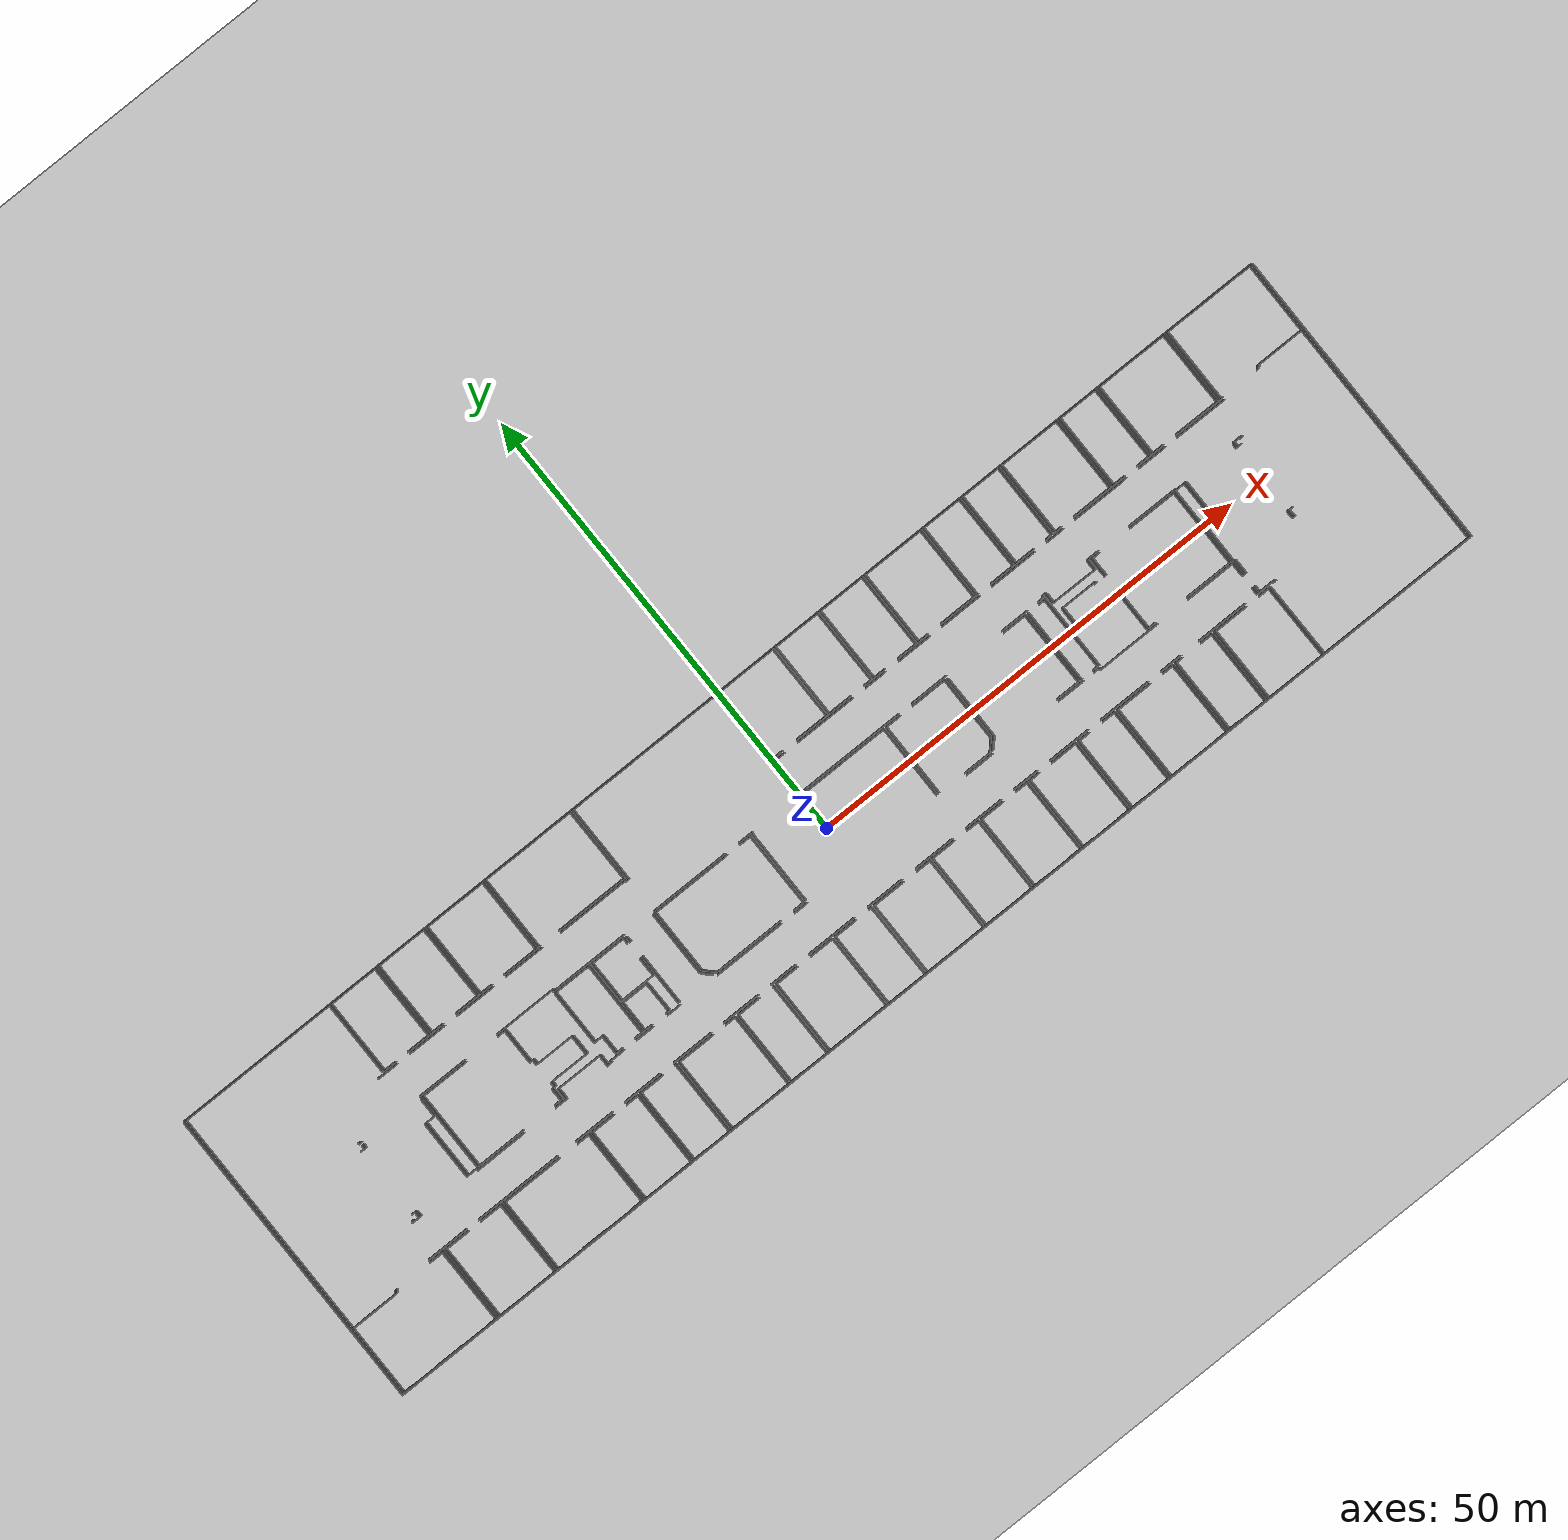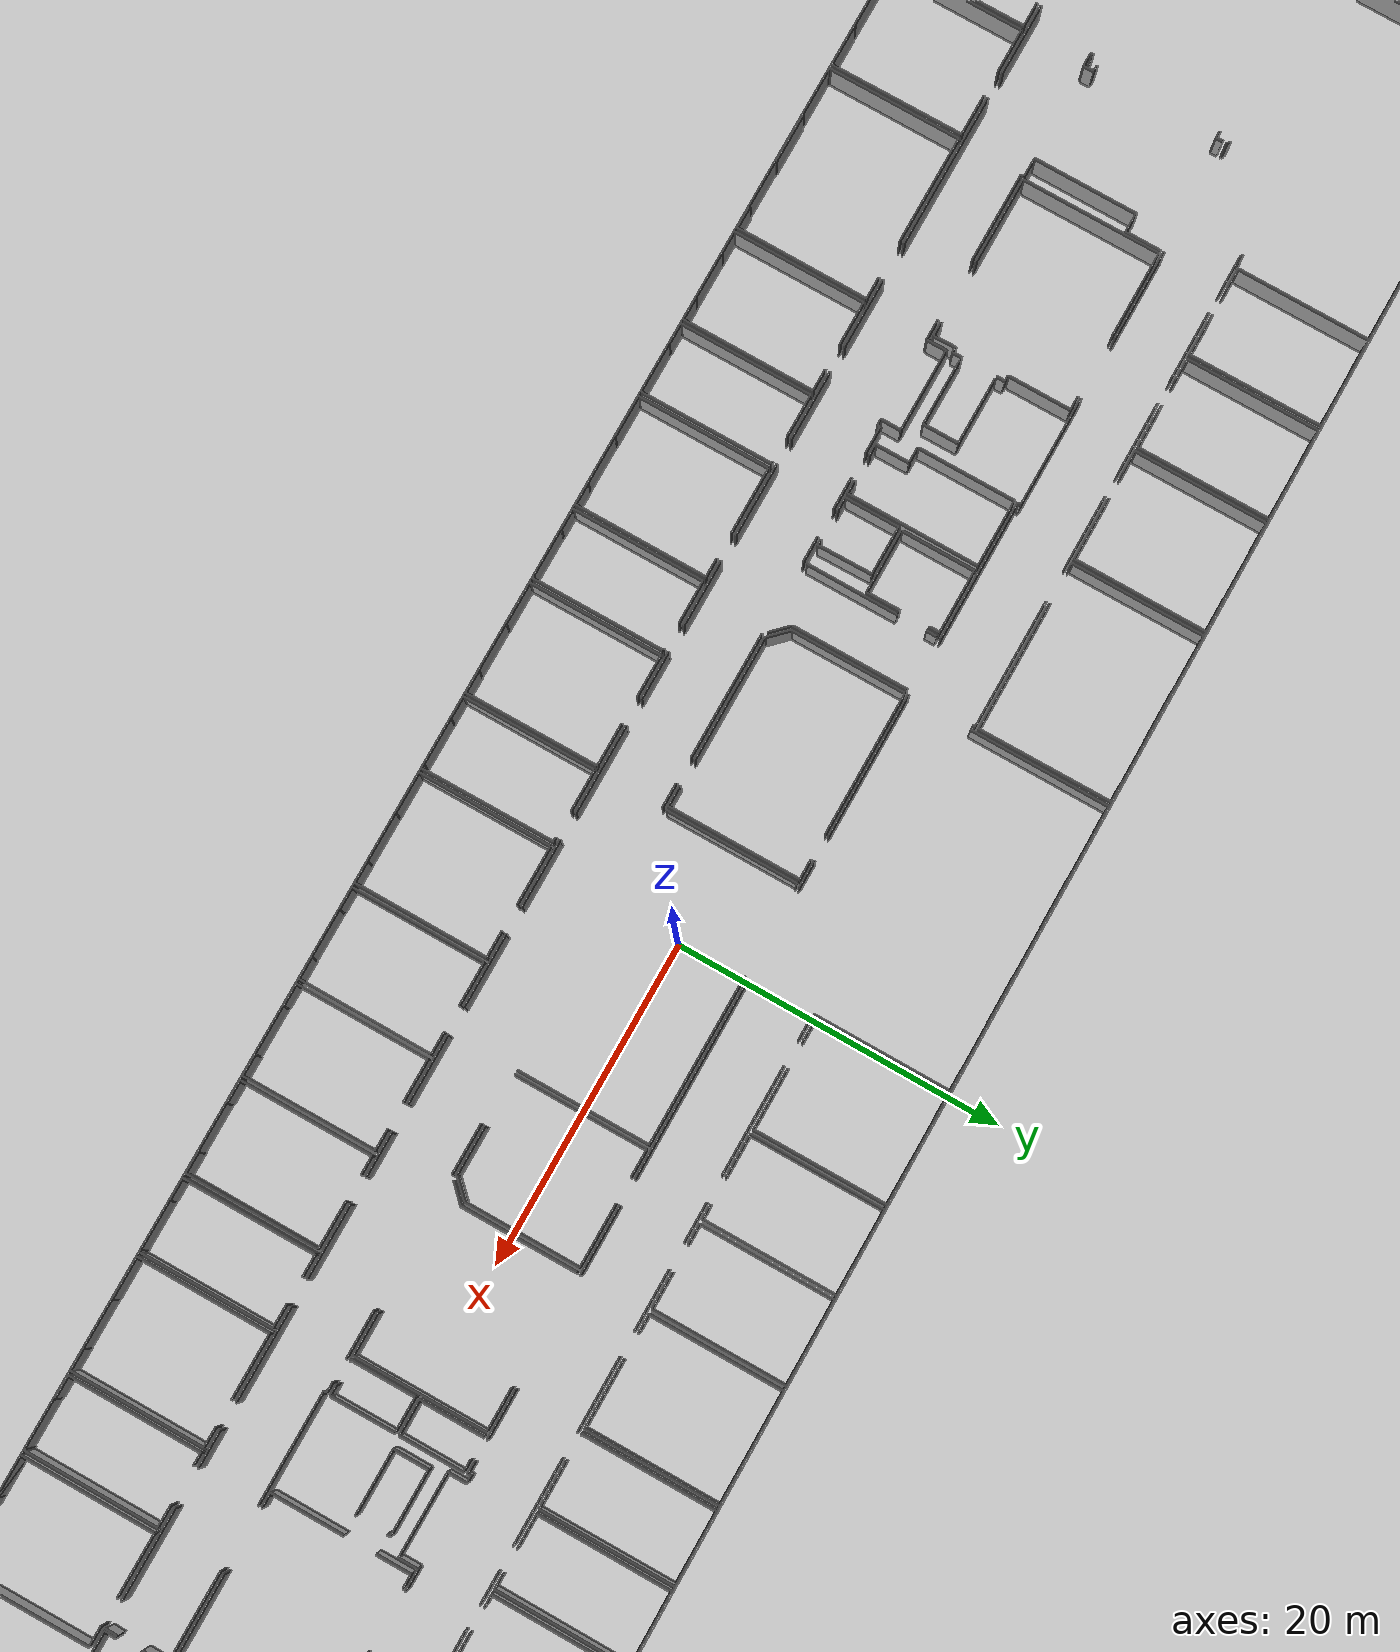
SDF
<sdf version="1.6">
  <world name="default">
    <light name="sun" type="directional">
      <cast_shadows>1</cast_shadows>
      <pose frame="">0 0 10 0 -0 0</pose>
      <diffuse>0.8 0.8 0.8 1</diffuse>
      <specular>0.1 0.1 0.1 1</specular>
      <attenuation>
        <range>1000</range>
        <constant>0.9</constant>
        <linear>0.01</linear>
        <quadratic>0.001</quadratic>
      </attenuation>
      <direction>-0.5 0.5 -1</direction>
    </light>
    <model name="ground_plane">
      <static>1</static>
      <link name="link">
        <collision name="collision">
          <geometry>
            <plane>
              <normal>0 0 1</normal>
              <size>100 100</size>
            </plane>
          </geometry>
          <surface>
            <friction>
              <ode>
                <mu>100</mu>
                <mu2>50</mu2>
              </ode>
              <torsional>
                <ode />
              </torsional>
            </friction>
            <contact>
              <ode />
            </contact>
            <bounce />
          </surface>
          <max_contacts>10</max_contacts>
        </collision>
        <visual name="visual">
          <cast_shadows>0</cast_shadows>
          <geometry>
            <plane>
              <normal>0 0 1</normal>
              <size>100 100</size>
            </plane>
          </geometry>
          <material>
            <script>
              <uri>file://media/materials/scripts/gazebo.material</uri>
              <name>Gazebo/Grey</name>
            </script>
          </material>
        </visual>
        <self_collide>0</self_collide>
        <kinematic>0</kinematic>
        <gravity>1</gravity>
      </link>
    </model>
    <gravity>0 0 -9.8</gravity>
    <magnetic_field>6e-06 2.3e-05 -4.2e-05</magnetic_field>
    <atmosphere type="adiabatic" />
    <physics default="0" name="default_physics" type="ode">
      <max_step_size>0.001</max_step_size>
      <real_time_factor>1</real_time_factor>
      <real_time_update_rate>1000</real_time_update_rate>
    </physics>
    <scene>
      <ambient>0.4 0.4 0.4 1</ambient>
      <background>0.7 0.7 0.7 1</background>
      <shadows>1</shadows>
    </scene>
    <spherical_coordinates>
      <surface_model>EARTH_WGS84</surface_model>
      <latitude_deg>0</latitude_deg>
      <longitude_deg>0</longitude_deg>
      <elevation>0</elevation>
      <heading_deg>0</heading_deg>
    </spherical_coordinates>
  <model name="50041173">
		<static>1</static>
		<link name="Wall_0">
			<collision name="Wall_0_Collision">
				<geometry>
					<box>
						<size>2.59577547031 0.1 2.5</size>
					</box>
				</geometry>
				<pose frame="">1.29788773515 0 1.25 0 0 0</pose>
			</collision>
			<visual name="Wall_0_Visual">
				<pose frame="">1.29788773515 0 1.25 0 0 0</pose>
				<geometry>
					<box>
						<size>2.59577547031 0.1 2.5</size>
					</box>
				</geometry>
				<material>
					<script>
						<uri>file://media/materials/scripts/gazebo.material</uri>
						<name>Gazebo/Grey</name>
					</script>
					<ambient>1 1 1 1</ambient>
				</material>
			</visual>
			<pose frame="">23.5269999238 -8.23085125289 0 0 0 3.14159265359</pose>
		</link>
		<link name="Wall_1">
			<collision name="Wall_1_Collision">
				<geometry>
					<box>
						<size>1.36891010181 0.1 2.5</size>
					</box>
				</geometry>
				<pose frame="">0.684455050903 0 1.25 0 0 0</pose>
			</collision>
			<visual name="Wall_1_Visual">
				<pose frame="">0.684455050903 0 1.25 0 0 0</pose>
				<geometry>
					<box>
						<size>1.36891010181 0.1 2.5</size>
					</box>
				</geometry>
				<material>
					<script>
						<uri>file://media/materials/scripts/gazebo.material</uri>
						<name>Gazebo/Grey</name>
					</script>
					<ambient>1 1 1 1</ambient>
				</material>
			</visual>
			<pose frame="">19.2869836756 -8.23085125289 0 0 0 3.14159265359</pose>
		</link>
		<link name="Wall_2">
			<collision name="Wall_2_Collision">
				<geometry>
					<box>
						<size>8.21726878062 0.1 2.5</size>
					</box>
				</geometry>
				<pose frame="">4.10863439031 0 1.25 0 0 0</pose>
			</collision>
			<visual name="Wall_2_Visual">
				<pose frame="">4.10863439031 0 1.25 0 0 0</pose>
				<geometry>
					<box>
						<size>8.21726878062 0.1 2.5</size>
					</box>
				</geometry>
				<material>
					<script>
						<uri>file://media/materials/scripts/gazebo.material</uri>
						<name>Gazebo/Grey</name>
					</script>
					<ambient>1 1 1 1</ambient>
				</material>
			</visual>
			<pose frame="">17.9180735738 -8.23085125289 0 0 0 1.57079632679</pose>
		</link>
		<link name="Wall_3">
			<collision name="Wall_3_Collision">
				<geometry>
					<box>
						<size>1.23257762319 0.1 2.5</size>
					</box>
				</geometry>
				<pose frame="">0.616288811597 0 1.25 0 0 0</pose>
			</collision>
			<visual name="Wall_3_Visual">
				<pose frame="">0.616288811597 0 1.25 0 0 0</pose>
				<geometry>
					<box>
						<size>1.23257762319 0.1 2.5</size>
					</box>
				</geometry>
				<material>
					<script>
						<uri>file://media/materials/scripts/gazebo.material</uri>
						<name>Gazebo/Grey</name>
					</script>
					<ambient>1 1 1 1</ambient>
				</material>
			</visual>
			<pose frame="">17.9180735738 -0.0135824722638 0 0 0 0.0</pose>
		</link>
		<link name="Wall_4">
			<collision name="Wall_4_Collision">
				<geometry>
					<box>
						<size>1.38871258473 0.1 2.5</size>
					</box>
				</geometry>
				<pose frame="">0.694356292366 0 1.25 0 0 0</pose>
			</collision>
			<visual name="Wall_4_Visual">
				<pose frame="">0.694356292366 0 1.25 0 0 0</pose>
				<geometry>
					<box>
						<size>1.38871258473 0.1 2.5</size>
					</box>
				</geometry>
				<material>
					<script>
						<uri>file://media/materials/scripts/gazebo.material</uri>
						<name>Gazebo/Grey</name>
					</script>
					<ambient>1 1 1 1</ambient>
				</material>
			</visual>
			<pose frame="">22.1174693442 -0.0135824722638 0 0 0 0.0</pose>
		</link>
		<link name="Wall_5">
			<collision name="Wall_5_Collision">
				<geometry>
					<box>
						<size>8.2172951512 0.1 2.5</size>
					</box>
				</geometry>
				<pose frame="">4.1086475756 0 1.25 0 0 0</pose>
			</collision>
			<visual name="Wall_5_Visual">
				<pose frame="">4.1086475756 0 1.25 0 0 0</pose>
				<geometry>
					<box>
						<size>8.2172951512 0.1 2.5</size>
					</box>
				</geometry>
				<material>
					<script>
						<uri>file://media/materials/scripts/gazebo.material</uri>
						<name>Gazebo/Grey</name>
					</script>
					<ambient>1 1 1 1</ambient>
				</material>
			</visual>
			<pose frame="">23.506181929 -0.0135824722638 0 0 0 -1.56826288766</pose>
		</link>
		<link name="Wall_6">
			<collision name="Wall_6_Collision">
				<geometry>
					<box>
						<size>2.70963974714 0.1 2.5</size>
					</box>
				</geometry>
				<pose frame="">1.35481987357 0 1.25 0 0 0</pose>
			</collision>
			<visual name="Wall_6_Visual">
				<pose frame="">1.35481987357 0 1.25 0 0 0</pose>
				<geometry>
					<box>
						<size>2.70963974714 0.1 2.5</size>
					</box>
				</geometry>
				<material>
					<script>
						<uri>file://media/materials/scripts/gazebo.material</uri>
						<name>Gazebo/Grey</name>
					</script>
					<ambient>1 1 1 1</ambient>
				</material>
			</visual>
			<pose frame="">29.5275330676 -8.22780471705 0 0 0 3.14159265359</pose>
		</link>
		<link name="Wall_7">
			<collision name="Wall_7_Collision">
				<geometry>
					<box>
						<size>1.36865622382 0.1 2.5</size>
					</box>
				</geometry>
				<pose frame="">0.684328111909 0 1.25 0 0 0</pose>
			</collision>
			<visual name="Wall_7_Visual">
				<pose frame="">0.684328111909 0 1.25 0 0 0</pose>
				<geometry>
					<box>
						<size>1.36865622382 0.1 2.5</size>
					</box>
				</geometry>
				<material>
					<script>
						<uri>file://media/materials/scripts/gazebo.material</uri>
						<name>Gazebo/Grey</name>
					</script>
					<ambient>1 1 1 1</ambient>
				</material>
			</visual>
			<pose frame="">25.1530884257 -8.22780471705 0 0 0 3.14159265359</pose>
		</link>
		<link name="Wall_8">
			<collision name="Wall_8_Collision">
				<geometry>
					<box>
						<size>8.21815735358 0.1 2.5</size>
					</box>
				</geometry>
				<pose frame="">4.10907867679 0 1.25 0 0 0</pose>
			</collision>
			<visual name="Wall_8_Visual">
				<pose frame="">4.10907867679 0 1.25 0 0 0</pose>
				<geometry>
					<box>
						<size>8.21815735358 0.1 2.5</size>
					</box>
				</geometry>
				<material>
					<script>
						<uri>file://media/materials/scripts/gazebo.material</uri>
						<name>Gazebo/Grey</name>
					</script>
					<ambient>1 1 1 1</ambient>
				</material>
			</visual>
			<pose frame="">23.7844322019 -8.22780471705 0 0 0 1.57079632679</pose>
		</link>
		<link name="Wall_9">
			<collision name="Wall_9_Collision">
				<geometry>
					<box>
						<size>1.35380436162 0.1 2.5</size>
					</box>
				</geometry>
				<pose frame="">0.676902180812 0 1.25 0 0 0</pose>
			</collision>
			<visual name="Wall_9_Visual">
				<pose frame="">0.676902180812 0 1.25 0 0 0</pose>
				<geometry>
					<box>
						<size>1.35380436162 0.1 2.5</size>
					</box>
				</geometry>
				<material>
					<script>
						<uri>file://media/materials/scripts/gazebo.material</uri>
						<name>Gazebo/Grey</name>
					</script>
					<ambient>1 1 1 1</ambient>
				</material>
			</visual>
			<pose frame="">23.7844322019 -0.00964736347711 0 0 0 0.0</pose>
		</link>
		<link name="Wall_10">
			<collision name="Wall_10_Collision">
				<geometry>
					<box>
						<size>1.37906522125 0.1 2.5</size>
					</box>
				</geometry>
				<pose frame="">0.689532610627 0 1.25 0 0 0</pose>
			</collision>
			<visual name="Wall_10_Visual">
				<pose frame="">0.689532610627 0 1.25 0 0 0</pose>
				<geometry>
					<box>
						<size>1.37906522125 0.1 2.5</size>
					</box>
				</geometry>
				<material>
					<script>
						<uri>file://media/materials/scripts/gazebo.material</uri>
						<name>Gazebo/Grey</name>
					</script>
					<ambient>1 1 1 1</ambient>
				</material>
			</visual>
			<pose frame="">28.1268882175 -0.00964736347711 0 0 0 0.0</pose>
		</link>
		<link name="Wall_11">
			<collision name="Wall_11_Collision">
				<geometry>
					<box>
						<size>8.21818568594 0.1 2.5</size>
					</box>
				</geometry>
				<pose frame="">4.10909284297 0 1.25 0 0 0</pose>
			</collision>
			<visual name="Wall_11_Visual">
				<pose frame="">4.10909284297 0 1.25 0 0 0</pose>
				<geometry>
					<box>
						<size>8.21818568594 0.1 2.5</size>
					</box>
				</geometry>
				<material>
					<script>
						<uri>file://media/materials/scripts/gazebo.material</uri>
						<name>Gazebo/Grey</name>
					</script>
					<ambient>1 1 1 1</ambient>
				</material>
			</visual>
			<pose frame="">29.5059534388 -0.00964736347711 0 0 0 -1.56817048522</pose>
		</link>
		<link name="Wall_12">
			<collision name="Wall_12_Collision">
				<geometry>
					<box>
						<size>3.90464342837 0.1 2.5</size>
					</box>
				</geometry>
				<pose frame="">1.95232171418 0 1.25 0 0 0</pose>
			</collision>
			<visual name="Wall_12_Visual">
				<pose frame="">1.95232171418 0 1.25 0 0 0</pose>
				<geometry>
					<box>
						<size>3.90464342837 0.1 2.5</size>
					</box>
				</geometry>
				<material>
					<script>
						<uri>file://media/materials/scripts/gazebo.material</uri>
						<name>Gazebo/Grey</name>
					</script>
					<ambient>1 1 1 1</ambient>
				</material>
			</visual>
			<pose frame="">36.7211658077 -8.24595699307 0 0 0 3.14159265359</pose>
		</link>
		<link name="Wall_13">
			<collision name="Wall_13_Collision">
				<geometry>
					<box>
						<size>1.40800731169 0.1 2.5</size>
					</box>
				</geometry>
				<pose frame="">0.704003655843 0 1.25 0 0 0</pose>
			</collision>
			<visual name="Wall_13_Visual">
				<pose frame="">0.704003655843 0 1.25 0 0 0</pose>
				<geometry>
					<box>
						<size>1.40800731169 0.1 2.5</size>
					</box>
				</geometry>
				<material>
					<script>
						<uri>file://media/materials/scripts/gazebo.material</uri>
						<name>Gazebo/Grey</name>
					</script>
					<ambient>1 1 1 1</ambient>
				</material>
			</visual>
			<pose frame="">31.1679656757 -8.24595699307 0 0 0 3.14159265359</pose>
		</link>
		<link name="Wall_14">
			<collision name="Wall_14_Collision">
				<geometry>
					<box>
						<size>8.22602757115 0.1 2.5</size>
					</box>
				</geometry>
				<pose frame="">4.11301378557 0 1.25 0 0 0</pose>
			</collision>
			<visual name="Wall_14_Visual">
				<pose frame="">4.11301378557 0 1.25 0 0 0</pose>
				<geometry>
					<box>
						<size>8.22602757115 0.1 2.5</size>
					</box>
				</geometry>
				<material>
					<script>
						<uri>file://media/materials/scripts/gazebo.material</uri>
						<name>Gazebo/Grey</name>
					</script>
					<ambient>1 1 1 1</ambient>
				</material>
			</visual>
			<pose frame="">29.759958364 -8.24595699307 0 0 0 1.57079632679</pose>
		</link>
		<link name="Wall_15">
			<collision name="Wall_15_Collision">
				<geometry>
					<box>
						<size>1.37551092945 0.1 2.5</size>
					</box>
				</geometry>
				<pose frame="">0.687755464724 0 1.25 0 0 0</pose>
			</collision>
			<visual name="Wall_15_Visual">
				<pose frame="">0.687755464724 0 1.25 0 0 0</pose>
				<geometry>
					<box>
						<size>1.37551092945 0.1 2.5</size>
					</box>
				</geometry>
				<material>
					<script>
						<uri>file://media/materials/scripts/gazebo.material</uri>
						<name>Gazebo/Grey</name>
					</script>
					<ambient>1 1 1 1</ambient>
				</material>
			</visual>
			<pose frame="">29.759958364 -0.0199294219198 0 0 0 0.0</pose>
		</link>
		<link name="Wall_16">
			<collision name="Wall_16_Collision">
				<geometry>
					<box>
						<size>2.60656528472 0.1 2.5</size>
					</box>
				</geometry>
				<pose frame="">1.30328264236 0 1.25 0 0 0</pose>
			</collision>
			<visual name="Wall_16_Visual">
				<pose frame="">1.30328264236 0 1.25 0 0 0</pose>
				<geometry>
					<box>
						<size>2.60656528472 0.1 2.5</size>
					</box>
				</geometry>
				<material>
					<script>
						<uri>file://media/materials/scripts/gazebo.material</uri>
						<name>Gazebo/Grey</name>
					</script>
					<ambient>1 1 1 1</ambient>
				</material>
			</visual>
			<pose frame="">34.1205666557 -0.0199294219198 0 0 0 0.0</pose>
		</link>
		<link name="Wall_17">
			<collision name="Wall_17_Collision">
				<geometry>
					<box>
						<size>8.22602973469 0.1 2.5</size>
					</box>
				</geometry>
				<pose frame="">4.11301486735 0 1.25 0 0 0</pose>
			</collision>
			<visual name="Wall_17_Visual">
				<pose frame="">4.11301486735 0 1.25 0 0 0</pose>
				<geometry>
					<box>
						<size>8.22602973469 0.1 2.5</size>
					</box>
				</geometry>
				<material>
					<script>
						<uri>file://media/materials/scripts/gazebo.material</uri>
						<name>Gazebo/Grey</name>
					</script>
					<ambient>1 1 1 1</ambient>
				</material>
			</visual>
			<pose frame="">36.7271319404 -0.0199294219198 0 0 0 -1.57152160173</pose>
		</link>
		<link name="Wall_18">
			<collision name="Wall_18_Collision">
				<geometry>
					<box>
						<size>7.98801695905 0.1 2.5</size>
					</box>
				</geometry>
				<pose frame="">3.99400847952 0 1.25 0 0 0</pose>
			</collision>
			<visual name="Wall_18_Visual">
				<pose frame="">3.99400847952 0 1.25 0 0 0</pose>
				<geometry>
					<box>
						<size>7.98801695905 0.1 2.5</size>
					</box>
				</geometry>
				<material>
					<script>
						<uri>file://media/materials/scripts/gazebo.material</uri>
						<name>Gazebo/Grey</name>
					</script>
					<ambient>1 1 1 1</ambient>
				</material>
			</visual>
			<pose frame="">47.5401761913 -8.24049861636 0 0 0 3.14159265359</pose>
		</link>
		<link name="Wall_19">
			<collision name="Wall_19_Collision">
				<geometry>
					<box>
						<size>0.179872553251 0.1 2.5</size>
					</box>
				</geometry>
				<pose frame="">0.0899362766255 0 1.25 0 0 0</pose>
			</collision>
			<visual name="Wall_19_Visual">
				<pose frame="">0.0899362766255 0 1.25 0 0 0</pose>
				<geometry>
					<box>
						<size>0.179872553251 0.1 2.5</size>
					</box>
				</geometry>
				<material>
					<script>
						<uri>file://media/materials/scripts/gazebo.material</uri>
						<name>Gazebo/Grey</name>
					</script>
					<ambient>1 1 1 1</ambient>
				</material>
			</visual>
			<pose frame="">37.1438726548 -8.24049861636 0 0 0 3.14159265359</pose>
		</link>
		<link name="Wall_20">
			<collision name="Wall_20_Collision">
				<geometry>
					<box>
						<size>8.21612632969 0.1 2.5</size>
					</box>
				</geometry>
				<pose frame="">4.10806316484 0 1.25 0 0 0</pose>
			</collision>
			<visual name="Wall_20_Visual">
				<pose frame="">4.10806316484 0 1.25 0 0 0</pose>
				<geometry>
					<box>
						<size>8.21612632969 0.1 2.5</size>
					</box>
				</geometry>
				<material>
					<script>
						<uri>file://media/materials/scripts/gazebo.material</uri>
						<name>Gazebo/Grey</name>
					</script>
					<ambient>1 1 1 1</ambient>
				</material>
			</visual>
			<pose frame="">36.9640001016 -8.24049861636 0 0 0 1.57079632679</pose>
		</link>
		<link name="Wall_21">
			<collision name="Wall_21_Collision">
				<geometry>
					<box>
						<size>0.181522760161 0.1 2.5</size>
					</box>
				</geometry>
				<pose frame="">0.0907613800807 0 1.25 0 0 0</pose>
			</collision>
			<visual name="Wall_21_Visual">
				<pose frame="">0.0907613800807 0 1.25 0 0 0</pose>
				<geometry>
					<box>
						<size>0.181522760161 0.1 2.5</size>
					</box>
				</geometry>
				<material>
					<script>
						<uri>file://media/materials/scripts/gazebo.material</uri>
						<name>Gazebo/Grey</name>
					</script>
					<ambient>1 1 1 1</ambient>
				</material>
			</visual>
			<pose frame="">36.9640001016 -0.024372286679 0 0 0 0.0</pose>
		</link>
		<link name="Wall_22">
			<collision name="Wall_22_Collision">
				<geometry>
					<box>
						<size>3.04869379776 0.1 2.5</size>
					</box>
				</geometry>
				<pose frame="">1.52434689888 0 1.25 0 0 0</pose>
			</collision>
			<visual name="Wall_22_Visual">
				<pose frame="">1.52434689888 0 1.25 0 0 0</pose>
				<geometry>
					<box>
						<size>3.04869379776 0.1 2.5</size>
					</box>
				</geometry>
				<material>
					<script>
						<uri>file://media/materials/scripts/gazebo.material</uri>
						<name>Gazebo/Grey</name>
					</script>
					<ambient>1 1 1 1</ambient>
				</material>
			</visual>
			<pose frame="">40.1090405951 -0.024372286679 0 0 0 0.0</pose>
		</link>
		<link name="Wall_23">
			<collision name="Wall_23_Collision">
				<geometry>
					<box>
						<size>1.37170275965 0.1 2.5</size>
					</box>
				</geometry>
				<pose frame="">0.685851379827 0 1.25 0 0 0</pose>
			</collision>
			<visual name="Wall_23_Visual">
				<pose frame="">0.685851379827 0 1.25 0 0 0</pose>
				<geometry>
					<box>
						<size>1.37170275965 0.1 2.5</size>
					</box>
				</geometry>
				<material>
					<script>
						<uri>file://media/materials/scripts/gazebo.material</uri>
						<name>Gazebo/Grey</name>
					</script>
					<ambient>1 1 1 1</ambient>
				</material>
			</visual>
			<pose frame="">46.1334382696 -0.024372286679 0 0 0 0.0</pose>
		</link>
		<link name="Wall_24">
			<collision name="Wall_24_Collision">
				<geometry>
					<box>
						<size>8.21620102772 0.1 2.5</size>
					</box>
				</geometry>
				<pose frame="">4.10810051386 0 1.25 0 0 0</pose>
			</collision>
			<visual name="Wall_24_Visual">
				<pose frame="">4.10810051386 0 1.25 0 0 0</pose>
				<geometry>
					<box>
						<size>8.21620102772 0.1 2.5</size>
					</box>
				</geometry>
				<material>
					<script>
						<uri>file://media/materials/scripts/gazebo.material</uri>
						<name>Gazebo/Grey</name>
					</script>
					<ambient>1 1 1 1</ambient>
				</material>
			</visual>
			<pose frame="">47.5051410292 -0.024372286679 0 0 0 -1.56653215797</pose>
		</link>
		<link name="Wall_25">
			<collision name="Wall_25_Collision">
				<geometry>
					<box>
						<size>0.166924775953 0.1 2.5</size>
					</box>
				</geometry>
				<pose frame="">0.0834623879763 0 1.25 0 0 0</pose>
			</collision>
			<visual name="Wall_25_Visual">
				<pose frame="">0.0834623879763 0 1.25 0 0 0</pose>
				<geometry>
					<box>
						<size>0.166924775953 0.1 2.5</size>
					</box>
				</geometry>
				<material>
					<script>
						<uri>file://media/materials/scripts/gazebo.material</uri>
						<name>Gazebo/Grey</name>
					</script>
					<ambient>1 1 1 1</ambient>
				</material>
			</visual>
			<pose frame="">47.5312904618 -8.63984868872 0 0 0 1.57079632679</pose>
		</link>
		<link name="Wall_26">
			<collision name="Wall_26_Collision">
				<geometry>
					<box>
						<size>7.97684632765 0.1 2.5</size>
					</box>
				</geometry>
				<pose frame="">3.98842316383 0 1.25 0 0 0</pose>
			</collision>
			<visual name="Wall_26_Visual">
				<pose frame="">3.98842316383 0 1.25 0 0 0</pose>
				<geometry>
					<box>
						<size>7.97684632765 0.1 2.5</size>
					</box>
				</geometry>
				<material>
					<script>
						<uri>file://media/materials/scripts/gazebo.material</uri>
						<name>Gazebo/Grey</name>
					</script>
					<ambient>1 1 1 1</ambient>
				</material>
			</visual>
			<pose frame="">47.5312904618 -8.47292391277 0 0 0 3.14159265359</pose>
		</link>
		<link name="Wall_27">
			<collision name="Wall_27_Collision">
				<geometry>
					<box>
						<size>4.34918378227 0.1 2.5</size>
					</box>
				</geometry>
				<pose frame="">2.17459189114 0 1.25 0 0 0</pose>
			</collision>
			<visual name="Wall_27_Visual">
				<pose frame="">2.17459189114 0 1.25 0 0 0</pose>
				<geometry>
					<box>
						<size>4.34918378227 0.1 2.5</size>
					</box>
				</geometry>
				<material>
					<script>
						<uri>file://media/materials/scripts/gazebo.material</uri>
						<name>Gazebo/Grey</name>
					</script>
					<ambient>1 1 1 1</ambient>
				</material>
			</visual>
			<pose frame="">37.1565665541 -8.47292391277 0 0 0 3.14159265359</pose>
		</link>
		<link name="Wall_28">
			<collision name="Wall_28_Collision">
				<geometry>
					<box>
						<size>4.37304831298 0.1 2.5</size>
					</box>
				</geometry>
				<pose frame="">2.18652415649 0 1.25 0 0 0</pose>
			</collision>
			<visual name="Wall_28_Visual">
				<pose frame="">2.18652415649 0 1.25 0 0 0</pose>
				<geometry>
					<box>
						<size>4.37304831298 0.1 2.5</size>
					</box>
				</geometry>
				<material>
					<script>
						<uri>file://media/materials/scripts/gazebo.material</uri>
						<name>Gazebo/Grey</name>
					</script>
					<ambient>1 1 1 1</ambient>
				</material>
			</visual>
			<pose frame="">31.1909416335 -8.47292391277 0 0 0 3.14159265359</pose>
		</link>
		<link name="Wall_29">
			<collision name="Wall_29_Collision">
				<geometry>
					<box>
						<size>4.21348599863 0.1 2.5</size>
					</box>
				</geometry>
				<pose frame="">2.10674299931 0 1.25 0 0 0</pose>
			</collision>
			<visual name="Wall_29_Visual">
				<pose frame="">2.10674299931 0 1.25 0 0 0</pose>
				<geometry>
					<box>
						<size>4.21348599863 0.1 2.5</size>
					</box>
				</geometry>
				<material>
					<script>
						<uri>file://media/materials/scripts/gazebo.material</uri>
						<name>Gazebo/Grey</name>
					</script>
					<ambient>1 1 1 1</ambient>
				</material>
			</visual>
			<pose frame="">25.1530884257 -8.47292391277 0 0 0 3.14159265359</pose>
		</link>
		<link name="Wall_30">
			<collision name="Wall_30_Collision">
				<geometry>
					<box>
						<size>2.12686282972 0.1 2.5</size>
					</box>
				</geometry>
				<pose frame="">1.06343141486 0 1.25 0 0 0</pose>
			</collision>
			<visual name="Wall_30_Visual">
				<pose frame="">1.06343141486 0 1.25 0 0 0</pose>
				<geometry>
					<box>
						<size>2.12686282972 0.1 2.5</size>
					</box>
				</geometry>
				<material>
					<script>
						<uri>file://media/materials/scripts/gazebo.material</uri>
						<name>Gazebo/Grey</name>
					</script>
					<ambient>1 1 1 1</ambient>
				</material>
			</visual>
			<pose frame="">19.2831755059 -8.47292391277 0 0 0 3.14159265359</pose>
		</link>
		<link name="Wall_31">
			<collision name="Wall_31_Collision">
				<geometry>
					<box>
						<size>0.134936149686 0.1 2.5</size>
					</box>
				</geometry>
				<pose frame="">0.0674680748432 0 1.25 0 0 0</pose>
			</collision>
			<visual name="Wall_31_Visual">
				<pose frame="">0.0674680748432 0 1.25 0 0 0</pose>
				<geometry>
					<box>
						<size>0.134936149686 0.1 2.5</size>
					</box>
				</geometry>
				<material>
					<script>
						<uri>file://media/materials/scripts/gazebo.material</uri>
						<name>Gazebo/Grey</name>
					</script>
					<ambient>1 1 1 1</ambient>
				</material>
			</visual>
			<pose frame="">17.1563126761 -8.47292391277 0 0 0 1.57079632679</pose>
		</link>
		<link name="Wall_32">
			<collision name="Wall_32_Collision">
				<geometry>
					<box>
						<size>0.178531514577 0.1 2.5</size>
					</box>
				</geometry>
				<pose frame="">0.0892657572885 0 1.25 0 0 0</pose>
			</collision>
			<visual name="Wall_32_Visual">
				<pose frame="">0.0892657572885 0 1.25 0 0 0</pose>
				<geometry>
					<box>
						<size>0.178531514577 0.1 2.5</size>
					</box>
				</geometry>
				<material>
					<script>
						<uri>file://media/materials/scripts/gazebo.material</uri>
						<name>Gazebo/Grey</name>
					</script>
					<ambient>1 1 1 1</ambient>
				</material>
			</visual>
			<pose frame="">11.7602630176 -12.0741831476 0 0 0 -0.784895398231</pose>
		</link>
		<link name="Wall_33">
			<collision name="Wall_33_Collision">
				<geometry>
					<box>
						<size>0.0767980908375 0.1 2.5</size>
					</box>
				</geometry>
				<pose frame="">0.0383990454188 0 1.25 0 0 0</pose>
			</collision>
			<visual name="Wall_33_Visual">
				<pose frame="">0.0383990454188 0 1.25 0 0 0</pose>
				<geometry>
					<box>
						<size>0.0767980908375 0.1 2.5</size>
					</box>
				</geometry>
				<material>
					<script>
						<uri>file://media/materials/scripts/gazebo.material</uri>
						<name>Gazebo/Grey</name>
					</script>
					<ambient>1 1 1 1</ambient>
				</material>
			</visual>
			<pose frame="">11.8865673157 -12.2003605067 0 0 0 -1.57079632679</pose>
		</link>
		<link name="Wall_34">
			<collision name="Wall_34_Collision">
				<geometry>
					<box>
						<size>5.57642996776 0.1 2.5</size>
					</box>
				</geometry>
				<pose frame="">2.78821498388 0 1.25 0 0 0</pose>
			</collision>
			<visual name="Wall_34_Visual">
				<pose frame="">2.78821498388 0 1.25 0 0 0</pose>
				<geometry>
					<box>
						<size>5.57642996776 0.1 2.5</size>
					</box>
				</geometry>
				<material>
					<script>
						<uri>file://media/materials/scripts/gazebo.material</uri>
						<name>Gazebo/Grey</name>
					</script>
					<ambient>1 1 1 1</ambient>
				</material>
			</visual>
			<pose frame="">19.1190433877 -12.2771585976 0 0 0 0.0</pose>
		</link>
		<link name="Wall_35">
			<collision name="Wall_35_Collision">
				<geometry>
					<box>
						<size>6.83414151159 0.1 2.5</size>
					</box>
				</geometry>
				<pose frame="">3.41707075579 0 1.25 0 0 0</pose>
			</collision>
			<visual name="Wall_35_Visual">
				<pose frame="">3.41707075579 0 1.25 0 0 0</pose>
				<geometry>
					<box>
						<size>6.83414151159 0.1 2.5</size>
					</box>
				</geometry>
				<material>
					<script>
						<uri>file://media/materials/scripts/gazebo.material</uri>
						<name>Gazebo/Grey</name>
					</script>
					<ambient>1 1 1 1</ambient>
				</material>
			</visual>
			<pose frame="">28.6416258346 -12.2771585976 0 0 0 0.0</pose>
		</link>
		<link name="Wall_36">
			<collision name="Wall_36_Collision">
				<geometry>
					<box>
						<size>0.191170123639 0.1 2.5</size>
					</box>
				</geometry>
				<pose frame="">0.0955850618193 0 1.25 0 0 0</pose>
			</collision>
			<visual name="Wall_36_Visual">
				<pose frame="">0.0955850618193 0 1.25 0 0 0</pose>
				<geometry>
					<box>
						<size>0.191170123639 0.1 2.5</size>
					</box>
				</geometry>
				<material>
					<script>
						<uri>file://media/materials/scripts/gazebo.material</uri>
						<name>Gazebo/Grey</name>
					</script>
					<ambient>1 1 1 1</ambient>
				</material>
			</visual>
			<pose frame="">35.4757673462 -12.2771585976 0 0 0 -1.57079632679</pose>
		</link>
		<link name="Wall_37">
			<collision name="Wall_37_Collision">
				<geometry>
					<box>
						<size>8.68656223819 0.1 2.5</size>
					</box>
				</geometry>
				<pose frame="">4.34328111909 0 1.25 0 0 0</pose>
			</collision>
			<visual name="Wall_37_Visual">
				<pose frame="">4.34328111909 0 1.25 0 0 0</pose>
				<geometry>
					<box>
						<size>8.68656223819 0.1 2.5</size>
					</box>
				</geometry>
				<material>
					<script>
						<uri>file://media/materials/scripts/gazebo.material</uri>
						<name>Gazebo/Grey</name>
					</script>
					<ambient>1 1 1 1</ambient>
				</material>
			</visual>
			<pose frame="">35.4757673462 -12.4683287212 0 0 0 0.0</pose>
		</link>
		<link name="Wall_38">
			<collision name="Wall_38_Collision">
				<geometry>
					<box>
						<size>1.65096854452 0.1 2.5</size>
					</box>
				</geometry>
				<pose frame="">0.825484272259 0 1.25 0 0 0</pose>
			</collision>
			<visual name="Wall_38_Visual">
				<pose frame="">0.825484272259 0 1.25 0 0 0</pose>
				<geometry>
					<box>
						<size>1.65096854452 0.1 2.5</size>
					</box>
				</geometry>
				<material>
					<script>
						<uri>file://media/materials/scripts/gazebo.material</uri>
						<name>Gazebo/Grey</name>
					</script>
					<ambient>1 1 1 1</ambient>
				</material>
			</visual>
			<pose frame="">59.8844855163 -12.4957475437 0 0 0 3.14159265359</pose>
		</link>
		<link name="Wall_39">
			<collision name="Wall_39_Collision">
				<geometry>
					<box>
						<size>8.8579298789 0.1 2.5</size>
					</box>
				</geometry>
				<pose frame="">4.42896493945 0 1.25 0 0 0</pose>
			</collision>
			<visual name="Wall_39_Visual">
				<pose frame="">4.42896493945 0 1.25 0 0 0</pose>
				<geometry>
					<box>
						<size>8.8579298789 0.1 2.5</size>
					</box>
				</geometry>
				<material>
					<script>
						<uri>file://media/materials/scripts/gazebo.material</uri>
						<name>Gazebo/Grey</name>
					</script>
					<ambient>1 1 1 1</ambient>
				</material>
			</visual>
			<pose frame="">56.622915027 -12.4957475437 0 0 0 3.14159265359</pose>
		</link>
		<link name="Wall_40">
			<collision name="Wall_40_Collision">
				<geometry>
					<box>
						<size>8.60214780776 0.1 2.5</size>
					</box>
				</geometry>
				<pose frame="">4.30107390388 0 1.25 0 0 0</pose>
			</collision>
			<visual name="Wall_40_Visual">
				<pose frame="">4.30107390388 0 1.25 0 0 0</pose>
				<geometry>
					<box>
						<size>8.60214780776 0.1 2.5</size>
					</box>
				</geometry>
				<material>
					<script>
						<uri>file://media/materials/scripts/gazebo.material</uri>
						<name>Gazebo/Grey</name>
					</script>
					<ambient>1 1 1 1</ambient>
				</material>
			</visual>
			<pose frame="">47.7649851481 -8.62131559572 0 0 0 1.57079632679</pose>
		</link>
		<link name="Wall_41">
			<collision name="Wall_41_Collision">
				<geometry>
					<box>
						<size>1.36929091878 0.1 2.5</size>
					</box>
				</geometry>
				<pose frame="">0.684645459392 0 1.25 0 0 0</pose>
			</collision>
			<visual name="Wall_41_Visual">
				<pose frame="">0.684645459392 0 1.25 0 0 0</pose>
				<geometry>
					<box>
						<size>1.36929091878 0.1 2.5</size>
					</box>
				</geometry>
				<material>
					<script>
						<uri>file://media/materials/scripts/gazebo.material</uri>
						<name>Gazebo/Grey</name>
					</script>
					<ambient>1 1 1 1</ambient>
				</material>
			</visual>
			<pose frame="">47.7649851481 -0.0191677879611 0 0 0 0.0</pose>
		</link>
		<link name="Wall_42">
			<collision name="Wall_42_Collision">
				<geometry>
					<box>
						<size>3.062784026 0.1 2.5</size>
					</box>
				</geometry>
				<pose frame="">1.531392013 0 1.25 0 0 0</pose>
			</collision>
			<visual name="Wall_42_Visual">
				<pose frame="">1.531392013 0 1.25 0 0 0</pose>
				<geometry>
					<box>
						<size>3.062784026 0.1 2.5</size>
					</box>
				</geometry>
				<material>
					<script>
						<uri>file://media/materials/scripts/gazebo.material</uri>
						<name>Gazebo/Grey</name>
					</script>
					<ambient>1 1 1 1</ambient>
				</material>
			</visual>
			<pose frame="">52.0920815456 -0.0191677879611 0 0 0 0.0</pose>
		</link>
		<link name="Wall_43">
			<collision name="Wall_43_Collision">
				<geometry>
					<box>
						<size>3.01200842875 0.1 2.5</size>
					</box>
				</geometry>
				<pose frame="">1.50600421437 0 1.25 0 0 0</pose>
			</collision>
			<visual name="Wall_43_Visual">
				<pose frame="">1.50600421437 0 1.25 0 0 0</pose>
				<geometry>
					<box>
						<size>3.01200842875 0.1 2.5</size>
					</box>
				</geometry>
				<material>
					<script>
						<uri>file://media/materials/scripts/gazebo.material</uri>
						<name>Gazebo/Grey</name>
					</script>
					<ambient>1 1 1 1</ambient>
				</material>
			</visual>
			<pose frame="">58.1233339257 -0.0191677879611 0 0 0 0.0</pose>
		</link>
		<link name="Wall_44">
			<collision name="Wall_44_Collision">
				<geometry>
					<box>
						<size>1.38617380487 0.1 2.5</size>
					</box>
				</geometry>
				<pose frame="">0.693086902435 0 1.25 0 0 0</pose>
			</collision>
			<visual name="Wall_44_Visual">
				<pose frame="">0.693086902435 0 1.25 0 0 0</pose>
				<geometry>
					<box>
						<size>1.38617380487 0.1 2.5</size>
					</box>
				</geometry>
				<material>
					<script>
						<uri>file://media/materials/scripts/gazebo.material</uri>
						<name>Gazebo/Grey</name>
					</script>
					<ambient>1 1 1 1</ambient>
				</material>
			</visual>
			<pose frame="">64.1182817538 -0.0191677879611 0 0 0 0.0</pose>
		</link>
		<link name="Wall_45">
			<collision name="Wall_45_Collision">
				<geometry>
					<box>
						<size>8.43700017771 0.1 2.5</size>
					</box>
				</geometry>
				<pose frame="">4.21850008886 0 1.25 0 0 0</pose>
			</collision>
			<visual name="Wall_45_Visual">
				<pose frame="">4.21850008886 0 1.25 0 0 0</pose>
				<geometry>
					<box>
						<size>8.43700017771 0.1 2.5</size>
					</box>
				</geometry>
				<material>
					<script>
						<uri>file://media/materials/scripts/gazebo.material</uri>
						<name>Gazebo/Grey</name>
					</script>
					<ambient>1 1 1 1</ambient>
				</material>
			</visual>
			<pose frame="">65.5044555587 -0.0191677879611 0 0 0 -1.57079632679</pose>
		</link>
		<link name="Wall_46">
			<collision name="Wall_46_Collision">
				<geometry>
					<box>
						<size>0.864454543147 0.1 2.5</size>
					</box>
				</geometry>
				<pose frame="">0.432227271573 0 1.25 0 0 0</pose>
			</collision>
			<visual name="Wall_46_Visual">
				<pose frame="">0.432227271573 0 1.25 0 0 0</pose>
				<geometry>
					<box>
						<size>0.864454543147 0.1 2.5</size>
					</box>
				</geometry>
				<material>
					<script>
						<uri>file://media/materials/scripts/gazebo.material</uri>
						<name>Gazebo/Grey</name>
					</script>
					<ambient>1 1 1 1</ambient>
				</material>
			</visual>
			<pose frame="">120.225443652 -12.2639569423 0 0 0 3.14159265359</pose>
		</link>
		<link name="Wall_47">
			<collision name="Wall_47_Collision">
				<geometry>
					<box>
						<size>5.55688136282 0.1 2.5</size>
					</box>
				</geometry>
				<pose frame="">2.77844068141 0 1.25 0 0 0</pose>
			</collision>
			<visual name="Wall_47_Visual">
				<pose frame="">2.77844068141 0 1.25 0 0 0</pose>
				<geometry>
					<box>
						<size>5.55688136282 0.1 2.5</size>
					</box>
				</geometry>
				<material>
					<script>
						<uri>file://media/materials/scripts/gazebo.material</uri>
						<name>Gazebo/Grey</name>
					</script>
					<ambient>1 1 1 1</ambient>
				</material>
			</visual>
			<pose frame="">112.128005281 -12.2639569423 0 0 0 3.14159265359</pose>
		</link>
		<link name="Wall_48">
			<collision name="Wall_48_Collision">
				<geometry>
					<box>
						<size>1.29122343802 0.1 2.5</size>
					</box>
				</geometry>
				<pose frame="">0.645611719008 0 1.25 0 0 0</pose>
			</collision>
			<visual name="Wall_48_Visual">
				<pose frame="">0.645611719008 0 1.25 0 0 0</pose>
				<geometry>
					<box>
						<size>1.29122343802 0.1 2.5</size>
					</box>
				</geometry>
				<material>
					<script>
						<uri>file://media/materials/scripts/gazebo.material</uri>
						<name>Gazebo/Grey</name>
					</script>
					<ambient>1 1 1 1</ambient>
				</material>
			</visual>
			<pose frame="">102.657087004 -12.2639569423 0 0 0 3.14159265359</pose>
		</link>
		<link name="Wall_49">
			<collision name="Wall_49_Collision">
				<geometry>
					<box>
						<size>0.408997435832 0.1 2.5</size>
					</box>
				</geometry>
				<pose frame="">0.204498717916 0 1.25 0 0 0</pose>
			</collision>
			<visual name="Wall_49_Visual">
				<pose frame="">0.204498717916 0 1.25 0 0 0</pose>
				<geometry>
					<box>
						<size>0.408997435832 0.1 2.5</size>
					</box>
				</geometry>
				<material>
					<script>
						<uri>file://media/materials/scripts/gazebo.material</uri>
						<name>Gazebo/Grey</name>
					</script>
					<ambient>1 1 1 1</ambient>
				</material>
			</visual>
			<pose frame="">96.199446546 -12.2639569423 0 0 0 3.14159265359</pose>
		</link>
		<link name="Wall_50">
			<collision name="Wall_50_Collision">
				<geometry>
					<box>
						<size>0.19853258524 0.1 2.5</size>
					</box>
				</geometry>
				<pose frame="">0.0992662926198 0 1.25 0 0 0</pose>
			</collision>
			<visual name="Wall_50_Visual">
				<pose frame="">0.0992662926198 0 1.25 0 0 0</pose>
				<geometry>
					<box>
						<size>0.19853258524 0.1 2.5</size>
					</box>
				</geometry>
				<material>
					<script>
						<uri>file://media/materials/scripts/gazebo.material</uri>
						<name>Gazebo/Grey</name>
					</script>
					<ambient>1 1 1 1</ambient>
				</material>
			</visual>
			<pose frame="">95.7904491102 -12.2639569423 0 0 0 -1.57079632679</pose>
		</link>
		<link name="Wall_51">
			<collision name="Wall_51_Collision">
				<geometry>
					<box>
						<size>0.659321130265 0.1 2.5</size>
					</box>
				</geometry>
				<pose frame="">0.329660565132 0 1.25 0 0 0</pose>
			</collision>
			<visual name="Wall_51_Visual">
				<pose frame="">0.329660565132 0 1.25 0 0 0</pose>
				<geometry>
					<box>
						<size>0.659321130265 0.1 2.5</size>
					</box>
				</geometry>
				<material>
					<script>
						<uri>file://media/materials/scripts/gazebo.material</uri>
						<name>Gazebo/Grey</name>
					</script>
					<ambient>1 1 1 1</ambient>
				</material>
			</visual>
			<pose frame="">95.7904491102 -12.4624895275 0 0 0 3.14159265359</pose>
		</link>
		<link name="Wall_52">
			<collision name="Wall_52_Collision">
				<geometry>
					<box>
						<size>2.99474472568 0.1 2.5</size>
					</box>
				</geometry>
				<pose frame="">1.49737236284 0 1.25 0 0 0</pose>
			</collision>
			<visual name="Wall_52_Visual">
				<pose frame="">1.49737236284 0 1.25 0 0 0</pose>
				<geometry>
					<box>
						<size>2.99474472568 0.1 2.5</size>
					</box>
				</geometry>
				<material>
					<script>
						<uri>file://media/materials/scripts/gazebo.material</uri>
						<name>Gazebo/Grey</name>
					</script>
					<ambient>1 1 1 1</ambient>
				</material>
			</visual>
			<pose frame="">93.726040265 -12.4624895275 0 0 0 3.14159265359</pose>
		</link>
		<link name="Wall_53">
			<collision name="Wall_53_Collision">
				<geometry>
					<box>
						<size>4.23163827465 0.1 2.5</size>
					</box>
				</geometry>
				<pose frame="">2.11581913732 0 1.25 0 0 0</pose>
			</collision>
			<visual name="Wall_53_Visual">
				<pose frame="">2.11581913732 0 1.25 0 0 0</pose>
				<geometry>
					<box>
						<size>4.23163827465 0.1 2.5</size>
					</box>
				</geometry>
				<material>
					<script>
						<uri>file://media/materials/scripts/gazebo.material</uri>
						<name>Gazebo/Grey</name>
					</script>
					<ambient>1 1 1 1</ambient>
				</material>
			</visual>
			<pose frame="">83.7736423875 -12.4624895275 0 0 0 3.14159265359</pose>
		</link>
		<link name="Wall_54">
			<collision name="Wall_54_Collision">
				<geometry>
					<box>
						<size>12.1599939069 0.1 2.5</size>
					</box>
				</geometry>
				<pose frame="">6.07999695346 0 1.25 0 0 0</pose>
			</collision>
			<visual name="Wall_54_Visual">
				<pose frame="">6.07999695346 0 1.25 0 0 0</pose>
				<geometry>
					<box>
						<size>12.1599939069 0.1 2.5</size>
					</box>
				</geometry>
				<material>
					<script>
						<uri>file://media/materials/scripts/gazebo.material</uri>
						<name>Gazebo/Grey</name>
					</script>
					<ambient>1 1 1 1</ambient>
				</material>
			</visual>
			<pose frame="">77.9039833456 -12.4624895275 0 0 0 3.14159265359</pose>
		</link>
		<link name="Wall_55">
			<collision name="Wall_55_Collision">
				<geometry>
					<box>
						<size>1.31432633476 0.1 2.5</size>
					</box>
				</geometry>
				<pose frame="">0.657163167382 0 1.25 0 0 0</pose>
			</collision>
			<visual name="Wall_55_Visual">
				<pose frame="">0.657163167382 0 1.25 0 0 0</pose>
				<geometry>
					<box>
						<size>1.31432633476 0.1 2.5</size>
					</box>
				</geometry>
				<material>
					<script>
						<uri>file://media/materials/scripts/gazebo.material</uri>
						<name>Gazebo/Grey</name>
					</script>
					<ambient>1 1 1 1</ambient>
				</material>
			</visual>
			<pose frame="">65.7439894387 -8.49577293153 0 0 0 0.0</pose>
		</link>
		<link name="Wall_56">
			<collision name="Wall_56_Collision">
				<geometry>
					<box>
						<size>6.72840133032 0.1 2.5</size>
					</box>
				</geometry>
				<pose frame="">3.36420066516 0 1.25 0 0 0</pose>
			</collision>
			<visual name="Wall_56_Visual">
				<pose frame="">3.36420066516 0 1.25 0 0 0</pose>
				<geometry>
					<box>
						<size>6.72840133032 0.1 2.5</size>
					</box>
				</geometry>
				<material>
					<script>
						<uri>file://media/materials/scripts/gazebo.material</uri>
						<name>Gazebo/Grey</name>
					</script>
					<ambient>1 1 1 1</ambient>
				</material>
			</visual>
			<pose frame="">68.7246439361 -8.49577293153 0 0 0 0.0</pose>
		</link>
		<link name="Wall_57">
			<collision name="Wall_57_Collision">
				<geometry>
					<box>
						<size>2.46655157531 0.1 2.5</size>
					</box>
				</geometry>
				<pose frame="">1.23327578766 0 1.25 0 0 0</pose>
			</collision>
			<visual name="Wall_57_Visual">
				<pose frame="">1.23327578766 0 1.25 0 0 0</pose>
				<geometry>
					<box>
						<size>2.46655157531 0.1 2.5</size>
					</box>
				</geometry>
				<material>
					<script>
						<uri>file://media/materials/scripts/gazebo.material</uri>
						<name>Gazebo/Grey</name>
					</script>
					<ambient>1 1 1 1</ambient>
				</material>
			</visual>
			<pose frame="">77.0877656198 -8.49577293153 0 0 0 0.0</pose>
		</link>
		<link name="Wall_58">
			<collision name="Wall_58_Collision">
				<geometry>
					<box>
						<size>3.72261291223 0.1 2.5</size>
					</box>
				</geometry>
				<pose frame="">1.86130645612 0 1.25 0 0 0</pose>
			</collision>
			<visual name="Wall_58_Visual">
				<pose frame="">1.86130645612 0 1.25 0 0 0</pose>
				<geometry>
					<box>
						<size>3.72261291223 0.1 2.5</size>
					</box>
				</geometry>
				<material>
					<script>
						<uri>file://media/materials/scripts/gazebo.material</uri>
						<name>Gazebo/Grey</name>
					</script>
					<ambient>1 1 1 1</ambient>
				</material>
			</visual>
			<pose frame="">81.2008428749 -8.49577293153 0 0 0 0.0</pose>
		</link>
		<link name="Wall_59">
			<collision name="Wall_59_Collision">
				<geometry>
					<box>
						<size>4.52550204372 0.1 2.5</size>
					</box>
				</geometry>
				<pose frame="">2.26275102186 0 1.25 0 0 0</pose>
			</collision>
			<visual name="Wall_59_Visual">
				<pose frame="">2.26275102186 0 1.25 0 0 0</pose>
				<geometry>
					<box>
						<size>4.52550204372 0.1 2.5</size>
					</box>
				</geometry>
				<material>
					<script>
						<uri>file://media/materials/scripts/gazebo.material</uri>
						<name>Gazebo/Grey</name>
					</script>
					<ambient>1 1 1 1</ambient>
				</material>
			</visual>
			<pose frame="">86.5034654345 -8.49577293153 0 0 0 0.0</pose>
		</link>
		<link name="Wall_60">
			<collision name="Wall_60_Collision">
				<geometry>
					<box>
						<size>5.16476681307 0.1 2.5</size>
					</box>
				</geometry>
				<pose frame="">2.58238340653 0 1.25 0 0 0</pose>
			</collision>
			<visual name="Wall_60_Visual">
				<pose frame="">2.58238340653 0 1.25 0 0 0</pose>
				<geometry>
					<box>
						<size>5.16476681307 0.1 2.5</size>
					</box>
				</geometry>
				<material>
					<script>
						<uri>file://media/materials/scripts/gazebo.material</uri>
						<name>Gazebo/Grey</name>
					</script>
					<ambient>1 1 1 1</ambient>
				</material>
			</visual>
			<pose frame="">92.6956764579 -8.49577293153 0 0 0 0.0</pose>
		</link>
		<link name="Wall_61">
			<collision name="Wall_61_Collision">
				<geometry>
					<box>
						<size>1.85330929955 0.1 2.5</size>
					</box>
				</geometry>
				<pose frame="">0.926654649775 0 1.25 0 0 0</pose>
			</collision>
			<visual name="Wall_61_Visual">
				<pose frame="">0.926654649775 0 1.25 0 0 0</pose>
				<geometry>
					<box>
						<size>1.85330929955 0.1 2.5</size>
					</box>
				</geometry>
				<material>
					<script>
						<uri>file://media/materials/scripts/gazebo.material</uri>
						<name>Gazebo/Grey</name>
					</script>
					<ambient>1 1 1 1</ambient>
				</material>
			</visual>
			<pose frame="">99.483612176 -8.49577293153 0 0 0 0.0</pose>
		</link>
		<link name="Wall_62">
			<collision name="Wall_62_Collision">
				<geometry>
					<box>
						<size>6.13343826957 0.1 2.5</size>
					</box>
				</geometry>
				<pose frame="">3.06671913478 0 1.25 0 0 0</pose>
			</collision>
			<visual name="Wall_62_Visual">
				<pose frame="">3.06671913478 0 1.25 0 0 0</pose>
				<geometry>
					<box>
						<size>6.13343826957 0.1 2.5</size>
					</box>
				</geometry>
				<material>
					<script>
						<uri>file://media/materials/scripts/gazebo.material</uri>
						<name>Gazebo/Grey</name>
					</script>
					<ambient>1 1 1 1</ambient>
				</material>
			</visual>
			<pose frame="">102.981289192 -8.49577293153 0 0 0 0.0</pose>
		</link>
		<link name="Wall_63">
			<collision name="Wall_63_Collision">
				<geometry>
					<box>
						<size>3.15646500292 0.1 2.5</size>
					</box>
				</geometry>
				<pose frame="">1.57823250146 0 1.25 0 0 0</pose>
			</collision>
			<visual name="Wall_63_Visual">
				<pose frame="">1.57823250146 0 1.25 0 0 0</pose>
				<geometry>
					<box>
						<size>3.15646500292 0.1 2.5</size>
					</box>
				</geometry>
				<material>
					<script>
						<uri>file://media/materials/scripts/gazebo.material</uri>
						<name>Gazebo/Grey</name>
					</script>
					<ambient>1 1 1 1</ambient>
				</material>
			</visual>
			<pose frame="">110.765188251 -8.49577293153 0 0 0 0.0</pose>
		</link>
		<link name="Wall_64">
			<collision name="Wall_64_Collision">
				<geometry>
					<box>
						<size>5.55992789865 0.1 2.5</size>
					</box>
				</geometry>
				<pose frame="">2.77996394933 0 1.25 0 0 0</pose>
			</collision>
			<visual name="Wall_64_Visual">
				<pose frame="">2.77996394933 0 1.25 0 0 0</pose>
				<geometry>
					<box>
						<size>5.55992789865 0.1 2.5</size>
					</box>
				</geometry>
				<material>
					<script>
						<uri>file://media/materials/scripts/gazebo.material</uri>
						<name>Gazebo/Grey</name>
					</script>
					<ambient>1 1 1 1</ambient>
				</material>
			</visual>
			<pose frame="">115.566782604 -8.49577293153 0 0 0 0.0</pose>
		</link>
		<link name="Wall_65">
			<collision name="Wall_65_Collision">
				<geometry>
					<box>
						<size>0.159964336797 0.1 2.5</size>
					</box>
				</geometry>
				<pose frame="">0.0799821683984 0 1.25 0 0 0</pose>
			</collision>
			<visual name="Wall_65_Visual">
				<pose frame="">0.0799821683984 0 1.25 0 0 0</pose>
				<geometry>
					<box>
						<size>0.159964336797 0.1 2.5</size>
					</box>
				</geometry>
				<material>
					<script>
						<uri>file://media/materials/scripts/gazebo.material</uri>
						<name>Gazebo/Grey</name>
					</script>
					<ambient>1 1 1 1</ambient>
				</material>
			</visual>
			<pose frame="">120.25463962 -12.4212343548 0 0 0 1.75434063246</pose>
		</link>
		<link name="Wall_66">
			<collision name="Wall_66_Collision">
				<geometry>
					<box>
						<size>3.76285257305 0.1 2.5</size>
					</box>
				</geometry>
				<pose frame="">1.88142628653 0 1.25 0 0 0</pose>
			</collision>
			<visual name="Wall_66_Visual">
				<pose frame="">1.88142628653 0 1.25 0 0 0</pose>
				<geometry>
					<box>
						<size>3.76285257305 0.1 2.5</size>
					</box>
				</geometry>
				<material>
					<script>
						<uri>file://media/materials/scripts/gazebo.material</uri>
						<name>Gazebo/Grey</name>
					</script>
					<ambient>1 1 1 1</ambient>
				</material>
			</visual>
			<pose frame="">72.4872426312 -8.23542105664 0 0 0 3.14159265359</pose>
		</link>
		<link name="Wall_67">
			<collision name="Wall_67_Collision">
				<geometry>
					<box>
						<size>1.3135647008 0.1 2.5</size>
					</box>
				</geometry>
				<pose frame="">0.656782350402 0 1.25 0 0 0</pose>
			</collision>
			<visual name="Wall_67_Visual">
				<pose frame="">0.656782350402 0 1.25 0 0 0</pose>
				<geometry>
					<box>
						<size>1.3135647008 0.1 2.5</size>
					</box>
				</geometry>
				<material>
					<script>
						<uri>file://media/materials/scripts/gazebo.material</uri>
						<name>Gazebo/Grey</name>
					</script>
					<ambient>1 1 1 1</ambient>
				</material>
			</visual>
			<pose frame="">67.0650435401 -8.23542105664 0 0 0 3.14159265359</pose>
		</link>
		<link name="Wall_68">
			<collision name="Wall_68_Collision">
				<geometry>
					<box>
						<size>8.22183858438 0.1 2.5</size>
					</box>
				</geometry>
				<pose frame="">4.11091929219 0 1.25 0 0 0</pose>
			</collision>
			<visual name="Wall_68_Visual">
				<pose frame="">4.11091929219 0 1.25 0 0 0</pose>
				<geometry>
					<box>
						<size>8.22183858438 0.1 2.5</size>
					</box>
				</geometry>
				<material>
					<script>
						<uri>file://media/materials/scripts/gazebo.material</uri>
						<name>Gazebo/Grey</name>
					</script>
					<ambient>1 1 1 1</ambient>
				</material>
			</visual>
			<pose frame="">65.7514788393 -8.23542105664 0 0 0 1.57079632679</pose>
		</link>
		<link name="Wall_69">
			<collision name="Wall_69_Collision">
				<geometry>
					<box>
						<size>1.38883952372 0.1 2.5</size>
					</box>
				</geometry>
				<pose frame="">0.694419761862 0 1.25 0 0 0</pose>
			</collision>
			<visual name="Wall_69_Visual">
				<pose frame="">0.694419761862 0 1.25 0 0 0</pose>
				<geometry>
					<box>
						<size>1.38883952372 0.1 2.5</size>
					</box>
				</geometry>
				<material>
					<script>
						<uri>file://media/materials/scripts/gazebo.material</uri>
						<name>Gazebo/Grey</name>
					</script>
					<ambient>1 1 1 1</ambient>
				</material>
			</visual>
			<pose frame="">65.7514788393 -0.0135824722638 0 0 0 0.0</pose>
		</link>
		<link name="Wall_70">
			<collision name="Wall_70_Collision">
				<geometry>
					<box>
						<size>2.36665058773 0.1 2.5</size>
					</box>
				</geometry>
				<pose frame="">1.18332529386 0 1.25 0 0 0</pose>
			</collision>
			<visual name="Wall_70_Visual">
				<pose frame="">1.18332529386 0 1.25 0 0 0</pose>
				<geometry>
					<box>
						<size>2.36665058773 0.1 2.5</size>
					</box>
				</geometry>
				<material>
					<script>
						<uri>file://media/materials/scripts/gazebo.material</uri>
						<name>Gazebo/Grey</name>
					</script>
					<ambient>1 1 1 1</ambient>
				</material>
			</visual>
			<pose frame="">70.1065018152 -0.0135824722638 0 0 0 0.0</pose>
		</link>
		<link name="Wall_71">
			<collision name="Wall_71_Collision">
				<geometry>
					<box>
						<size>8.22185065798 0.1 2.5</size>
					</box>
				</geometry>
				<pose frame="">4.11092532899 0 1.25 0 0 0</pose>
			</collision>
			<visual name="Wall_71_Visual">
				<pose frame="">4.11092532899 0 1.25 0 0 0</pose>
				<geometry>
					<box>
						<size>8.22185065798 0.1 2.5</size>
					</box>
				</geometry>
				<material>
					<script>
						<uri>file://media/materials/scripts/gazebo.material</uri>
						<name>Gazebo/Grey</name>
					</script>
					<ambient>1 1 1 1</ambient>
				</material>
			</visual>
			<pose frame="">72.473152403 -0.0135824722638 0 0 0 -1.5690825721</pose>
		</link>
		<link name="Wall_72">
			<collision name="Wall_72_Collision">
				<geometry>
					<box>
						<size>0.894031328544 0.1 2.5</size>
					</box>
				</geometry>
				<pose frame="">0.447015664272 0 1.25 0 0 0</pose>
			</collision>
			<visual name="Wall_72_Visual">
				<pose frame="">0.447015664272 0 1.25 0 0 0</pose>
				<geometry>
					<box>
						<size>0.894031328544 0.1 2.5</size>
					</box>
				</geometry>
				<material>
					<script>
						<uri>file://media/materials/scripts/gazebo.material</uri>
						<name>Gazebo/Grey</name>
					</script>
					<ambient>1 1 1 1</ambient>
				</material>
			</visual>
			<pose frame="">77.9928406408 -8.25319251568 0 0 0 3.14159265359</pose>
		</link>
		<link name="Wall_73">
			<collision name="Wall_73_Collision">
				<geometry>
					<box>
						<size>2.70380055345 0.1 2.5</size>
					</box>
				</geometry>
				<pose frame="">1.35190027673 0 1.25 0 0 0</pose>
			</collision>
			<visual name="Wall_73_Visual">
				<pose frame="">1.35190027673 0 1.25 0 0 0</pose>
				<geometry>
					<box>
						<size>2.70380055345 0.1 2.5</size>
					</box>
				</geometry>
				<material>
					<script>
						<uri>file://media/materials/scripts/gazebo.material</uri>
						<name>Gazebo/Grey</name>
					</script>
					<ambient>1 1 1 1</ambient>
				</material>
			</visual>
			<pose frame="">75.4540607784 -8.25319251568 0 0 0 3.14159265359</pose>
		</link>
		<link name="Wall_74">
			<collision name="Wall_74_Collision">
				<geometry>
					<box>
						<size>8.2435451522 0.1 2.5</size>
					</box>
				</geometry>
				<pose frame="">4.1217725761 0 1.25 0 0 0</pose>
			</collision>
			<visual name="Wall_74_Visual">
				<pose frame="">4.1217725761 0 1.25 0 0 0</pose>
				<geometry>
					<box>
						<size>8.2435451522 0.1 2.5</size>
					</box>
				</geometry>
				<material>
					<script>
						<uri>file://media/materials/scripts/gazebo.material</uri>
						<name>Gazebo/Grey</name>
					</script>
					<ambient>1 1 1 1</ambient>
				</material>
			</visual>
			<pose frame="">72.7502602249 -8.25319251568 0 0 0 1.57079632679</pose>
		</link>
		<link name="Wall_75">
			<collision name="Wall_75_Collision">
				<geometry>
					<box>
						<size>0.387925562974 0.1 2.5</size>
					</box>
				</geometry>
				<pose frame="">0.193962781487 0 1.25 0 0 0</pose>
			</collision>
			<visual name="Wall_75_Visual">
				<pose frame="">0.193962781487 0 1.25 0 0 0</pose>
				<geometry>
					<box>
						<size>0.387925562974 0.1 2.5</size>
					</box>
				</geometry>
				<material>
					<script>
						<uri>file://media/materials/scripts/gazebo.material</uri>
						<name>Gazebo/Grey</name>
					</script>
					<ambient>1 1 1 1</ambient>
				</material>
			</visual>
			<pose frame="">72.7502602249 -0.00964736347711 0 0 0 0.0</pose>
		</link>
		<link name="Wall_76">
			<collision name="Wall_76_Collision">
				<geometry>
					<box>
						<size>1.88237832898 0.1 2.5</size>
					</box>
				</geometry>
				<pose frame="">0.941189164488 0 1.25 0 0 0</pose>
			</collision>
			<visual name="Wall_76_Visual">
				<pose frame="">0.941189164488 0 1.25 0 0 0</pose>
				<geometry>
					<box>
						<size>1.88237832898 0.1 2.5</size>
					</box>
				</geometry>
				<material>
					<script>
						<uri>file://media/materials/scripts/gazebo.material</uri>
						<name>Gazebo/Grey</name>
					</script>
					<ambient>1 1 1 1</ambient>
				</material>
			</visual>
			<pose frame="">76.1042423012 -0.00964736347711 0 0 0 0.0</pose>
		</link>
		<link name="Wall_77">
			<collision name="Wall_77_Collision">
				<geometry>
					<box>
						<size>8.2435474988 0.1 2.5</size>
					</box>
				</geometry>
				<pose frame="">4.1217737494 0 1.25 0 0 0</pose>
			</collision>
			<visual name="Wall_77_Visual">
				<pose frame="">4.1217737494 0 1.25 0 0 0</pose>
				<geometry>
					<box>
						<size>8.2435474988 0.1 2.5</size>
					</box>
				</geometry>
				<material>
					<script>
						<uri>file://media/materials/scripts/gazebo.material</uri>
						<name>Gazebo/Grey</name>
					</script>
					<ambient>1 1 1 1</ambient>
				</material>
			</visual>
			<pose frame="">77.9866206301 -0.00964736347711 0 0 0 -1.5700417959</pose>
		</link>
		<link name="Wall_78">
			<collision name="Wall_78_Collision">
				<geometry>
					<box>
						<size>2.2675112341 0.1 2.5</size>
					</box>
				</geometry>
				<pose frame="">1.13375561705 0 1.25 0 0 0</pose>
			</collision>
			<visual name="Wall_78_Visual">
				<pose frame="">1.13375561705 0 1.25 0 0 0</pose>
				<geometry>
					<box>
						<size>2.2675112341 0.1 2.5</size>
					</box>
				</geometry>
				<material>
					<script>
						<uri>file://media/materials/scripts/gazebo.material</uri>
						<name>Gazebo/Grey</name>
					</script>
					<ambient>1 1 1 1</ambient>
				</material>
			</visual>
			<pose frame="">83.4892990429 -8.25319251568 0 0 0 3.14159265359</pose>
		</link>
		<link name="Wall_79">
			<collision name="Wall_79_Collision">
				<geometry>
					<box>
						<size>1.3135647008 0.1 2.5</size>
					</box>
				</geometry>
				<pose frame="">0.656782350402 0 1.25 0 0 0</pose>
			</collision>
			<visual name="Wall_79_Visual">
				<pose frame="">0.656782350402 0 1.25 0 0 0</pose>
				<geometry>
					<box>
						<size>1.3135647008 0.1 2.5</size>
					</box>
				</geometry>
				<material>
					<script>
						<uri>file://media/materials/scripts/gazebo.material</uri>
						<name>Gazebo/Grey</name>
					</script>
					<ambient>1 1 1 1</ambient>
				</material>
			</visual>
			<pose frame="">79.5713270202 -8.25319251568 0 0 0 3.14159265359</pose>
		</link>
		<link name="Wall_80">
			<collision name="Wall_80_Collision">
				<geometry>
					<box>
						<size>8.24989210186 0.1 2.5</size>
					</box>
				</geometry>
				<pose frame="">4.12494605093 0 1.25 0 0 0</pose>
			</collision>
			<visual name="Wall_80_Visual">
				<pose frame="">4.12494605093 0 1.25 0 0 0</pose>
				<geometry>
					<box>
						<size>8.24989210186 0.1 2.5</size>
					</box>
				</geometry>
				<material>
					<script>
						<uri>file://media/materials/scripts/gazebo.material</uri>
						<name>Gazebo/Grey</name>
					</script>
					<ambient>1 1 1 1</ambient>
				</material>
			</visual>
			<pose frame="">78.2577623194 -8.25319251568 0 0 0 1.57079632679</pose>
		</link>
		<link name="Wall_81">
			<collision name="Wall_81_Collision">
				<geometry>
					<box>
						<size>0.873213333672 0.1 2.5</size>
					</box>
				</geometry>
				<pose frame="">0.436606666836 0 1.25 0 0 0</pose>
			</collision>
			<visual name="Wall_81_Visual">
				<pose frame="">0.436606666836 0 1.25 0 0 0</pose>
				<geometry>
					<box>
						<size>0.873213333672 0.1 2.5</size>
					</box>
				</geometry>
				<material>
					<script>
						<uri>file://media/materials/scripts/gazebo.material</uri>
						<name>Gazebo/Grey</name>
					</script>
					<ambient>1 1 1 1</ambient>
				</material>
			</visual>
			<pose frame="">78.2577623194 -0.00330041382112 0 0 0 0.0</pose>
		</link>
		<link name="Wall_82">
			<collision name="Wall_82_Collision">
				<geometry>
					<box>
						<size>1.37170275965 0.1 2.5</size>
					</box>
				</geometry>
				<pose frame="">0.685851379827 0 1.25 0 0 0</pose>
			</collision>
			<visual name="Wall_82_Visual">
				<pose frame="">0.685851379827 0 1.25 0 0 0</pose>
				<geometry>
					<box>
						<size>1.37170275965 0.1 2.5</size>
					</box>
				</geometry>
				<material>
					<script>
						<uri>file://media/materials/scripts/gazebo.material</uri>
						<name>Gazebo/Grey</name>
					</script>
					<ambient>1 1 1 1</ambient>
				</material>
			</visual>
			<pose frame="">82.1102338216 -0.00330041382112 0 0 0 0.0</pose>
		</link>
		<link name="Wall_83">
			<collision name="Wall_83_Collision">
				<geometry>
					<box>
						<size>8.2498953871 0.1 2.5</size>
					</box>
				</geometry>
				<pose frame="">4.12494769355 0 1.25 0 0 0</pose>
			</collision>
			<visual name="Wall_83_Visual">
				<pose frame="">4.12494769355 0 1.25 0 0 0</pose>
				<geometry>
					<box>
						<size>8.2498953871 0.1 2.5</size>
					</box>
				</geometry>
				<material>
					<script>
						<uri>file://media/materials/scripts/gazebo.material</uri>
						<name>Gazebo/Grey</name>
					</script>
					<ambient>1 1 1 1</ambient>
				</material>
			</visual>
			<pose frame="">83.4819365813 -0.00330041382112 0 0 0 -1.56990389577</pose>
		</link>
		<link name="Wall_84">
			<collision name="Wall_84_Collision">
				<geometry>
					<box>
						<size>4.14849323415 0.1 2.5</size>
					</box>
				</geometry>
				<pose frame="">2.07424661708 0 1.25 0 0 0</pose>
			</collision>
			<visual name="Wall_84_Visual">
				<pose frame="">2.07424661708 0 1.25 0 0 0</pose>
				<geometry>
					<box>
						<size>4.14849323415 0.1 2.5</size>
					</box>
				</geometry>
				<material>
					<script>
						<uri>file://media/materials/scripts/gazebo.material</uri>
						<name>Gazebo/Grey</name>
					</script>
					<ambient>1 1 1 1</ambient>
				</material>
			</visual>
			<pose frame="">90.6994338521 -8.24049861636 0 0 0 3.14159265359</pose>
		</link>
		<link name="Wall_85">
			<collision name="Wall_85_Collision">
				<geometry>
					<box>
						<size>1.15514483739 0.1 2.5</size>
					</box>
				</geometry>
				<pose frame="">0.577572418696 0 1.25 0 0 0</pose>
			</collision>
			<visual name="Wall_85_Visual">
				<pose frame="">0.577572418696 0 1.25 0 0 0</pose>
				<geometry>
					<box>
						<size>1.15514483739 0.1 2.5</size>
					</box>
				</geometry>
				<material>
					<script>
						<uri>file://media/materials/scripts/gazebo.material</uri>
						<name>Gazebo/Grey</name>
					</script>
					<ambient>1 1 1 1</ambient>
				</material>
			</visual>
			<pose frame="">84.9237096651 -8.24049861636 0 0 0 3.14159265359</pose>
		</link>
		<link name="Wall_86">
			<collision name="Wall_86_Collision">
				<geometry>
					<box>
						<size>8.23516717865 0.1 2.5</size>
					</box>
				</geometry>
				<pose frame="">4.11758358933 0 1.25 0 0 0</pose>
			</collision>
			<visual name="Wall_86_Visual">
				<pose frame="">4.11758358933 0 1.25 0 0 0</pose>
				<geometry>
					<box>
						<size>8.23516717865 0.1 2.5</size>
					</box>
				</geometry>
				<material>
					<script>
						<uri>file://media/materials/scripts/gazebo.material</uri>
						<name>Gazebo/Grey</name>
					</script>
					<ambient>1 1 1 1</ambient>
				</material>
			</visual>
			<pose frame="">83.7685648277 -8.24049861636 0 0 0 1.57079632679</pose>
		</link>
		<link name="Wall_87">
			<collision name="Wall_87_Collision">
				<geometry>
					<box>
						<size>1.34809210693 0.1 2.5</size>
					</box>
				</geometry>
				<pose frame="">0.674046053467 0 1.25 0 0 0</pose>
			</collision>
			<visual name="Wall_87_Visual">
				<pose frame="">0.674046053467 0 1.25 0 0 0</pose>
				<geometry>
					<box>
						<size>1.34809210693 0.1 2.5</size>
					</box>
				</geometry>
				<material>
					<script>
						<uri>file://media/materials/scripts/gazebo.material</uri>
						<name>Gazebo/Grey</name>
					</script>
					<ambient>1 1 1 1</ambient>
				</material>
			</visual>
			<pose frame="">83.7685648277 -0.00533143771104 0 0 0 0.0</pose>
		</link>
		<link name="Wall_88">
			<collision name="Wall_88_Collision">
				<geometry>
					<box>
						<size>2.59577547031 0.1 2.5</size>
					</box>
				</geometry>
				<pose frame="">1.29788773515 0 1.25 0 0 0</pose>
			</collision>
			<visual name="Wall_88_Visual">
				<pose frame="">1.29788773515 0 1.25 0 0 0</pose>
				<geometry>
					<box>
						<size>2.59577547031 0.1 2.5</size>
					</box>
				</geometry>
				<material>
					<script>
						<uri>file://media/materials/scripts/gazebo.material</uri>
						<name>Gazebo/Grey</name>
					</script>
					<ambient>1 1 1 1</ambient>
				</material>
			</visual>
			<pose frame="">88.0899489705 -0.00533143771104 0 0 0 0.0</pose>
		</link>
		<link name="Wall_89">
			<collision name="Wall_89_Collision">
				<geometry>
					<box>
						<size>8.23517858995 0.1 2.5</size>
					</box>
				</geometry>
				<pose frame="">4.11758929497 0 1.25 0 0 0</pose>
			</collision>
			<visual name="Wall_89_Visual">
				<pose frame="">4.11758929497 0 1.25 0 0 0</pose>
				<geometry>
					<box>
						<size>8.23517858995 0.1 2.5</size>
					</box>
				</geometry>
				<material>
					<script>
						<uri>file://media/materials/scripts/gazebo.material</uri>
						<name>Gazebo/Grey</name>
					</script>
					<ambient>1 1 1 1</ambient>
				</material>
			</visual>
			<pose frame="">90.6857244408 -0.00533143771104 0 0 0 -1.56913158845</pose>
		</link>
		<link name="Wall_90">
			<collision name="Wall_90_Collision">
				<geometry>
					<box>
						<size>2.80370154104 0.1 2.5</size>
					</box>
				</geometry>
				<pose frame="">1.40185077052 0 1.25 0 0 0</pose>
			</collision>
			<visual name="Wall_90_Visual">
				<pose frame="">1.40185077052 0 1.25 0 0 0</pose>
				<geometry>
					<box>
						<size>2.80370154104 0.1 2.5</size>
					</box>
				</geometry>
				<material>
					<script>
						<uri>file://media/materials/scripts/gazebo.material</uri>
						<name>Gazebo/Grey</name>
					</script>
					<ambient>1 1 1 1</ambient>
				</material>
			</visual>
			<pose frame="">95.5104216913 -8.25319251568 0 0 0 3.14159265359</pose>
		</link>
		<link name="Wall_91">
			<collision name="Wall_91_Collision">
				<geometry>
					<box>
						<size>0.108405900124 0.1 2.5</size>
					</box>
				</geometry>
				<pose frame="">0.0542029500622 0 1.25 0 0 0</pose>
			</collision>
			<visual name="Wall_91_Visual">
				<pose frame="">0.0542029500622 0 1.25 0 0 0</pose>
				<geometry>
					<box>
						<size>0.108405900124 0.1 2.5</size>
					</box>
				</geometry>
				<material>
					<script>
						<uri>file://media/materials/scripts/gazebo.material</uri>
						<name>Gazebo/Grey</name>
					</script>
					<ambient>1 1 1 1</ambient>
				</material>
			</visual>
			<pose frame="">91.0746655158 -8.25319251568 0 0 0 3.14159265359</pose>
		</link>
		<link name="Wall_92">
			<collision name="Wall_92_Collision">
				<geometry>
					<box>
						<size>8.25217700373 0.1 2.5</size>
					</box>
				</geometry>
				<pose frame="">4.12608850187 0 1.25 0 0 0</pose>
			</collision>
			<visual name="Wall_92_Visual">
				<pose frame="">4.12608850187 0 1.25 0 0 0</pose>
				<geometry>
					<box>
						<size>8.25217700373 0.1 2.5</size>
					</box>
				</geometry>
				<material>
					<script>
						<uri>file://media/materials/scripts/gazebo.material</uri>
						<name>Gazebo/Grey</name>
					</script>
					<ambient>1 1 1 1</ambient>
				</material>
			</visual>
			<pose frame="">90.9662596156 -8.25319251568 0 0 0 1.57079632679</pose>
		</link>
		<link name="Wall_93">
			<collision name="Wall_93_Collision">
				<geometry>
					<box>
						<size>0.143694940212 0.1 2.5</size>
					</box>
				</geometry>
				<pose frame="">0.0718474701059 0 1.25 0 0 0</pose>
			</collision>
			<visual name="Wall_93_Visual">
				<pose frame="">0.0718474701059 0 1.25 0 0 0</pose>
				<geometry>
					<box>
						<size>0.143694940212 0.1 2.5</size>
					</box>
				</geometry>
				<material>
					<script>
						<uri>file://media/materials/scripts/gazebo.material</uri>
						<name>Gazebo/Grey</name>
					</script>
					<ambient>1 1 1 1</ambient>
				</material>
			</visual>
			<pose frame="">90.9662596156 -0.00101551194496 0 0 0 0.0</pose>
		</link>
		<link name="Wall_94">
			<collision name="Wall_94_Collision">
				<geometry>
					<box>
						<size>1.38833176775 0.1 2.5</size>
					</box>
				</geometry>
				<pose frame="">0.694165883876 0 1.25 0 0 0</pose>
			</collision>
			<visual name="Wall_94_Visual">
				<pose frame="">0.694165883876 0 1.25 0 0 0</pose>
				<geometry>
					<box>
						<size>1.38833176775 0.1 2.5</size>
					</box>
				</geometry>
				<material>
					<script>
						<uri>file://media/materials/scripts/gazebo.material</uri>
						<name>Gazebo/Grey</name>
					</script>
					<ambient>1 1 1 1</ambient>
				</material>
			</visual>
			<pose frame="">94.0888319074 -0.00101551194496 0 0 0 0.0</pose>
		</link>
		<link name="Wall_95">
			<collision name="Wall_95_Collision">
				<geometry>
					<box>
						<size>8.25224402187 0.1 2.5</size>
					</box>
				</geometry>
				<pose frame="">4.12612201094 0 1.25 0 0 0</pose>
			</collision>
			<visual name="Wall_95_Visual">
				<pose frame="">4.12612201094 0 1.25 0 0 0</pose>
				<geometry>
					<box>
						<size>8.25224402187 0.1 2.5</size>
					</box>
				</geometry>
				<material>
					<script>
						<uri>file://media/materials/scripts/gazebo.material</uri>
						<name>Gazebo/Grey</name>
					</script>
					<ambient>1 1 1 1</ambient>
				</material>
			</visual>
			<pose frame="">95.4771636751 -0.00101551194496 0 0 0 -1.56676613741</pose>
		</link>
		<link name="Wall_96">
			<collision name="Wall_96_Collision">
				<geometry>
					<box>
						<size>0.754906192084 0.1 2.5</size>
					</box>
				</geometry>
				<pose frame="">0.377453096042 0 1.25 0 0 0</pose>
			</collision>
			<visual name="Wall_96_Visual">
				<pose frame="">0.377453096042 0 1.25 0 0 0</pose>
				<geometry>
					<box>
						<size>0.754906192084 0.1 2.5</size>
					</box>
				</geometry>
				<material>
					<script>
						<uri>file://media/materials/scripts/gazebo.material</uri>
						<name>Gazebo/Grey</name>
					</script>
					<ambient>1 1 1 1</ambient>
				</material>
			</visual>
			<pose frame="">100.267841275 -8.23504023966 0 0 0 3.14159265359</pose>
		</link>
		<link name="Wall_97">
			<collision name="Wall_97_Collision">
				<geometry>
					<box>
						<size>2.12089669705 0.1 2.5</size>
					</box>
				</geometry>
				<pose frame="">1.06044834852 0 1.25 0 0 0</pose>
			</collision>
			<visual name="Wall_97_Visual">
				<pose frame="">1.06044834852 0 1.25 0 0 0</pose>
				<geometry>
					<box>
						<size>2.12089669705 0.1 2.5</size>
					</box>
				</geometry>
				<material>
					<script>
						<uri>file://media/materials/scripts/gazebo.material</uri>
						<name>Gazebo/Grey</name>
					</script>
					<ambient>1 1 1 1</ambient>
				</material>
			</visual>
			<pose frame="">97.8841808627 -8.23504023966 0 0 0 3.14159265359</pose>
		</link>
		<link name="Wall_98">
			<collision name="Wall_98_Collision">
				<geometry>
					<box>
						<size>8.22361573028 0.1 2.5</size>
					</box>
				</geometry>
				<pose frame="">4.11180786514 0 1.25 0 0 0</pose>
			</collision>
			<visual name="Wall_98_Visual">
				<pose frame="">4.11180786514 0 1.25 0 0 0</pose>
				<geometry>
					<box>
						<size>8.22361573028 0.1 2.5</size>
					</box>
				</geometry>
				<material>
					<script>
						<uri>file://media/materials/scripts/gazebo.material</uri>
						<name>Gazebo/Grey</name>
					</script>
					<ambient>1 1 1 1</ambient>
				</material>
			</visual>
			<pose frame="">95.7632841656 -8.23504023966 0 0 0 1.57079632679</pose>
		</link>
		<link name="Wall_99">
			<collision name="Wall_99_Collision">
				<geometry>
					<box>
						<size>1.3560892635 0.1 2.5</size>
					</box>
				</geometry>
				<pose frame="">0.67804463175 0 1.25 0 0 0</pose>
			</collision>
			<visual name="Wall_99_Visual">
				<pose frame="">0.67804463175 0 1.25 0 0 0</pose>
				<geometry>
					<box>
						<size>1.3560892635 0.1 2.5</size>
					</box>
				</geometry>
				<material>
					<script>
						<uri>file://media/materials/scripts/gazebo.material</uri>
						<name>Gazebo/Grey</name>
					</script>
					<ambient>1 1 1 1</ambient>
				</material>
			</visual>
			<pose frame="">95.7632841656 -0.0114245093808 0 0 0 0.0</pose>
		</link>
		<link name="Wall_100">
			<collision name="Wall_100_Collision">
				<geometry>
					<box>
						<size>0.184950112976 0.1 2.5</size>
					</box>
				</geometry>
				<pose frame="">0.0924750564878 0 1.25 0 0 0</pose>
			</collision>
			<visual name="Wall_100_Visual">
				<pose frame="">0.0924750564878 0 1.25 0 0 0</pose>
				<geometry>
					<box>
						<size>0.184950112976 0.1 2.5</size>
					</box>
				</geometry>
				<material>
					<script>
						<uri>file://media/materials/scripts/gazebo.material</uri>
						<name>Gazebo/Grey</name>
					</script>
					<ambient>1 1 1 1</ambient>
				</material>
			</visual>
			<pose frame="">100.095077306 -0.0114245093808 0 0 0 0.0</pose>
		</link>
		<link name="Wall_101">
			<collision name="Wall_101_Collision">
				<geometry>
					<box>
						<size>8.22362475928 0.1 2.5</size>
					</box>
				</geometry>
				<pose frame="">4.11181237964 0 1.25 0 0 0</pose>
			</collision>
			<visual name="Wall_101_Visual">
				<pose frame="">4.11181237964 0 1.25 0 0 0</pose>
				<geometry>
					<box>
						<size>8.22362475928 0.1 2.5</size>
					</box>
				</geometry>
				<material>
					<script>
						<uri>file://media/materials/scripts/gazebo.material</uri>
						<name>Gazebo/Grey</name>
					</script>
					<ambient>1 1 1 1</ambient>
				</material>
			</visual>
			<pose frame="">100.280027419 -0.0114245093808 0 0 0 -1.57227817308</pose>
		</link>
		<link name="Wall_102">
			<collision name="Wall_102_Collision">
				<geometry>
					<box>
						<size>4.48411993196 0.1 2.5</size>
					</box>
				</geometry>
				<pose frame="">2.24205996598 0 1.25 0 0 0</pose>
			</collision>
			<visual name="Wall_102_Visual">
				<pose frame="">2.24205996598 0 1.25 0 0 0</pose>
				<geometry>
					<box>
						<size>4.48411993196 0.1 2.5</size>
					</box>
				</geometry>
				<material>
					<script>
						<uri>file://media/materials/scripts/gazebo.material</uri>
						<name>Gazebo/Grey</name>
					</script>
					<ambient>1 1 1 1</ambient>
				</material>
			</visual>
			<pose frame="">107.485973241 -8.22666226611 0 0 0 3.14159265359</pose>
		</link>
		<link name="Wall_103">
			<collision name="Wall_103_Collision">
				<geometry>
					<box>
						<size>0.767853969382 0.1 2.5</size>
					</box>
				</geometry>
				<pose frame="">0.383926984691 0 1.25 0 0 0</pose>
			</collision>
			<visual name="Wall_103_Visual">
				<pose frame="">0.383926984691 0 1.25 0 0 0</pose>
				<geometry>
					<box>
						<size>0.767853969382 0.1 2.5</size>
					</box>
				</geometry>
				<material>
					<script>
						<uri>file://media/materials/scripts/gazebo.material</uri>
						<name>Gazebo/Grey</name>
					</script>
					<ambient>1 1 1 1</ambient>
				</material>
			</visual>
			<pose frame="">101.340856584 -8.22666226611 0 0 0 3.14159265359</pose>
		</link>
		<link name="Wall_104">
			<collision name="Wall_104_Collision">
				<geometry>
					<box>
						<size>8.22666226611 0.1 2.5</size>
					</box>
				</geometry>
				<pose frame="">4.11333113306 0 1.25 0 0 0</pose>
			</collision>
			<visual name="Wall_104_Visual">
				<pose frame="">4.11333113306 0 1.25 0 0 0</pose>
				<geometry>
					<box>
						<size>8.22666226611 0.1 2.5</size>
					</box>
				</geometry>
				<material>
					<script>
						<uri>file://media/materials/scripts/gazebo.material</uri>
						<name>Gazebo/Grey</name>
					</script>
					<ambient>1 1 1 1</ambient>
				</material>
			</visual>
			<pose frame="">100.573002615 -8.22666226611 0 0 0 1.57079632679</pose>
		</link>
		<link name="Wall_105">
			<collision name="Wall_105_Collision">
				<geometry>
					<box>
						<size>2.55236233466 0.1 2.5</size>
					</box>
				</geometry>
				<pose frame="">1.27618116733 0 1.25 0 0 0</pose>
			</collision>
			<visual name="Wall_105_Visual">
				<pose frame="">1.27618116733 0 1.25 0 0 0</pose>
				<geometry>
					<box>
						<size>2.55236233466 0.1 2.5</size>
					</box>
				</geometry>
				<material>
					<script>
						<uri>file://media/materials/scripts/gazebo.material</uri>
						<name>Gazebo/Grey</name>
					</script>
					<ambient>1 1 1 1</ambient>
				</material>
			</visual>
			<pose frame="">100.573002615 -0.0 0 0 0 0.0</pose>
		</link>
		<link name="Wall_106">
			<collision name="Wall_106_Collision">
				<geometry>
					<box>
						<size>1.38211175709 0.1 2.5</size>
					</box>
				</geometry>
				<pose frame="">0.691055878545 0 1.25 0 0 0</pose>
			</collision>
			<visual name="Wall_106_Visual">
				<pose frame="">0.691055878545 0 1.25 0 0 0</pose>
				<geometry>
					<box>
						<size>1.38211175709 0.1 2.5</size>
					</box>
				</geometry>
				<material>
					<script>
						<uri>file://media/materials/scripts/gazebo.material</uri>
						<name>Gazebo/Grey</name>
					</script>
					<ambient>1 1 1 1</ambient>
				</material>
			</visual>
			<pose frame="">106.086216964 -0.0 0 0 0 0.0</pose>
		</link>
		<link name="Wall_107">
			<collision name="Wall_107_Collision">
				<geometry>
					<box>
						<size>8.22668118805 0.1 2.5</size>
					</box>
				</geometry>
				<pose frame="">4.11334059402 0 1.25 0 0 0</pose>
			</collision>
			<visual name="Wall_107_Visual">
				<pose frame="">4.11334059402 0 1.25 0 0 0</pose>
				<geometry>
					<box>
						<size>8.22668118805 0.1 2.5</size>
					</box>
				</geometry>
				<material>
					<script>
						<uri>file://media/materials/scripts/gazebo.material</uri>
						<name>Gazebo/Grey</name>
					</script>
					<ambient>1 1 1 1</ambient>
				</material>
			</visual>
			<pose frame="">107.468328721 -0.0 0 0 0 -1.56865153315</pose>
		</link>
		<link name="Wall_108">
			<collision name="Wall_108_Collision">
				<geometry>
					<box>
						<size>1.49039071822 0.1 2.5</size>
					</box>
				</geometry>
				<pose frame="">0.74519535911 0 1.25 0 0 0</pose>
			</collision>
			<visual name="Wall_108_Visual">
				<pose frame="">0.74519535911 0 1.25 0 0 0</pose>
				<geometry>
					<box>
						<size>1.49039071822 0.1 2.5</size>
					</box>
				</geometry>
				<material>
					<script>
						<uri>file://media/materials/scripts/gazebo.material</uri>
						<name>Gazebo/Grey</name>
					</script>
					<ambient>1 1 1 1</ambient>
				</material>
			</visual>
			<pose frame="">112.304450481 -8.22780471705 0 0 0 3.14159265359</pose>
		</link>
		<link name="Wall_109">
			<collision name="Wall_109_Collision">
				<geometry>
					<box>
						<size>1.36738683389 0.1 2.5</size>
					</box>
				</geometry>
				<pose frame="">0.683693416944 0 1.25 0 0 0</pose>
			</collision>
			<visual name="Wall_109_Visual">
				<pose frame="">0.683693416944 0 1.25 0 0 0</pose>
				<geometry>
					<box>
						<size>1.36738683389 0.1 2.5</size>
					</box>
				</geometry>
				<material>
					<script>
						<uri>file://media/materials/scripts/gazebo.material</uri>
						<name>Gazebo/Grey</name>
					</script>
					<ambient>1 1 1 1</ambient>
				</material>
			</visual>
			<pose frame="">109.118281754 -8.22780471705 0 0 0 3.14159265359</pose>
		</link>
		<link name="Wall_110">
			<collision name="Wall_110_Collision">
				<geometry>
					<box>
						<size>8.21663408566 0.1 2.5</size>
					</box>
				</geometry>
				<pose frame="">4.10831704283 0 1.25 0 0 0</pose>
			</collision>
			<visual name="Wall_110_Visual">
				<pose frame="">4.10831704283 0 1.25 0 0 0</pose>
				<geometry>
					<box>
						<size>8.21663408566 0.1 2.5</size>
					</box>
				</geometry>
				<material>
					<script>
						<uri>file://media/materials/scripts/gazebo.material</uri>
						<name>Gazebo/Grey</name>
					</script>
					<ambient>1 1 1 1</ambient>
				</material>
			</visual>
			<pose frame="">107.75089492 -8.22780471705 0 0 0 1.57079632679</pose>
		</link>
		<link name="Wall_111">
			<collision name="Wall_111_Collision">
				<geometry>
					<box>
						<size>1.38109624514 0.1 2.5</size>
					</box>
				</geometry>
				<pose frame="">0.690548122572 0 1.25 0 0 0</pose>
			</collision>
			<visual name="Wall_111_Visual">
				<pose frame="">0.690548122572 0 1.25 0 0 0</pose>
				<geometry>
					<box>
						<size>1.38109624514 0.1 2.5</size>
					</box>
				</geometry>
				<material>
					<script>
						<uri>file://media/materials/scripts/gazebo.material</uri>
						<name>Gazebo/Grey</name>
					</script>
					<ambient>1 1 1 1</ambient>
				</material>
			</visual>
			<pose frame="">107.75089492 -0.0111706313946 0 0 0 0.0</pose>
		</link>
		<link name="Wall_112">
			<collision name="Wall_112_Collision">
				<geometry>
					<box>
						<size>0.186600319886 0.1 2.5</size>
					</box>
				</geometry>
				<pose frame="">0.0933001599431 0 1.25 0 0 0</pose>
			</collision>
			<visual name="Wall_112_Visual">
				<pose frame="">0.0933001599431 0 1.25 0 0 0</pose>
				<geometry>
					<box>
						<size>0.186600319886 0.1 2.5</size>
					</box>
				</geometry>
				<material>
					<script>
						<uri>file://media/materials/scripts/gazebo.material</uri>
						<name>Gazebo/Grey</name>
					</script>
					<ambient>1 1 1 1</ambient>
				</material>
			</visual>
			<pose frame="">112.086115413 -0.0111706313946 0 0 0 0.0</pose>
		</link>
		<link name="Wall_113">
			<collision name="Wall_113_Collision">
				<geometry>
					<box>
						<size>8.2166953693 0.1 2.5</size>
					</box>
				</geometry>
				<pose frame="">4.10834768465 0 1.25 0 0 0</pose>
			</collision>
			<visual name="Wall_113_Visual">
				<pose frame="">4.10834768465 0 1.25 0 0 0</pose>
				<geometry>
					<box>
						<size>8.2166953693 0.1 2.5</size>
					</box>
				</geometry>
				<material>
					<script>
						<uri>file://media/materials/scripts/gazebo.material</uri>
						<name>Gazebo/Grey</name>
					</script>
					<ambient>1 1 1 1</ambient>
				</material>
			</visual>
			<pose frame="">112.272715733 -0.0111706313946 0 0 0 -1.56693408951</pose>
		</link>
		<link name="Wall_114">
			<collision name="Wall_114_Collision">
				<geometry>
					<box>
						<size>5.11183325294 0.1 2.5</size>
					</box>
				</geometry>
				<pose frame="">2.55591662647 0 1.25 0 0 0</pose>
			</collision>
			<visual name="Wall_114_Visual">
				<pose frame="">2.55591662647 0 1.25 0 0 0</pose>
				<geometry>
					<box>
						<size>5.11183325294 0.1 2.5</size>
					</box>
				</geometry>
				<material>
					<script>
						<uri>file://media/materials/scripts/gazebo.material</uri>
						<name>Gazebo/Grey</name>
					</script>
					<ambient>1 1 1 1</ambient>
				</material>
			</visual>
			<pose frame="">120.690040367 -8.22590063216 0 0 0 3.14159265359</pose>
		</link>
		<link name="Wall_115">
			<collision name="Wall_115_Collision">
				<geometry>
					<box>
						<size>1.36078600625 0.1 2.5</size>
					</box>
				</geometry>
				<pose frame="">0.680393003123 0 1.25 0 0 0</pose>
			</collision>
			<visual name="Wall_115_Visual">
				<pose frame="">0.680393003123 0 1.25 0 0 0</pose>
				<geometry>
					<box>
						<size>1.36078600625 0.1 2.5</size>
					</box>
				</geometry>
				<material>
					<script>
						<uri>file://media/materials/scripts/gazebo.material</uri>
						<name>Gazebo/Grey</name>
					</script>
					<ambient>1 1 1 1</ambient>
				</material>
			</visual>
			<pose frame="">113.919114474 -8.22590063216 0 0 0 3.14159265359</pose>
		</link>
		<link name="Wall_116">
			<collision name="Wall_116_Collision">
				<geometry>
					<box>
						<size>8.21231815989 0.1 2.5</size>
					</box>
				</geometry>
				<pose frame="">4.10615907995 0 1.25 0 0 0</pose>
			</collision>
			<visual name="Wall_116_Visual">
				<pose frame="">4.10615907995 0 1.25 0 0 0</pose>
				<geometry>
					<box>
						<size>8.21231815989 0.1 2.5</size>
					</box>
				</geometry>
				<material>
					<script>
						<uri>file://media/materials/scripts/gazebo.material</uri>
						<name>Gazebo/Grey</name>
					</script>
					<ambient>1 1 1 1</ambient>
				</material>
			</visual>
			<pose frame="">112.558328467 -8.22590063216 0 0 0 1.57079632679</pose>
		</link>
		<link name="Wall_117">
			<collision name="Wall_117_Collision">
				<geometry>
					<box>
						<size>2.5590901013 0.1 2.5</size>
					</box>
				</geometry>
				<pose frame="">1.27954505065 0 1.25 0 0 0</pose>
			</collision>
			<visual name="Wall_117_Visual">
				<pose frame="">1.27954505065 0 1.25 0 0 0</pose>
				<geometry>
					<box>
						<size>2.5590901013 0.1 2.5</size>
					</box>
				</geometry>
				<material>
					<script>
						<uri>file://media/materials/scripts/gazebo.material</uri>
						<name>Gazebo/Grey</name>
					</script>
					<ambient>1 1 1 1</ambient>
				</material>
			</visual>
			<pose frame="">112.558328467 -0.0135824722638 0 0 0 0.0</pose>
		</link>
		<link name="Wall_118">
			<collision name="Wall_118_Collision">
				<geometry>
					<box>
						<size>2.57432278047 0.1 2.5</size>
					</box>
				</geometry>
				<pose frame="">1.28716139024 0 1.25 0 0 0</pose>
			</collision>
			<visual name="Wall_118_Visual">
				<pose frame="">1.28716139024 0 1.25 0 0 0</pose>
				<geometry>
					<box>
						<size>2.57432278047 0.1 2.5</size>
					</box>
				</geometry>
				<material>
					<script>
						<uri>file://media/materials/scripts/gazebo.material</uri>
						<name>Gazebo/Grey</name>
					</script>
					<ambient>1 1 1 1</ambient>
				</material>
			</visual>
			<pose frame="">118.109370636 -0.0135824722638 0 0 0 0.0</pose>
		</link>
		<link name="Wall_119">
			<collision name="Wall_119_Collision">
				<geometry>
					<box>
						<size>8.21232061254 0.1 2.5</size>
					</box>
				</geometry>
				<pose frame="">4.10616030627 0 1.25 0 0 0</pose>
			</collision>
			<visual name="Wall_119_Visual">
				<pose frame="">4.10616030627 0 1.25 0 0 0</pose>
				<geometry>
					<box>
						<size>8.21232061254 0.1 2.5</size>
					</box>
				</geometry>
				<material>
					<script>
						<uri>file://media/materials/scripts/gazebo.material</uri>
						<name>Gazebo/Grey</name>
					</script>
					<ambient>1 1 1 1</ambient>
				</material>
			</visual>
			<pose frame="">120.683693417 -0.0135824722638 0 0 0 -1.5700234697</pose>
		</link>
		<link name="Wall_120">
			<collision name="Wall_120_Collision">
				<geometry>
					<box>
						<size>5.46218487395 0.1 2.5</size>
					</box>
				</geometry>
				<pose frame="">2.73109243697 0 1.25 0 0 0</pose>
			</collision>
			<visual name="Wall_120_Visual">
				<pose frame="">2.73109243697 0 1.25 0 0 0</pose>
				<geometry>
					<box>
						<size>5.46218487395 0.1 2.5</size>
					</box>
				</geometry>
				<material>
					<script>
						<uri>file://media/materials/scripts/gazebo.material</uri>
						<name>Gazebo/Grey</name>
					</script>
					<ambient>1 1 1 1</ambient>
				</material>
			</visual>
			<pose frame="">131.374495418 -7.95463200386 0 0 0 3.14159265359</pose>
		</link>
		<link name="Wall_121">
			<collision name="Wall_121_Collision">
				<geometry>
					<box>
						<size>0.438692491849 0.1 2.5</size>
					</box>
				</geometry>
				<pose frame="">0.219346245925 0 1.25 0 0 0</pose>
			</collision>
			<visual name="Wall_121_Visual">
				<pose frame="">0.219346245925 0 1.25 0 0 0</pose>
				<geometry>
					<box>
						<size>0.438692491849 0.1 2.5</size>
					</box>
				</geometry>
				<material>
					<script>
						<uri>file://media/materials/scripts/gazebo.material</uri>
						<name>Gazebo/Grey</name>
					</script>
					<ambient>1 1 1 1</ambient>
				</material>
			</visual>
			<pose frame="">125.912310544 -7.95463200386 0 0 0 -2.43566551495</pose>
		</link>
		<link name="Wall_122">
			<collision name="Wall_122_Collision">
				<geometry>
					<box>
						<size>0.182792150093 0.1 2.5</size>
					</box>
				</geometry>
				<pose frame="">0.0913960750463 0 1.25 0 0 0</pose>
			</collision>
			<visual name="Wall_122_Visual">
				<pose frame="">0.0913960750463 0 1.25 0 0 0</pose>
				<geometry>
					<box>
						<size>0.182792150093 0.1 2.5</size>
					</box>
				</geometry>
				<material>
					<script>
						<uri>file://media/materials/scripts/gazebo.material</uri>
						<name>Gazebo/Grey</name>
					</script>
					<ambient>1 1 1 1</ambient>
				</material>
			</visual>
			<pose frame="">121.131788063 -8.23922922643 0 0 0 3.14159265359</pose>
		</link>
		<link name="Wall_123">
			<collision name="Wall_123_Collision">
				<geometry>
					<box>
						<size>8.21841123156 0.1 2.5</size>
					</box>
				</geometry>
				<pose frame="">4.10920561578 0 1.25 0 0 0</pose>
			</collision>
			<visual name="Wall_123_Visual">
				<pose frame="">4.10920561578 0 1.25 0 0 0</pose>
				<geometry>
					<box>
						<size>8.21841123156 0.1 2.5</size>
					</box>
				</geometry>
				<material>
					<script>
						<uri>file://media/materials/scripts/gazebo.material</uri>
						<name>Gazebo/Grey</name>
					</script>
					<ambient>1 1 1 1</ambient>
				</material>
			</visual>
			<pose frame="">120.948995913 -8.23922922643 0 0 0 1.57079632679</pose>
		</link>
		<link name="Wall_124">
			<collision name="Wall_124_Collision">
				<geometry>
					<box>
						<size>0.166290080987 0.1 2.5</size>
					</box>
				</geometry>
				<pose frame="">0.0831450404935 0 1.25 0 0 0</pose>
			</collision>
			<visual name="Wall_124_Visual">
				<pose frame="">0.0831450404935 0 1.25 0 0 0</pose>
				<geometry>
					<box>
						<size>0.166290080987 0.1 2.5</size>
					</box>
				</geometry>
				<material>
					<script>
						<uri>file://media/materials/scripts/gazebo.material</uri>
						<name>Gazebo/Grey</name>
					</script>
					<ambient>1 1 1 1</ambient>
				</material>
			</visual>
			<pose frame="">120.948995913 -0.0208179948717 0 0 0 0.0</pose>
		</link>
		<link name="Wall_125">
			<collision name="Wall_125_Collision">
				<geometry>
					<box>
						<size>3.0351113255 0.1 2.5</size>
					</box>
				</geometry>
				<pose frame="">1.51755566275 0 1.25 0 0 0</pose>
			</collision>
			<visual name="Wall_125_Visual">
				<pose frame="">1.51755566275 0 1.25 0 0 0</pose>
				<geometry>
					<box>
						<size>3.0351113255 0.1 2.5</size>
					</box>
				</geometry>
				<material>
					<script>
						<uri>file://media/materials/scripts/gazebo.material</uri>
						<name>Gazebo/Grey</name>
					</script>
					<ambient>1 1 1 1</ambient>
				</material>
			</visual>
			<pose frame="">124.072964533 -0.0208179948717 0 0 0 0.0</pose>
		</link>
		<link name="Wall_126">
			<collision name="Wall_126_Collision">
				<geometry>
					<box>
						<size>1.27446749092 0.1 2.5</size>
					</box>
				</geometry>
				<pose frame="">0.637233745462 0 1.25 0 0 0</pose>
			</collision>
			<visual name="Wall_126_Visual">
				<pose frame="">0.637233745462 0 1.25 0 0 0</pose>
				<geometry>
					<box>
						<size>1.27446749092 0.1 2.5</size>
					</box>
				</geometry>
				<material>
					<script>
						<uri>file://media/materials/scripts/gazebo.material</uri>
						<name>Gazebo/Grey</name>
					</script>
					<ambient>1 1 1 1</ambient>
				</material>
			</visual>
			<pose frame="">130.096219757 -0.0208179948717 0 0 0 0.0</pose>
		</link>
		<link name="Wall_127">
			<collision name="Wall_127_Collision">
				<geometry>
					<box>
						<size>7.93381492293 0.1 2.5</size>
					</box>
				</geometry>
				<pose frame="">3.96690746147 0 1.25 0 0 0</pose>
			</collision>
			<visual name="Wall_127_Visual">
				<pose frame="">3.96690746147 0 1.25 0 0 0</pose>
				<geometry>
					<box>
						<size>7.93381492293 0.1 2.5</size>
					</box>
				</geometry>
				<material>
					<script>
						<uri>file://media/materials/scripts/gazebo.material</uri>
						<name>Gazebo/Grey</name>
					</script>
					<ambient>1 1 1 1</ambient>
				</material>
			</visual>
			<pose frame="">131.370687248 -0.0208179948717 0 0 0 -1.57031633451</pose>
		</link>
		<link name="Wall_128">
			<collision name="Wall_128_Collision">
				<geometry>
					<box>
						<size>5.55751605778 0.1 2.5</size>
					</box>
				</geometry>
				<pose frame="">2.77875802889 0 1.25 0 0 0</pose>
			</collision>
			<visual name="Wall_128_Visual">
				<pose frame="">2.77875802889 0 1.25 0 0 0</pose>
				<geometry>
					<box>
						<size>5.55751605778 0.1 2.5</size>
					</box>
				</geometry>
				<material>
					<script>
						<uri>file://media/materials/scripts/gazebo.material</uri>
						<name>Gazebo/Grey</name>
					</script>
					<ambient>1 1 1 1</ambient>
				</material>
			</visual>
			<pose frame="">110.468151007 -25.056107035 0 0 0 3.14159265359</pose>
		</link>
		<link name="Wall_129">
			<collision name="Wall_129_Collision">
				<geometry>
					<box>
						<size>2.28490187616 0.1 2.5</size>
					</box>
				</geometry>
				<pose frame="">1.14245093808 0 1.25 0 0 0</pose>
			</collision>
			<visual name="Wall_129_Visual">
				<pose frame="">1.14245093808 0 1.25 0 0 0</pose>
				<geometry>
					<box>
						<size>2.28490187616 0.1 2.5</size>
					</box>
				</geometry>
				<material>
					<script>
						<uri>file://media/materials/scripts/gazebo.material</uri>
						<name>Gazebo/Grey</name>
					</script>
					<ambient>1 1 1 1</ambient>
				</material>
			</visual>
			<pose frame="">102.530655767 -25.056107035 0 0 0 3.14159265359</pose>
		</link>
		<link name="Wall_130">
			<collision name="Wall_130_Collision">
				<geometry>
					<box>
						<size>5.8061895453 0.1 2.5</size>
					</box>
				</geometry>
				<pose frame="">2.90309477265 0 1.25 0 0 0</pose>
			</collision>
			<visual name="Wall_130_Visual">
				<pose frame="">2.90309477265 0 1.25 0 0 0</pose>
				<geometry>
					<box>
						<size>5.8061895453 0.1 2.5</size>
					</box>
				</geometry>
				<material>
					<script>
						<uri>file://media/materials/scripts/gazebo.material</uri>
						<name>Gazebo/Grey</name>
					</script>
					<ambient>1 1 1 1</ambient>
				</material>
			</visual>
			<pose frame="">98.5949122852 -25.056107035 0 0 0 3.14159265359</pose>
		</link>
		<link name="Wall_131">
			<collision name="Wall_131_Collision">
				<geometry>
					<box>
						<size>4.60864708421 0.1 2.5</size>
					</box>
				</geometry>
				<pose frame="">2.30432354211 0 1.25 0 0 0</pose>
			</collision>
			<visual name="Wall_131_Visual">
				<pose frame="">2.30432354211 0 1.25 0 0 0</pose>
				<geometry>
					<box>
						<size>4.60864708421 0.1 2.5</size>
					</box>
				</geometry>
				<material>
					<script>
						<uri>file://media/materials/scripts/gazebo.material</uri>
						<name>Gazebo/Grey</name>
					</script>
					<ambient>1 1 1 1</ambient>
				</material>
			</visual>
			<pose frame="">91.1388966463 -25.056107035 0 0 0 3.14159265359</pose>
		</link>
		<link name="Wall_132">
			<collision name="Wall_132_Collision">
				<geometry>
					<box>
						<size>2.77996394933 0.1 2.5</size>
					</box>
				</geometry>
				<pose frame="">1.38998197466 0 1.25 0 0 0</pose>
			</collision>
			<visual name="Wall_132_Visual">
				<pose frame="">1.38998197466 0 1.25 0 0 0</pose>
				<geometry>
					<box>
						<size>2.77996394933 0.1 2.5</size>
					</box>
				</geometry>
				<material>
					<script>
						<uri>file://media/materials/scripts/gazebo.material</uri>
						<name>Gazebo/Grey</name>
					</script>
					<ambient>1 1 1 1</ambient>
				</material>
			</visual>
			<pose frame="">84.8983218665 -25.056107035 0 0 0 3.14159265359</pose>
		</link>
		<link name="Wall_133">
			<collision name="Wall_133_Collision">
				<geometry>
					<box>
						<size>4.31592576608 0.1 2.5</size>
					</box>
				</geometry>
				<pose frame="">2.15796288304 0 1.25 0 0 0</pose>
			</collision>
			<visual name="Wall_133_Visual">
				<pose frame="">2.15796288304 0 1.25 0 0 0</pose>
				<geometry>
					<box>
						<size>4.31592576608 0.1 2.5</size>
					</box>
				</geometry>
				<material>
					<script>
						<uri>file://media/materials/scripts/gazebo.material</uri>
						<name>Gazebo/Grey</name>
					</script>
					<ambient>1 1 1 1</ambient>
				</material>
			</visual>
			<pose frame="">80.443270964 -25.056107035 0 0 0 3.14159265359</pose>
		</link>
		<link name="Wall_134">
			<collision name="Wall_134_Collision">
				<geometry>
					<box>
						<size>4.55926781589 0.1 2.5</size>
					</box>
				</geometry>
				<pose frame="">2.27963390794 0 1.25 0 0 0</pose>
			</collision>
			<visual name="Wall_134_Visual">
				<pose frame="">2.27963390794 0 1.25 0 0 0</pose>
				<geometry>
					<box>
						<size>4.55926781589 0.1 2.5</size>
					</box>
				</geometry>
				<material>
					<script>
						<uri>file://media/materials/scripts/gazebo.material</uri>
						<name>Gazebo/Grey</name>
					</script>
					<ambient>1 1 1 1</ambient>
				</material>
			</visual>
			<pose frame="">74.4452766001 -25.056107035 0 0 0 3.14159265359</pose>
		</link>
		<link name="Wall_135">
			<collision name="Wall_135_Collision">
				<geometry>
					<box>
						<size>4.206631293 0.1 2.5</size>
					</box>
				</geometry>
				<pose frame="">2.1033156465 0 1.25 0 0 0</pose>
			</collision>
			<visual name="Wall_135_Visual">
				<pose frame="">2.1033156465 0 1.25 0 0 0</pose>
				<geometry>
					<box>
						<size>4.206631293 0.1 2.5</size>
					</box>
				</geometry>
				<material>
					<script>
						<uri>file://media/materials/scripts/gazebo.material</uri>
						<name>Gazebo/Grey</name>
					</script>
					<ambient>1 1 1 1</ambient>
				</material>
			</visual>
			<pose frame="">68.2222194014 -25.056107035 0 0 0 3.14159265359</pose>
		</link>
		<link name="Wall_136">
			<collision name="Wall_136_Collision">
				<geometry>
					<box>
						<size>5.55738911879 0.1 2.5</size>
					</box>
				</geometry>
				<pose frame="">2.77869455939 0 1.25 0 0 0</pose>
			</collision>
			<visual name="Wall_136_Visual">
				<pose frame="">2.77869455939 0 1.25 0 0 0</pose>
				<geometry>
					<box>
						<size>5.55738911879 0.1 2.5</size>
					</box>
				</geometry>
				<material>
					<script>
						<uri>file://media/materials/scripts/gazebo.material</uri>
						<name>Gazebo/Grey</name>
					</script>
					<ambient>1 1 1 1</ambient>
				</material>
			</visual>
			<pose frame="">62.360811394 -25.056107035 0 0 0 3.14159265359</pose>
		</link>
		<link name="Wall_137">
			<collision name="Wall_137_Collision">
				<geometry>
					<box>
						<size>3.01340475767 0.1 2.5</size>
					</box>
				</geometry>
				<pose frame="">1.50670237884 0 1.25 0 0 0</pose>
			</collision>
			<visual name="Wall_137_Visual">
				<pose frame="">1.50670237884 0 1.25 0 0 0</pose>
				<geometry>
					<box>
						<size>3.01340475767 0.1 2.5</size>
					</box>
				</geometry>
				<material>
					<script>
						<uri>file://media/materials/scripts/gazebo.material</uri>
						<name>Gazebo/Grey</name>
					</script>
					<ambient>1 1 1 1</ambient>
				</material>
			</visual>
			<pose frame="">55.1438218792 -25.056107035 0 0 0 3.14159265359</pose>
		</link>
		<link name="Wall_138">
			<collision name="Wall_138_Collision">
				<geometry>
					<box>
						<size>4.1604254995 0.1 2.5</size>
					</box>
				</geometry>
				<pose frame="">2.08021274975 0 1.25 0 0 0</pose>
			</collision>
			<visual name="Wall_138_Visual">
				<pose frame="">2.08021274975 0 1.25 0 0 0</pose>
				<geometry>
					<box>
						<size>4.1604254995 0.1 2.5</size>
					</box>
				</geometry>
				<material>
					<script>
						<uri>file://media/materials/scripts/gazebo.material</uri>
						<name>Gazebo/Grey</name>
					</script>
					<ambient>1 1 1 1</ambient>
				</material>
			</visual>
			<pose frame="">50.4902383914 -25.056107035 0 0 0 3.14159265359</pose>
		</link>
		<link name="Wall_139">
			<collision name="Wall_139_Collision">
				<geometry>
					<box>
						<size>4.61854832567 0.1 2.5</size>
					</box>
				</geometry>
				<pose frame="">2.30927416284 0 1.25 0 0 0</pose>
			</collision>
			<visual name="Wall_139_Visual">
				<pose frame="">2.30927416284 0 1.25 0 0 0</pose>
				<geometry>
					<box>
						<size>4.61854832567 0.1 2.5</size>
					</box>
				</geometry>
				<material>
					<script>
						<uri>file://media/materials/scripts/gazebo.material</uri>
						<name>Gazebo/Grey</name>
					</script>
					<ambient>1 1 1 1</ambient>
				</material>
			</visual>
			<pose frame="">44.7327934195 -25.056107035 0 0 0 3.14159265359</pose>
		</link>
		<link name="Wall_140">
			<collision name="Wall_140_Collision">
				<geometry>
					<box>
						<size>4.36251237655 0.1 2.5</size>
					</box>
				</geometry>
				<pose frame="">2.18125618828 0 1.25 0 0 0</pose>
			</collision>
			<visual name="Wall_140_Visual">
				<pose frame="">2.18125618828 0 1.25 0 0 0</pose>
				<geometry>
					<box>
						<size>4.36251237655 0.1 2.5</size>
					</box>
				</geometry>
				<material>
					<script>
						<uri>file://media/materials/scripts/gazebo.material</uri>
						<name>Gazebo/Grey</name>
					</script>
					<ambient>1 1 1 1</ambient>
				</material>
			</visual>
			<pose frame="">38.4894259819 -25.056107035 0 0 0 3.14159265359</pose>
		</link>
		<link name="Wall_141">
			<collision name="Wall_141_Collision">
				<geometry>
					<box>
						<size>4.36010053568 0.1 2.5</size>
					</box>
				</geometry>
				<pose frame="">2.18005026784 0 1.25 0 0 0</pose>
			</collision>
			<visual name="Wall_141_Visual">
				<pose frame="">2.18005026784 0 1.25 0 0 0</pose>
				<geometry>
					<box>
						<size>4.36010053568 0.1 2.5</size>
					</box>
				</geometry>
				<material>
					<script>
						<uri>file://media/materials/scripts/gazebo.material</uri>
						<name>Gazebo/Grey</name>
					</script>
					<ambient>1 1 1 1</ambient>
				</material>
			</visual>
			<pose frame="">32.4934626419 -25.056107035 0 0 0 3.14159265359</pose>
		</link>
		<link name="Wall_142">
			<collision name="Wall_142_Collision">
				<geometry>
					<box>
						<size>9.57335804412 0.1 2.5</size>
					</box>
				</geometry>
				<pose frame="">4.78667902206 0 1.25 0 0 0</pose>
			</collision>
			<visual name="Wall_142_Visual">
				<pose frame="">4.78667902206 0 1.25 0 0 0</pose>
				<geometry>
					<box>
						<size>9.57335804412 0.1 2.5</size>
					</box>
				</geometry>
				<material>
					<script>
						<uri>file://media/materials/scripts/gazebo.material</uri>
						<name>Gazebo/Grey</name>
					</script>
					<ambient>1 1 1 1</ambient>
				</material>
			</visual>
			<pose frame="">25.7466551575 -25.056107035 0 0 0 3.14159265359</pose>
		</link>
		<link name="Wall_143">
			<collision name="Wall_143_Collision">
				<geometry>
					<box>
						<size>4.50163751301 0.1 2.5</size>
					</box>
				</geometry>
				<pose frame="">2.25081875651 0 1.25 0 0 0</pose>
			</collision>
			<visual name="Wall_143_Visual">
				<pose frame="">2.25081875651 0 1.25 0 0 0</pose>
				<geometry>
					<box>
						<size>4.50163751301 0.1 2.5</size>
					</box>
				</geometry>
				<material>
					<script>
						<uri>file://media/materials/scripts/gazebo.material</uri>
						<name>Gazebo/Grey</name>
					</script>
					<ambient>1 1 1 1</ambient>
				</material>
			</visual>
			<pose frame="">14.5031607809 -25.056107035 0 0 0 3.14159265359</pose>
		</link>
		<link name="Wall_144">
			<collision name="Wall_144_Collision">
				<geometry>
					<box>
						<size>0.170098250781 0.1 2.5</size>
					</box>
				</geometry>
				<pose frame="">0.0850491253903 0 1.25 0 0 0</pose>
			</collision>
			<visual name="Wall_144_Visual">
				<pose frame="">0.0850491253903 0 1.25 0 0 0</pose>
				<geometry>
					<box>
						<size>0.170098250781 0.1 2.5</size>
					</box>
				</geometry>
				<material>
					<script>
						<uri>file://media/materials/scripts/gazebo.material</uri>
						<name>Gazebo/Grey</name>
					</script>
					<ambient>1 1 1 1</ambient>
				</material>
			</visual>
			<pose frame="">11.0943410597 -21.1308994897 0 0 0 -1.57079632679</pose>
		</link>
		<link name="Wall_145">
			<collision name="Wall_145_Collision">
				<geometry>
					<box>
						<size>0.801238924573 0.1 2.5</size>
					</box>
				</geometry>
				<pose frame="">0.400619462286 0 1.25 0 0 0</pose>
			</collision>
			<visual name="Wall_145_Visual">
				<pose frame="">0.400619462286 0 1.25 0 0 0</pose>
				<geometry>
					<box>
						<size>0.801238924573 0.1 2.5</size>
					</box>
				</geometry>
				<material>
					<script>
						<uri>file://media/materials/scripts/gazebo.material</uri>
						<name>Gazebo/Grey</name>
					</script>
					<ambient>1 1 1 1</ambient>
				</material>
			</visual>
			<pose frame="">11.0943410597 -21.3009977405 0 0 0 0.0</pose>
		</link>
		<link name="Wall_146">
			<collision name="Wall_146_Collision">
				<geometry>
					<box>
						<size>5.57541445581 0.1 2.5</size>
					</box>
				</geometry>
				<pose frame="">2.78770722791 0 1.25 0 0 0</pose>
			</collision>
			<visual name="Wall_146_Visual">
				<pose frame="">2.78770722791 0 1.25 0 0 0</pose>
				<geometry>
					<box>
						<size>5.57541445581 0.1 2.5</size>
					</box>
				</geometry>
				<material>
					<script>
						<uri>file://media/materials/scripts/gazebo.material</uri>
						<name>Gazebo/Grey</name>
					</script>
					<ambient>1 1 1 1</ambient>
				</material>
			</visual>
			<pose frame="">19.1200588997 -21.3009977405 0 0 0 0.0</pose>
		</link>
		<link name="Wall_147">
			<collision name="Wall_147_Collision">
				<geometry>
					<box>
						<size>1.25555358095 0.1 2.5</size>
					</box>
				</geometry>
				<pose frame="">0.627776790474 0 1.25 0 0 0</pose>
			</collision>
			<visual name="Wall_147_Visual">
				<pose frame="">0.627776790474 0 1.25 0 0 0</pose>
				<geometry>
					<box>
						<size>1.25555358095 0.1 2.5</size>
					</box>
				</geometry>
				<material>
					<script>
						<uri>file://media/materials/scripts/gazebo.material</uri>
						<name>Gazebo/Grey</name>
					</script>
					<ambient>1 1 1 1</ambient>
				</material>
			</visual>
			<pose frame="">28.6567315748 -21.3009977405 0 0 0 0.0</pose>
		</link>
		<link name="Wall_148">
			<collision name="Wall_148_Collision">
				<geometry>
					<box>
						<size>0.41661377542 0.1 2.5</size>
					</box>
				</geometry>
				<pose frame="">0.20830688771 0 1.25 0 0 0</pose>
			</collision>
			<visual name="Wall_148_Visual">
				<pose frame="">0.20830688771 0 1.25 0 0 0</pose>
				<geometry>
					<box>
						<size>0.41661377542 0.1 2.5</size>
					</box>
				</geometry>
				<material>
					<script>
						<uri>file://media/materials/scripts/gazebo.material</uri>
						<name>Gazebo/Grey</name>
					</script>
					<ambient>1 1 1 1</ambient>
				</material>
			</visual>
			<pose frame="">35.054583767 -21.3009977405 0 0 0 0.0</pose>
		</link>
		<link name="Wall_149">
			<collision name="Wall_149_Collision">
				<geometry>
					<box>
						<size>0.195612988398 0.1 2.5</size>
					</box>
				</geometry>
				<pose frame="">0.0978064941989 0 1.25 0 0 0</pose>
			</collision>
			<visual name="Wall_149_Visual">
				<pose frame="">0.0978064941989 0 1.25 0 0 0</pose>
				<geometry>
					<box>
						<size>0.195612988398 0.1 2.5</size>
					</box>
				</geometry>
				<material>
					<script>
						<uri>file://media/materials/scripts/gazebo.material</uri>
						<name>Gazebo/Grey</name>
					</script>
					<ambient>1 1 1 1</ambient>
				</material>
			</visual>
			<pose frame="">35.4711975425 -21.3009977405 0 0 0 1.57079632679</pose>
		</link>
		<link name="Wall_150">
			<collision name="Wall_150_Collision">
				<geometry>
					<box>
						<size>1.6660742847 0.1 2.5</size>
					</box>
				</geometry>
				<pose frame="">0.833037142349 0 1.25 0 0 0</pose>
			</collision>
			<visual name="Wall_150_Visual">
				<pose frame="">0.833037142349 0 1.25 0 0 0</pose>
				<geometry>
					<box>
						<size>1.6660742847 0.1 2.5</size>
					</box>
				</geometry>
				<material>
					<script>
						<uri>file://media/materials/scripts/gazebo.material</uri>
						<name>Gazebo/Grey</name>
					</script>
					<ambient>1 1 1 1</ambient>
				</material>
			</visual>
			<pose frame="">35.4711975425 -21.1053847521 0 0 0 0.0</pose>
		</link>
		<link name="Wall_151">
			<collision name="Wall_151_Collision">
				<geometry>
					<box>
						<size>1.95892254183 0.1 2.5</size>
					</box>
				</geometry>
				<pose frame="">0.979461270913 0 1.25 0 0 0</pose>
			</collision>
			<visual name="Wall_151_Visual">
				<pose frame="">0.979461270913 0 1.25 0 0 0</pose>
				<geometry>
					<box>
						<size>1.95892254183 0.1 2.5</size>
					</box>
				</geometry>
				<material>
					<script>
						<uri>file://media/materials/scripts/gazebo.material</uri>
						<name>Gazebo/Grey</name>
					</script>
					<ambient>1 1 1 1</ambient>
				</material>
			</visual>
			<pose frame="">38.7675493158 -21.1053847521 0 0 0 0.0</pose>
		</link>
		<link name="Wall_152">
			<collision name="Wall_152_Collision">
				<geometry>
					<box>
						<size>1.58369087816 0.1 2.5</size>
					</box>
				</geometry>
				<pose frame="">0.791845439082 0 1.25 0 0 0</pose>
			</collision>
			<visual name="Wall_152_Visual">
				<pose frame="">0.791845439082 0 1.25 0 0 0</pose>
				<geometry>
					<box>
						<size>1.58369087816 0.1 2.5</size>
					</box>
				</geometry>
				<material>
					<script>
						<uri>file://media/materials/scripts/gazebo.material</uri>
						<name>Gazebo/Grey</name>
					</script>
					<ambient>1 1 1 1</ambient>
				</material>
			</visual>
			<pose frame="">42.5593439793 -21.1053847521 0 0 0 0.0</pose>
		</link>
		<link name="Wall_153">
			<collision name="Wall_153_Collision">
				<geometry>
					<box>
						<size>7.86983675645 0.1 2.5</size>
					</box>
				</geometry>
				<pose frame="">3.93491837823 0 1.25 0 0 0</pose>
			</collision>
			<visual name="Wall_153_Visual">
				<pose frame="">3.93491837823 0 1.25 0 0 0</pose>
				<geometry>
					<box>
						<size>7.86983675645 0.1 2.5</size>
					</box>
				</geometry>
				<material>
					<script>
						<uri>file://media/materials/scripts/gazebo.material</uri>
						<name>Gazebo/Grey</name>
					</script>
					<ambient>1 1 1 1</ambient>
				</material>
			</visual>
			<pose frame="">48.7530782706 -21.1053847521 0 0 0 0.0</pose>
		</link>
		<link name="Wall_154">
			<collision name="Wall_154_Collision">
				<geometry>
					<box>
						<size>1.50689278733 0.1 2.5</size>
					</box>
				</geometry>
				<pose frame="">0.753446393663 0 1.25 0 0 0</pose>
			</collision>
			<visual name="Wall_154_Visual">
				<pose frame="">0.753446393663 0 1.25 0 0 0</pose>
				<geometry>
					<box>
						<size>1.50689278733 0.1 2.5</size>
					</box>
				</geometry>
				<material>
					<script>
						<uri>file://media/materials/scripts/gazebo.material</uri>
						<name>Gazebo/Grey</name>
					</script>
					<ambient>1 1 1 1</ambient>
				</material>
			</visual>
			<pose frame="">58.2239965473 -21.1053847521 0 0 0 0.0</pose>
		</link>
		<link name="Wall_155">
			<collision name="Wall_155_Collision">
				<geometry>
					<box>
						<size>3.14999111427 0.1 2.5</size>
					</box>
				</geometry>
				<pose frame="">1.57499555714 0 1.25 0 0 0</pose>
			</collision>
			<visual name="Wall_155_Visual">
				<pose frame="">1.57499555714 0 1.25 0 0 0</pose>
				<geometry>
					<box>
						<size>3.14999111427 0.1 2.5</size>
					</box>
				</geometry>
				<material>
					<script>
						<uri>file://media/materials/scripts/gazebo.material</uri>
						<name>Gazebo/Grey</name>
					</script>
					<ambient>1 1 1 1</ambient>
				</material>
			</visual>
			<pose frame="">79.3812993475 -21.1053847521 0 0 0 0.0</pose>
		</link>
		<link name="Wall_156">
			<collision name="Wall_156_Collision">
				<geometry>
					<box>
						<size>2.96631039123 0.1 2.5</size>
					</box>
				</geometry>
				<pose frame="">1.48315519561 0 1.25 0 0 0</pose>
			</collision>
			<visual name="Wall_156_Visual">
				<pose frame="">1.48315519561 0 1.25 0 0 0</pose>
				<geometry>
					<box>
						<size>2.96631039123 0.1 2.5</size>
					</box>
				</geometry>
				<material>
					<script>
						<uri>file://media/materials/scripts/gazebo.material</uri>
						<name>Gazebo/Grey</name>
					</script>
					<ambient>1 1 1 1</ambient>
				</material>
			</visual>
			<pose frame="">90.7491939374 -21.1053847521 0 0 0 0.0</pose>
		</link>
		<link name="Wall_157">
			<collision name="Wall_157_Collision">
				<geometry>
					<box>
						<size>0.66807992079 0.1 2.5</size>
					</box>
				</geometry>
				<pose frame="">0.334039960395 0 1.25 0 0 0</pose>
			</collision>
			<visual name="Wall_157_Visual">
				<pose frame="">0.334039960395 0 1.25 0 0 0</pose>
				<geometry>
					<box>
						<size>0.66807992079 0.1 2.5</size>
					</box>
				</geometry>
				<material>
					<script>
						<uri>file://media/materials/scripts/gazebo.material</uri>
						<name>Gazebo/Grey</name>
					</script>
					<ambient>1 1 1 1</ambient>
				</material>
			</visual>
			<pose frame="">95.1210997994 -21.1053847521 0 0 0 0.0</pose>
		</link>
		<link name="Wall_158">
			<collision name="Wall_158_Collision">
				<geometry>
					<box>
						<size>0.184696234989 0.1 2.5</size>
					</box>
				</geometry>
				<pose frame="">0.0923481174947 0 1.25 0 0 0</pose>
			</collision>
			<visual name="Wall_158_Visual">
				<pose frame="">0.0923481174947 0 1.25 0 0 0</pose>
				<geometry>
					<box>
						<size>0.184696234989 0.1 2.5</size>
					</box>
				</geometry>
				<material>
					<script>
						<uri>file://media/materials/scripts/gazebo.material</uri>
						<name>Gazebo/Grey</name>
					</script>
					<ambient>1 1 1 1</ambient>
				</material>
			</visual>
			<pose frame="">95.7891797202 -21.1053847521 0 0 0 -1.57079632679</pose>
		</link>
		<link name="Wall_159">
			<collision name="Wall_159_Collision">
				<geometry>
					<box>
						<size>6.86206809008 0.1 2.5</size>
					</box>
				</geometry>
				<pose frame="">3.43103404504 0 1.25 0 0 0</pose>
			</collision>
			<visual name="Wall_159_Visual">
				<pose frame="">3.43103404504 0 1.25 0 0 0</pose>
				<geometry>
					<box>
						<size>6.86206809008 0.1 2.5</size>
					</box>
				</geometry>
				<material>
					<script>
						<uri>file://media/materials/scripts/gazebo.material</uri>
						<name>Gazebo/Grey</name>
					</script>
					<ambient>1 1 1 1</ambient>
				</material>
			</visual>
			<pose frame="">95.7891797202 -21.2900809871 0 0 0 0.0</pose>
		</link>
		<link name="Wall_160">
			<collision name="Wall_160_Collision">
				<geometry>
					<box>
						<size>5.55738911879 0.1 2.5</size>
					</box>
				</geometry>
				<pose frame="">2.77869455939 0 1.25 0 0 0</pose>
			</collision>
			<visual name="Wall_160_Visual">
				<pose frame="">2.77869455939 0 1.25 0 0 0</pose>
				<geometry>
					<box>
						<size>5.55738911879 0.1 2.5</size>
					</box>
				</geometry>
				<material>
					<script>
						<uri>file://media/materials/scripts/gazebo.material</uri>
						<name>Gazebo/Grey</name>
					</script>
					<ambient>1 1 1 1</ambient>
				</material>
			</visual>
			<pose frame="">106.570616162 -21.2900809871 0 0 0 0.0</pose>
		</link>
		<link name="Wall_161">
			<collision name="Wall_161_Collision">
				<geometry>
					<box>
						<size>1.4889943893 0.1 2.5</size>
					</box>
				</geometry>
				<pose frame="">0.744497194648 0 1.25 0 0 0</pose>
			</collision>
			<visual name="Wall_161_Visual">
				<pose frame="">0.744497194648 0 1.25 0 0 0</pose>
				<geometry>
					<box>
						<size>1.4889943893 0.1 2.5</size>
					</box>
				</geometry>
				<material>
					<script>
						<uri>file://media/materials/scripts/gazebo.material</uri>
						<name>Gazebo/Grey</name>
					</script>
					<ambient>1 1 1 1</ambient>
				</material>
			</visual>
			<pose frame="">112.128005281 -21.2900809871 0 0 0 -1.57079632679</pose>
		</link>
		<link name="Wall_162">
			<collision name="Wall_162_Collision">
				<geometry>
					<box>
						<size>0.762827825716 0.1 2.5</size>
					</box>
				</geometry>
				<pose frame="">0.381413912858 0 1.25 0 0 0</pose>
			</collision>
			<visual name="Wall_162_Visual">
				<pose frame="">0.381413912858 0 1.25 0 0 0</pose>
				<geometry>
					<box>
						<size>0.762827825716 0.1 2.5</size>
					</box>
				</geometry>
				<material>
					<script>
						<uri>file://media/materials/scripts/gazebo.material</uri>
						<name>Gazebo/Grey</name>
					</script>
					<ambient>1 1 1 1</ambient>
				</material>
			</visual>
			<pose frame="">112.128005281 -24.2935845033 0 0 0 -1.59908909141</pose>
		</link>
		<link name="Wall_163">
			<collision name="Wall_163_Collision">
				<geometry>
					<box>
						<size>1.25923481175 0.1 2.5</size>
					</box>
				</geometry>
				<pose frame="">0.629617405875 0 1.25 0 0 0</pose>
			</collision>
			<visual name="Wall_163_Visual">
				<pose frame="">0.629617405875 0 1.25 0 0 0</pose>
				<geometry>
					<box>
						<size>1.25923481175 0.1 2.5</size>
					</box>
				</geometry>
				<material>
					<script>
						<uri>file://media/materials/scripts/gazebo.material</uri>
						<name>Gazebo/Grey</name>
					</script>
					<ambient>1 1 1 1</ambient>
				</material>
			</visual>
			<pose frame="">113.370738023 -33.578664094 0 0 0 3.14159265359</pose>
		</link>
		<link name="Wall_164">
			<collision name="Wall_164_Collision">
				<geometry>
					<box>
						<size>2.54030313032 0.1 2.5</size>
					</box>
				</geometry>
				<pose frame="">1.27015156516 0 1.25 0 0 0</pose>
			</collision>
			<visual name="Wall_164_Visual">
				<pose frame="">1.27015156516 0 1.25 0 0 0</pose>
				<geometry>
					<box>
						<size>2.54030313032 0.1 2.5</size>
					</box>
				</geometry>
				<material>
					<script>
						<uri>file://media/materials/scripts/gazebo.material</uri>
						<name>Gazebo/Grey</name>
					</script>
					<ambient>1 1 1 1</ambient>
				</material>
			</visual>
			<pose frame="">109.116504608 -33.578664094 0 0 0 3.14159265359</pose>
		</link>
		<link name="Wall_165">
			<collision name="Wall_165_Collision">
				<geometry>
					<box>
						<size>8.25205006474 0.1 2.5</size>
					</box>
				</geometry>
				<pose frame="">4.12602503237 0 1.25 0 0 0</pose>
			</collision>
			<visual name="Wall_165_Visual">
				<pose frame="">4.12602503237 0 1.25 0 0 0</pose>
				<geometry>
					<box>
						<size>8.25205006474 0.1 2.5</size>
					</box>
				</geometry>
				<material>
					<script>
						<uri>file://media/materials/scripts/gazebo.material</uri>
						<name>Gazebo/Grey</name>
					</script>
					<ambient>1 1 1 1</ambient>
				</material>
			</visual>
			<pose frame="">106.576201478 -33.578664094 0 0 0 1.57079632679</pose>
		</link>
		<link name="Wall_166">
			<collision name="Wall_166_Collision">
				<geometry>
					<box>
						<size>3.86846581533 0.1 2.5</size>
					</box>
				</geometry>
				<pose frame="">1.93423290766 0 1.25 0 0 0</pose>
			</collision>
			<visual name="Wall_166_Visual">
				<pose frame="">1.93423290766 0 1.25 0 0 0</pose>
				<geometry>
					<box>
						<size>3.86846581533 0.1 2.5</size>
					</box>
				</geometry>
				<material>
					<script>
						<uri>file://media/materials/scripts/gazebo.material</uri>
						<name>Gazebo/Grey</name>
					</script>
					<ambient>1 1 1 1</ambient>
				</material>
			</visual>
			<pose frame="">106.576201478 -25.3266140293 0 0 0 0.0</pose>
		</link>
		<link name="Wall_167">
			<collision name="Wall_167_Collision">
				<geometry>
					<box>
						<size>1.22750006347 0.1 2.5</size>
					</box>
				</geometry>
				<pose frame="">0.613750031735 0 1.25 0 0 0</pose>
			</collision>
			<visual name="Wall_167_Visual">
				<pose frame="">0.613750031735 0 1.25 0 0 0</pose>
				<geometry>
					<box>
						<size>1.22750006347 0.1 2.5</size>
					</box>
				</geometry>
				<material>
					<script>
						<uri>file://media/materials/scripts/gazebo.material</uri>
						<name>Gazebo/Grey</name>
					</script>
					<ambient>1 1 1 1</ambient>
				</material>
			</visual>
			<pose frame="">112.101348092 -25.3266140293 0 0 0 0.0</pose>
		</link>
		<link name="Wall_168">
			<collision name="Wall_168_Collision">
				<geometry>
					<box>
						<size>8.25215638679 0.1 2.5</size>
					</box>
				</geometry>
				<pose frame="">4.12607819339 0 1.25 0 0 0</pose>
			</collision>
			<visual name="Wall_168_Visual">
				<pose frame="">4.12607819339 0 1.25 0 0 0</pose>
				<geometry>
					<box>
						<size>8.25215638679 0.1 2.5</size>
					</box>
				</geometry>
				<material>
					<script>
						<uri>file://media/materials/scripts/gazebo.material</uri>
						<name>Gazebo/Grey</name>
					</script>
					<ambient>1 1 1 1</ambient>
				</material>
			</visual>
			<pose frame="">113.328848156 -25.3266140293 0 0 0 -1.5657200721</pose>
		</link>
		<link name="Wall_169">
			<collision name="Wall_169_Collision">
				<geometry>
					<box>
						<size>0.153596181675 0.1 2.5</size>
					</box>
				</geometry>
				<pose frame="">0.0767980908375 0 1.25 0 0 0</pose>
			</collision>
			<visual name="Wall_169_Visual">
				<pose frame="">0.0767980908375 0 1.25 0 0 0</pose>
				<geometry>
					<box>
						<size>0.153596181675 0.1 2.5</size>
					</box>
				</geometry>
				<material>
					<script>
						<uri>file://media/materials/scripts/gazebo.material</uri>
						<name>Gazebo/Grey</name>
					</script>
					<ambient>1 1 1 1</ambient>
				</material>
			</visual>
			<pose frame="">106.283226281 -33.5177333773 0 0 0 3.14159265359</pose>
		</link>
		<link name="Wall_170">
			<collision name="Wall_170_Collision">
				<geometry>
					<box>
						<size>1.38211175709 0.1 2.5</size>
					</box>
				</geometry>
				<pose frame="">0.691055878545 0 1.25 0 0 0</pose>
			</collision>
			<visual name="Wall_170_Visual">
				<pose frame="">0.691055878545 0 1.25 0 0 0</pose>
				<geometry>
					<box>
						<size>1.38211175709 0.1 2.5</size>
					</box>
				</geometry>
				<material>
					<script>
						<uri>file://media/materials/scripts/gazebo.material</uri>
						<name>Gazebo/Grey</name>
					</script>
					<ambient>1 1 1 1</ambient>
				</material>
			</visual>
			<pose frame="">103.134885374 -33.5177333773 0 0 0 3.14159265359</pose>
		</link>
		<link name="Wall_171">
			<collision name="Wall_171_Collision">
				<geometry>
					<box>
						<size>8.19111934804 0.1 2.5</size>
					</box>
				</geometry>
				<pose frame="">4.09555967402 0 1.25 0 0 0</pose>
			</collision>
			<visual name="Wall_171_Visual">
				<pose frame="">4.09555967402 0 1.25 0 0 0</pose>
				<geometry>
					<box>
						<size>8.19111934804 0.1 2.5</size>
					</box>
				</geometry>
				<material>
					<script>
						<uri>file://media/materials/scripts/gazebo.material</uri>
						<name>Gazebo/Grey</name>
					</script>
					<ambient>1 1 1 1</ambient>
				</material>
			</visual>
			<pose frame="">101.752773617 -33.5177333773 0 0 0 1.57079632679</pose>
		</link>
		<link name="Wall_172">
			<collision name="Wall_172_Collision">
				<geometry>
					<box>
						<size>0.773693163066 0.1 2.5</size>
					</box>
				</geometry>
				<pose frame="">0.386846581533 0 1.25 0 0 0</pose>
			</collision>
			<visual name="Wall_172_Visual">
				<pose frame="">0.386846581533 0 1.25 0 0 0</pose>
				<geometry>
					<box>
						<size>0.773693163066 0.1 2.5</size>
					</box>
				</geometry>
				<material>
					<script>
						<uri>file://media/materials/scripts/gazebo.material</uri>
						<name>Gazebo/Grey</name>
					</script>
					<ambient>1 1 1 1</ambient>
				</material>
			</visual>
			<pose frame="">101.752773617 -25.3266140293 0 0 0 0.0</pose>
		</link>
		<link name="Wall_173">
			<collision name="Wall_173_Collision">
				<geometry>
					<box>
						<size>1.36878316281 0.1 2.5</size>
					</box>
				</geometry>
				<pose frame="">0.684391581406 0 1.25 0 0 0</pose>
			</collision>
			<visual name="Wall_173_Visual">
				<pose frame="">0.684391581406 0 1.25 0 0 0</pose>
				<geometry>
					<box>
						<size>1.36878316281 0.1 2.5</size>
					</box>
				</geometry>
				<material>
					<script>
						<uri>file://media/materials/scripts/gazebo.material</uri>
						<name>Gazebo/Grey</name>
					</script>
					<ambient>1 1 1 1</ambient>
				</material>
			</visual>
			<pose frame="">104.903907182 -25.3266140293 0 0 0 0.0</pose>
		</link>
		<link name="Wall_174">
			<collision name="Wall_174_Collision">
				<geometry>
					<box>
						<size>8.19112612403 0.1 2.5</size>
					</box>
				</geometry>
				<pose frame="">4.09556306202 0 1.25 0 0 0</pose>
			</collision>
			<visual name="Wall_174_Visual">
				<pose frame="">4.09556306202 0 1.25 0 0 0</pose>
				<geometry>
					<box>
						<size>8.19112612403 0.1 2.5</size>
					</box>
				</geometry>
				<material>
					<script>
						<uri>file://media/materials/scripts/gazebo.material</uri>
						<name>Gazebo/Grey</name>
					</script>
					<ambient>1 1 1 1</ambient>
				</material>
			</visual>
			<pose frame="">106.272690345 -25.3266140293 0 0 0 -1.56951006418</pose>
		</link>
		<link name="Wall_175">
			<collision name="Wall_175_Collision">
				<geometry>
					<box>
						<size>1.37259133261 0.1 2.5</size>
					</box>
				</geometry>
				<pose frame="">0.686295666303 0 1.25 0 0 0</pose>
			</collision>
			<visual name="Wall_175_Visual">
				<pose frame="">0.686295666303 0 1.25 0 0 0</pose>
				<geometry>
					<box>
						<size>1.37259133261 0.1 2.5</size>
					</box>
				</geometry>
				<material>
					<script>
						<uri>file://media/materials/scripts/gazebo.material</uri>
						<name>Gazebo/Grey</name>
					</script>
					<ambient>1 1 1 1</ambient>
				</material>
			</visual>
			<pose frame="">101.493564193 -33.5560689533 0 0 0 3.14159265359</pose>
		</link>
		<link name="Wall_176">
			<collision name="Wall_176_Collision">
				<geometry>
					<box>
						<size>2.58384320496 0.1 2.5</size>
					</box>
				</geometry>
				<pose frame="">1.29192160248 0 1.25 0 0 0</pose>
			</collision>
			<visual name="Wall_176_Visual">
				<pose frame="">1.29192160248 0 1.25 0 0 0</pose>
				<geometry>
					<box>
						<size>2.58384320496 0.1 2.5</size>
					</box>
				</geometry>
				<material>
					<script>
						<uri>file://media/materials/scripts/gazebo.material</uri>
						<name>Gazebo/Grey</name>
					</script>
					<ambient>1 1 1 1</ambient>
				</material>
			</visual>
			<pose frame="">97.1484424586 -33.5560689533 0 0 0 3.14159265359</pose>
		</link>
		<link name="Wall_177">
			<collision name="Wall_177_Collision">
				<geometry>
					<box>
						<size>8.22945492396 0.1 2.5</size>
					</box>
				</geometry>
				<pose frame="">4.11472746198 0 1.25 0 0 0</pose>
			</collision>
			<visual name="Wall_177_Visual">
				<pose frame="">4.11472746198 0 1.25 0 0 0</pose>
				<geometry>
					<box>
						<size>8.22945492396 0.1 2.5</size>
					</box>
				</geometry>
				<material>
					<script>
						<uri>file://media/materials/scripts/gazebo.material</uri>
						<name>Gazebo/Grey</name>
					</script>
					<ambient>1 1 1 1</ambient>
				</material>
			</visual>
			<pose frame="">94.5645992536 -33.5560689533 0 0 0 1.57079632679</pose>
		</link>
		<link name="Wall_178">
			<collision name="Wall_178_Collision">
				<geometry>
					<box>
						<size>4.00632156186 0.1 2.5</size>
					</box>
				</geometry>
				<pose frame="">2.00316078093 0 1.25 0 0 0</pose>
			</collision>
			<visual name="Wall_178_Visual">
				<pose frame="">2.00316078093 0 1.25 0 0 0</pose>
				<geometry>
					<box>
						<size>4.00632156186 0.1 2.5</size>
					</box>
				</geometry>
				<material>
					<script>
						<uri>file://media/materials/scripts/gazebo.material</uri>
						<name>Gazebo/Grey</name>
					</script>
					<ambient>1 1 1 1</ambient>
				</material>
			</visual>
			<pose frame="">94.5645992536 -25.3266140293 0 0 0 0.0</pose>
		</link>
		<link name="Wall_179">
			<collision name="Wall_179_Collision">
				<geometry>
					<box>
						<size>1.24781030237 0.1 2.5</size>
					</box>
				</geometry>
				<pose frame="">0.623905151184 0 1.25 0 0 0</pose>
			</collision>
			<visual name="Wall_179_Visual">
				<pose frame="">0.623905151184 0 1.25 0 0 0</pose>
				<geometry>
					<box>
						<size>1.24781030237 0.1 2.5</size>
					</box>
				</geometry>
				<material>
					<script>
						<uri>file://media/materials/scripts/gazebo.material</uri>
						<name>Gazebo/Grey</name>
					</script>
					<ambient>1 1 1 1</ambient>
				</material>
			</visual>
			<pose frame="">100.226586103 -25.3266140293 0 0 0 0.0</pose>
		</link>
		<link name="Wall_180">
			<collision name="Wall_180_Collision">
				<geometry>
					<box>
						<size>8.22947724644 0.1 2.5</size>
					</box>
				</geometry>
				<pose frame="">4.11473862322 0 1.25 0 0 0</pose>
			</collision>
			<visual name="Wall_180_Visual">
				<pose frame="">4.11473862322 0 1.25 0 0 0</pose>
				<geometry>
					<box>
						<size>8.22947724644 0.1 2.5</size>
					</box>
				</geometry>
				<material>
					<script>
						<uri>file://media/materials/scripts/gazebo.material</uri>
						<name>Gazebo/Grey</name>
					</script>
					<ambient>1 1 1 1</ambient>
				</material>
			</visual>
			<pose frame="">101.474396405 -25.3266140293 0 0 0 -1.56846716241</pose>
		</link>
		<link name="Wall_181">
			<collision name="Wall_181_Collision">
				<geometry>
					<box>
						<size>0.183553784051 0.1 2.5</size>
					</box>
				</geometry>
				<pose frame="">0.0917768920257 0 1.25 0 0 0</pose>
			</collision>
			<visual name="Wall_181_Visual">
				<pose frame="">0.0917768920257 0 1.25 0 0 0</pose>
				<geometry>
					<box>
						<size>0.183553784051 0.1 2.5</size>
					</box>
				</geometry>
				<material>
					<script>
						<uri>file://media/materials/scripts/gazebo.material</uri>
						<name>Gazebo/Grey</name>
					</script>
					<ambient>1 1 1 1</ambient>
				</material>
			</visual>
			<pose frame="">94.3047551347 -33.5540379294 0 0 0 3.14159265359</pose>
		</link>
		<link name="Wall_182">
			<collision name="Wall_182_Collision">
				<geometry>
					<box>
						<size>1.35215415471 0.1 2.5</size>
					</box>
				</geometry>
				<pose frame="">0.676077077357 0 1.25 0 0 0</pose>
			</collision>
			<visual name="Wall_182_Visual">
				<pose frame="">0.676077077357 0 1.25 0 0 0</pose>
				<geometry>
					<box>
						<size>1.35215415471 0.1 2.5</size>
					</box>
				</geometry>
				<material>
					<script>
						<uri>file://media/materials/scripts/gazebo.material</uri>
						<name>Gazebo/Grey</name>
					</script>
					<ambient>1 1 1 1</ambient>
				</material>
			</visual>
			<pose frame="">91.124806418 -33.5540379294 0 0 0 3.14159265359</pose>
		</link>
		<link name="Wall_183">
			<collision name="Wall_183_Collision">
				<geometry>
					<box>
						<size>8.23339003275 0.1 2.5</size>
					</box>
				</geometry>
				<pose frame="">4.11669501638 0 1.25 0 0 0</pose>
			</collision>
			<visual name="Wall_183_Visual">
				<pose frame="">4.11669501638 0 1.25 0 0 0</pose>
				<geometry>
					<box>
						<size>8.23339003275 0.1 2.5</size>
					</box>
				</geometry>
				<material>
					<script>
						<uri>file://media/materials/scripts/gazebo.material</uri>
						<name>Gazebo/Grey</name>
					</script>
					<ambient>1 1 1 1</ambient>
				</material>
			</visual>
			<pose frame="">89.7726522633 -33.5540379294 0 0 0 1.57079632679</pose>
		</link>
		<link name="Wall_184">
			<collision name="Wall_184_Collision">
				<geometry>
					<box>
						<size>1.35469293458 0.1 2.5</size>
					</box>
				</geometry>
				<pose frame="">0.677346467288 0 1.25 0 0 0</pose>
			</collision>
			<visual name="Wall_184_Visual">
				<pose frame="">0.677346467288 0 1.25 0 0 0</pose>
				<geometry>
					<box>
						<size>1.35469293458 0.1 2.5</size>
					</box>
				</geometry>
				<material>
					<script>
						<uri>file://media/materials/scripts/gazebo.material</uri>
						<name>Gazebo/Grey</name>
					</script>
					<ambient>1 1 1 1</ambient>
				</material>
			</visual>
			<pose frame="">89.7726522633 -25.3206478966 0 0 0 0.0</pose>
		</link>
		<link name="Wall_185">
			<collision name="Wall_185_Collision">
				<geometry>
					<box>
						<size>1.50397319048 0.1 2.5</size>
					</box>
				</geometry>
				<pose frame="">0.751986595242 0 1.25 0 0 0</pose>
			</collision>
			<visual name="Wall_185_Visual">
				<pose frame="">0.751986595242 0 1.25 0 0 0</pose>
				<geometry>
					<box>
						<size>1.50397319048 0.1 2.5</size>
					</box>
				</geometry>
				<material>
					<script>
						<uri>file://media/materials/scripts/gazebo.material</uri>
						<name>Gazebo/Grey</name>
					</script>
					<ambient>1 1 1 1</ambient>
				</material>
			</visual>
			<pose frame="">92.7812333393 -25.3206478966 0 0 0 0.0</pose>
		</link>
		<link name="Wall_186">
			<collision name="Wall_186_Collision">
				<geometry>
					<box>
						<size>8.23341323992 0.1 2.5</size>
					</box>
				</geometry>
				<pose frame="">4.11670661996 0 1.25 0 0 0</pose>
			</collision>
			<visual name="Wall_186_Visual">
				<pose frame="">4.11670661996 0 1.25 0 0 0</pose>
				<geometry>
					<box>
						<size>8.23341323992 0.1 2.5</size>
					</box>
				</geometry>
				<material>
					<script>
						<uri>file://media/materials/scripts/gazebo.material</uri>
						<name>Gazebo/Grey</name>
					</script>
					<ambient>1 1 1 1</ambient>
				</material>
			</visual>
			<pose frame="">94.2852065297 -25.3206478966 0 0 0 -1.56842202312</pose>
		</link>
		<link name="Wall_187">
			<collision name="Wall_187_Collision">
				<geometry>
					<box>
						<size>1.35329660565 0.1 2.5</size>
					</box>
				</geometry>
				<pose frame="">0.676648302826 0 1.25 0 0 0</pose>
			</collision>
			<visual name="Wall_187_Visual">
				<pose frame="">0.676648302826 0 1.25 0 0 0</pose>
				<geometry>
					<box>
						<size>1.35329660565 0.1 2.5</size>
					</box>
				</geometry>
				<material>
					<script>
						<uri>file://media/materials/scripts/gazebo.material</uri>
						<name>Gazebo/Grey</name>
					</script>
					<ambient>1 1 1 1</ambient>
				</material>
			</visual>
			<pose frame="">89.4955444413 -33.5369011653 0 0 0 3.14159265359</pose>
		</link>
		<link name="Wall_188">
			<collision name="Wall_188_Collision">
				<geometry>
					<box>
						<size>1.39175912057 0.1 2.5</size>
					</box>
				</geometry>
				<pose frame="">0.695879560283 0 1.25 0 0 0</pose>
			</collision>
			<visual name="Wall_188_Visual">
				<pose frame="">0.695879560283 0 1.25 0 0 0</pose>
				<geometry>
					<box>
						<size>1.39175912057 0.1 2.5</size>
					</box>
				</geometry>
				<material>
					<script>
						<uri>file://media/materials/scripts/gazebo.material</uri>
						<name>Gazebo/Grey</name>
					</script>
					<ambient>1 1 1 1</ambient>
				</material>
			</visual>
			<pose frame="">85.14750311 -33.5369011653 0 0 0 3.14159265359</pose>
		</link>
		<link name="Wall_189">
			<collision name="Wall_189_Collision">
				<geometry>
					<box>
						<size>8.210287136 0.1 2.5</size>
					</box>
				</geometry>
				<pose frame="">4.105143568 0 1.25 0 0 0</pose>
			</collision>
			<visual name="Wall_189_Visual">
				<pose frame="">4.105143568 0 1.25 0 0 0</pose>
				<geometry>
					<box>
						<size>8.210287136 0.1 2.5</size>
					</box>
				</geometry>
				<material>
					<script>
						<uri>file://media/materials/scripts/gazebo.material</uri>
						<name>Gazebo/Grey</name>
					</script>
					<ambient>1 1 1 1</ambient>
				</material>
			</visual>
			<pose frame="">83.7557439894 -33.5369011653 0 0 0 1.57079632679</pose>
		</link>
		<link name="Wall_190">
			<collision name="Wall_190_Collision">
				<geometry>
					<box>
						<size>1.15603341034 0.1 2.5</size>
					</box>
				</geometry>
				<pose frame="">0.578016705172 0 1.25 0 0 0</pose>
			</collision>
			<visual name="Wall_190_Visual">
				<pose frame="">0.578016705172 0 1.25 0 0 0</pose>
				<geometry>
					<box>
						<size>1.15603341034 0.1 2.5</size>
					</box>
				</geometry>
				<material>
					<script>
						<uri>file://media/materials/scripts/gazebo.material</uri>
						<name>Gazebo/Grey</name>
					</script>
					<ambient>1 1 1 1</ambient>
				</material>
			</visual>
			<pose frame="">83.7557439894 -25.3266140293 0 0 0 0.0</pose>
		</link>
		<link name="Wall_191">
			<collision name="Wall_191_Collision">
				<geometry>
					<box>
						<size>2.97544999873 0.1 2.5</size>
					</box>
				</geometry>
				<pose frame="">1.48772499937 0 1.25 0 0 0</pose>
			</collision>
			<visual name="Wall_191_Visual">
				<pose frame="">1.48772499937 0 1.25 0 0 0</pose>
				<geometry>
					<box>
						<size>2.97544999873 0.1 2.5</size>
					</box>
				</geometry>
				<material>
					<script>
						<uri>file://media/materials/scripts/gazebo.material</uri>
						<name>Gazebo/Grey</name>
					</script>
					<ambient>1 1 1 1</ambient>
				</material>
			</visual>
			<pose frame="">86.5200944426 -25.3266140293 0 0 0 0.0</pose>
		</link>
		<link name="Wall_192">
			<collision name="Wall_192_Collision">
				<geometry>
					<box>
						<size>8.210287136 0.1 2.5</size>
					</box>
				</geometry>
				<pose frame="">4.105143568 0 1.25 0 0 0</pose>
			</collision>
			<visual name="Wall_192_Visual">
				<pose frame="">4.105143568 0 1.25 0 0 0</pose>
				<geometry>
					<box>
						<size>8.210287136 0.1 2.5</size>
					</box>
				</geometry>
				<material>
					<script>
						<uri>file://media/materials/scripts/gazebo.material</uri>
						<name>Gazebo/Grey</name>
					</script>
					<ambient>1 1 1 1</ambient>
				</material>
			</visual>
			<pose frame="">89.4955444413 -25.3266140293 0 0 0 -1.57079632679</pose>
		</link>
		<link name="Wall_193">
			<collision name="Wall_193_Collision">
				<geometry>
					<box>
						<size>1.35875498236 0.1 2.5</size>
					</box>
				</geometry>
				<pose frame="">0.679377491178 0 1.25 0 0 0</pose>
			</collision>
			<visual name="Wall_193_Visual">
				<pose frame="">0.679377491178 0 1.25 0 0 0</pose>
				<geometry>
					<box>
						<size>1.35875498236 0.1 2.5</size>
					</box>
				</geometry>
				<material>
					<script>
						<uri>file://media/materials/scripts/gazebo.material</uri>
						<name>Gazebo/Grey</name>
					</script>
					<ambient>1 1 1 1</ambient>
				</material>
			</visual>
			<pose frame="">83.5019929422 -33.5394399452 0 0 0 3.14159265359</pose>
		</link>
		<link name="Wall_194">
			<collision name="Wall_194_Collision">
				<geometry>
					<box>
						<size>1.38223869608 0.1 2.5</size>
					</box>
				</geometry>
				<pose frame="">0.691119348041 0 1.25 0 0 0</pose>
			</collision>
			<visual name="Wall_194_Visual">
				<pose frame="">0.691119348041 0 1.25 0 0 0</pose>
				<geometry>
					<box>
						<size>1.38223869608 0.1 2.5</size>
					</box>
				</geometry>
				<material>
					<script>
						<uri>file://media/materials/scripts/gazebo.material</uri>
						<name>Gazebo/Grey</name>
					</script>
					<ambient>1 1 1 1</ambient>
				</material>
			</visual>
			<pose frame="">79.1581405976 -33.5394399452 0 0 0 3.14159265359</pose>
		</link>
		<link name="Wall_195">
			<collision name="Wall_195_Collision">
				<geometry>
					<box>
						<size>8.22018837747 0.1 2.5</size>
					</box>
				</geometry>
				<pose frame="">4.11009418873 0 1.25 0 0 0</pose>
			</collision>
			<visual name="Wall_195_Visual">
				<pose frame="">4.11009418873 0 1.25 0 0 0</pose>
				<geometry>
					<box>
						<size>8.22018837747 0.1 2.5</size>
					</box>
				</geometry>
				<material>
					<script>
						<uri>file://media/materials/scripts/gazebo.material</uri>
						<name>Gazebo/Grey</name>
					</script>
					<ambient>1 1 1 1</ambient>
				</material>
			</visual>
			<pose frame="">77.7759019015 -33.5394399452 0 0 0 1.57079632679</pose>
		</link>
		<link name="Wall_196">
			<collision name="Wall_196_Collision">
				<geometry>
					<box>
						<size>2.68691766737 0.1 2.5</size>
					</box>
				</geometry>
				<pose frame="">1.34345883368 0 1.25 0 0 0</pose>
			</collision>
			<visual name="Wall_196_Visual">
				<pose frame="">1.34345883368 0 1.25 0 0 0</pose>
				<geometry>
					<box>
						<size>2.68691766737 0.1 2.5</size>
					</box>
				</geometry>
				<material>
					<script>
						<uri>file://media/materials/scripts/gazebo.material</uri>
						<name>Gazebo/Grey</name>
					</script>
					<ambient>1 1 1 1</ambient>
				</material>
			</visual>
			<pose frame="">77.7759019015 -25.3192515677 0 0 0 0.0</pose>
		</link>
		<link name="Wall_197">
			<collision name="Wall_197_Collision">
				<geometry>
					<box>
						<size>1.34999619183 0.1 2.5</size>
					</box>
				</geometry>
				<pose frame="">0.674998095915 0 1.25 0 0 0</pose>
			</collision>
			<visual name="Wall_197_Visual">
				<pose frame="">0.674998095915 0 1.25 0 0 0</pose>
				<geometry>
					<box>
						<size>1.34999619183 0.1 2.5</size>
					</box>
				</geometry>
				<material>
					<script>
						<uri>file://media/materials/scripts/gazebo.material</uri>
						<name>Gazebo/Grey</name>
					</script>
					<ambient>1 1 1 1</ambient>
				</material>
			</visual>
			<pose frame="">82.121150575 -25.3192515677 0 0 0 0.0</pose>
		</link>
		<link name="Wall_198">
			<collision name="Wall_198_Collision">
				<geometry>
					<box>
						<size>8.22024625225 0.1 2.5</size>
					</box>
				</geometry>
				<pose frame="">4.11012312612 0 1.25 0 0 0</pose>
			</collision>
			<visual name="Wall_198_Visual">
				<pose frame="">4.11012312612 0 1.25 0 0 0</pose>
				<geometry>
					<box>
						<size>8.22024625225 0.1 2.5</size>
					</box>
				</geometry>
				<material>
					<script>
						<uri>file://media/materials/scripts/gazebo.material</uri>
						<name>Gazebo/Grey</name>
					</script>
					<ambient>1 1 1 1</ambient>
				</material>
			</visual>
			<pose frame="">83.4711467669 -25.3192515677 0 0 0 -1.56704385433</pose>
		</link>
		<link name="Wall_199">
			<collision name="Wall_199_Collision">
				<geometry>
					<box>
						<size>1.36764071187 0.1 2.5</size>
					</box>
				</geometry>
				<pose frame="">0.683820355937 0 1.25 0 0 0</pose>
			</collision>
			<visual name="Wall_199_Visual">
				<pose frame="">0.683820355937 0 1.25 0 0 0</pose>
				<geometry>
					<box>
						<size>1.36764071187 0.1 2.5</size>
					</box>
				</geometry>
				<material>
					<script>
						<uri>file://media/materials/scripts/gazebo.material</uri>
						<name>Gazebo/Grey</name>
					</script>
					<ambient>1 1 1 1</ambient>
				</material>
			</visual>
			<pose frame="">77.4975246896 -33.5560689533 0 0 0 3.14159265359</pose>
		</link>
		<link name="Wall_200">
			<collision name="Wall_200_Collision">
				<geometry>
					<box>
						<size>1.37170275965 0.1 2.5</size>
					</box>
				</geometry>
				<pose frame="">0.685851379827 0 1.25 0 0 0</pose>
			</collision>
			<visual name="Wall_200_Visual">
				<pose frame="">0.685851379827 0 1.25 0 0 0</pose>
				<geometry>
					<box>
						<size>1.37170275965 0.1 2.5</size>
					</box>
				</geometry>
				<material>
					<script>
						<uri>file://media/materials/scripts/gazebo.material</uri>
						<name>Gazebo/Grey</name>
					</script>
					<ambient>1 1 1 1</ambient>
				</material>
			</visual>
			<pose frame="">73.1469445784 -33.5560689533 0 0 0 3.14159265359</pose>
		</link>
		<link name="Wall_201">
			<collision name="Wall_201_Collision">
				<geometry>
					<box>
						<size>8.25611211252 0.1 2.5</size>
					</box>
				</geometry>
				<pose frame="">4.12805605626 0 1.25 0 0 0</pose>
			</collision>
			<visual name="Wall_201_Visual">
				<pose frame="">4.12805605626 0 1.25 0 0 0</pose>
				<geometry>
					<box>
						<size>8.25611211252 0.1 2.5</size>
					</box>
				</geometry>
				<material>
					<script>
						<uri>file://media/materials/scripts/gazebo.material</uri>
						<name>Gazebo/Grey</name>
					</script>
					<ambient>1 1 1 1</ambient>
				</material>
			</visual>
			<pose frame="">71.7752418188 -33.5560689533 0 0 0 1.57079632679</pose>
		</link>
		<link name="Wall_202">
			<collision name="Wall_202_Collision">
				<geometry>
					<box>
						<size>2.68539439945 0.1 2.5</size>
					</box>
				</geometry>
				<pose frame="">1.34269719973 0 1.25 0 0 0</pose>
			</collision>
			<visual name="Wall_202_Visual">
				<pose frame="">1.34269719973 0 1.25 0 0 0</pose>
				<geometry>
					<box>
						<size>2.68539439945 0.1 2.5</size>
					</box>
				</geometry>
				<material>
					<script>
						<uri>file://media/materials/scripts/gazebo.material</uri>
						<name>Gazebo/Grey</name>
					</script>
					<ambient>1 1 1 1</ambient>
				</material>
			</visual>
			<pose frame="">71.7752418188 -25.2999568407 0 0 0 0.0</pose>
		</link>
		<link name="Wall_203">
			<collision name="Wall_203_Collision">
				<geometry>
					<box>
						<size>1.41295793242 0.1 2.5</size>
					</box>
				</geometry>
				<pose frame="">0.706478966209 0 1.25 0 0 0</pose>
			</collision>
			<visual name="Wall_203_Visual">
				<pose frame="">0.706478966209 0 1.25 0 0 0</pose>
				<geometry>
					<box>
						<size>1.41295793242 0.1 2.5</size>
					</box>
				</geometry>
				<material>
					<script>
						<uri>file://media/materials/scripts/gazebo.material</uri>
						<name>Gazebo/Grey</name>
					</script>
					<ambient>1 1 1 1</ambient>
				</material>
			</visual>
			<pose frame="">76.1052578131 -25.2999568407 0 0 0 0.0</pose>
		</link>
		<link name="Wall_204">
			<collision name="Wall_204_Collision">
				<geometry>
					<box>
						<size>8.25613803992 0.1 2.5</size>
					</box>
				</geometry>
				<pose frame="">4.12806901996 0 1.25 0 0 0</pose>
			</collision>
			<visual name="Wall_204_Visual">
				<pose frame="">4.12806901996 0 1.25 0 0 0</pose>
				<geometry>
					<box>
						<size>8.25613803992 0.1 2.5</size>
					</box>
				</geometry>
				<material>
					<script>
						<uri>file://media/materials/scripts/gazebo.material</uri>
						<name>Gazebo/Grey</name>
					</script>
					<ambient>1 1 1 1</ambient>
				</material>
			</visual>
			<pose frame="">77.5182157455 -25.2999568407 0 0 0 -1.57330247161</pose>
		</link>
		<link name="Wall_205">
			<collision name="Wall_205_Collision">
				<geometry>
					<box>
						<size>1.37094112569 0.1 2.5</size>
					</box>
				</geometry>
				<pose frame="">0.685470562847 0 1.25 0 0 0</pose>
			</collision>
			<visual name="Wall_205_Visual">
				<pose frame="">0.685470562847 0 1.25 0 0 0</pose>
				<geometry>
					<box>
						<size>1.37094112569 0.1 2.5</size>
					</box>
				</geometry>
				<material>
					<script>
						<uri>file://media/materials/scripts/gazebo.material</uri>
						<name>Gazebo/Grey</name>
					</script>
					<ambient>1 1 1 1</ambient>
				</material>
			</visual>
			<pose frame="">71.5062580924 -33.5648277438 0 0 0 3.14159265359</pose>
		</link>
		<link name="Wall_206">
			<collision name="Wall_206_Collision">
				<geometry>
					<box>
						<size>2.5627713321 0.1 2.5</size>
					</box>
				</geometry>
				<pose frame="">1.28138566605 0 1.25 0 0 0</pose>
			</collision>
			<visual name="Wall_206_Visual">
				<pose frame="">1.28138566605 0 1.25 0 0 0</pose>
				<geometry>
					<box>
						<size>2.5627713321 0.1 2.5</size>
					</box>
				</geometry>
				<material>
					<script>
						<uri>file://media/materials/scripts/gazebo.material</uri>
						<name>Gazebo/Grey</name>
					</script>
					<ambient>1 1 1 1</ambient>
				</material>
			</visual>
			<pose frame="">67.1313056945 -33.5648277438 0 0 0 3.14159265359</pose>
		</link>
		<link name="Wall_207">
			<collision name="Wall_207_Collision">
				<geometry>
					<box>
						<size>8.24417984717 0.1 2.5</size>
					</box>
				</geometry>
				<pose frame="">4.12208992358 0 1.25 0 0 0</pose>
			</collision>
			<visual name="Wall_207_Visual">
				<pose frame="">4.12208992358 0 1.25 0 0 0</pose>
				<geometry>
					<box>
						<size>8.24417984717 0.1 2.5</size>
					</box>
				</geometry>
				<material>
					<script>
						<uri>file://media/materials/scripts/gazebo.material</uri>
						<name>Gazebo/Grey</name>
					</script>
					<ambient>1 1 1 1</ambient>
				</material>
			</visual>
			<pose frame="">64.5685343624 -33.5648277438 0 0 0 1.57079632679</pose>
		</link>
		<link name="Wall_208">
			<collision name="Wall_208_Collision">
				<geometry>
					<box>
						<size>3.64314910254 0.1 2.5</size>
					</box>
				</geometry>
				<pose frame="">1.82157455127 0 1.25 0 0 0</pose>
			</collision>
			<visual name="Wall_208_Visual">
				<pose frame="">1.82157455127 0 1.25 0 0 0</pose>
				<geometry>
					<box>
						<size>3.64314910254 0.1 2.5</size>
					</box>
				</geometry>
				<material>
					<script>
						<uri>file://media/materials/scripts/gazebo.material</uri>
						<name>Gazebo/Grey</name>
					</script>
					<ambient>1 1 1 1</ambient>
				</material>
			</visual>
			<pose frame="">64.5685343624 -25.3206478966 0 0 0 0.0</pose>
		</link>
		<link name="Wall_209">
			<collision name="Wall_209_Collision">
				<geometry>
					<box>
						<size>1.64144812003 0.1 2.5</size>
					</box>
				</geometry>
				<pose frame="">0.820724060017 0 1.25 0 0 0</pose>
			</collision>
			<visual name="Wall_209_Visual">
				<pose frame="">0.820724060017 0 1.25 0 0 0</pose>
				<geometry>
					<box>
						<size>1.64144812003 0.1 2.5</size>
					</box>
				</geometry>
				<material>
					<script>
						<uri>file://media/materials/scripts/gazebo.material</uri>
						<name>Gazebo/Grey</name>
					</script>
					<ambient>1 1 1 1</ambient>
				</material>
			</visual>
			<pose frame="">69.8763614207 -25.3206478966 0 0 0 0.0</pose>
		</link>
		<link name="Wall_210">
			<collision name="Wall_210_Collision">
				<geometry>
					<box>
						<size>8.2441879399 0.1 2.5</size>
					</box>
				</geometry>
				<pose frame="">4.12209396995 0 1.25 0 0 0</pose>
			</collision>
			<visual name="Wall_210_Visual">
				<pose frame="">4.12209396995 0 1.25 0 0 0</pose>
				<geometry>
					<box>
						<size>8.2441879399 0.1 2.5</size>
					</box>
				</geometry>
				<material>
					<script>
						<uri>file://media/materials/scripts/gazebo.material</uri>
						<name>Gazebo/Grey</name>
					</script>
					<ambient>1 1 1 1</ambient>
				</material>
			</visual>
			<pose frame="">71.5178095407 -25.3206478966 0 0 0 -1.57219748992</pose>
		</link>
		<link name="Wall_211">
			<collision name="Wall_211_Collision">
				<geometry>
					<box>
						<size>0.233567747341 0.1 2.5</size>
					</box>
				</geometry>
				<pose frame="">0.11678387367 0 1.25 0 0 0</pose>
			</collision>
			<visual name="Wall_211_Visual">
				<pose frame="">0.11678387367 0 1.25 0 0 0</pose>
				<geometry>
					<box>
						<size>0.233567747341 0.1 2.5</size>
					</box>
				</geometry>
				<material>
					<script>
						<uri>file://media/materials/scripts/gazebo.material</uri>
						<name>Gazebo/Grey</name>
					</script>
					<ambient>1 1 1 1</ambient>
				</material>
			</visual>
			<pose frame="">64.3145294372 -33.5660971337 0 0 0 3.14159265359</pose>
		</link>
		<link name="Wall_212">
			<collision name="Wall_212_Collision">
				<geometry>
					<box>
						<size>1.40902282363 0.1 2.5</size>
					</box>
				</geometry>
				<pose frame="">0.704511411815 0 1.25 0 0 0</pose>
			</collision>
			<visual name="Wall_212_Visual">
				<pose frame="">0.704511411815 0 1.25 0 0 0</pose>
				<geometry>
					<box>
						<size>1.40902282363 0.1 2.5</size>
					</box>
				</geometry>
				<material>
					<script>
						<uri>file://media/materials/scripts/gazebo.material</uri>
						<name>Gazebo/Grey</name>
					</script>
					<ambient>1 1 1 1</ambient>
				</material>
			</visual>
			<pose frame="">61.1734240524 -33.5660971337 0 0 0 3.14159265359</pose>
		</link>
		<link name="Wall_213">
			<collision name="Wall_213_Collision">
				<geometry>
					<box>
						<size>8.2454492371 0.1 2.5</size>
					</box>
				</geometry>
				<pose frame="">4.12272461855 0 1.25 0 0 0</pose>
			</collision>
			<visual name="Wall_213_Visual">
				<pose frame="">4.12272461855 0 1.25 0 0 0</pose>
				<geometry>
					<box>
						<size>8.2454492371 0.1 2.5</size>
					</box>
				</geometry>
				<material>
					<script>
						<uri>file://media/materials/scripts/gazebo.material</uri>
						<name>Gazebo/Grey</name>
					</script>
					<ambient>1 1 1 1</ambient>
				</material>
			</visual>
			<pose frame="">59.7644012288 -33.5660971337 0 0 0 1.57079632679</pose>
		</link>
		<link name="Wall_214">
			<collision name="Wall_214_Collision">
				<geometry>
					<box>
						<size>2.58688974079 0.1 2.5</size>
					</box>
				</geometry>
				<pose frame="">1.2934448704 0 1.25 0 0 0</pose>
			</collision>
			<visual name="Wall_214_Visual">
				<pose frame="">1.2934448704 0 1.25 0 0 0</pose>
				<geometry>
					<box>
						<size>2.58688974079 0.1 2.5</size>
					</box>
				</geometry>
				<material>
					<script>
						<uri>file://media/materials/scripts/gazebo.material</uri>
						<name>Gazebo/Grey</name>
					</script>
					<ambient>1 1 1 1</ambient>
				</material>
			</visual>
			<pose frame="">59.7644012288 -25.3206478966 0 0 0 0.0</pose>
		</link>
		<link name="Wall_215">
			<collision name="Wall_215_Collision">
				<geometry>
					<box>
						<size>0.27545761507 0.1 2.5</size>
					</box>
				</geometry>
				<pose frame="">0.137728807535 0 1.25 0 0 0</pose>
			</collision>
			<visual name="Wall_215_Visual">
				<pose frame="">0.137728807535 0 1.25 0 0 0</pose>
				<geometry>
					<box>
						<size>0.27545761507 0.1 2.5</size>
					</box>
				</geometry>
				<material>
					<script>
						<uri>file://media/materials/scripts/gazebo.material</uri>
						<name>Gazebo/Grey</name>
					</script>
					<ambient>1 1 1 1</ambient>
				</material>
			</visual>
			<pose frame="">64.0079717688 -25.3206478966 0 0 0 0.0</pose>
		</link>
		<link name="Wall_216">
			<collision name="Wall_216_Collision">
				<geometry>
					<box>
						<size>8.24550788823 0.1 2.5</size>
					</box>
				</geometry>
				<pose frame="">4.12275394411 0 1.25 0 0 0</pose>
			</collision>
			<visual name="Wall_216_Visual">
				<pose frame="">4.12275394411 0 1.25 0 0 0</pose>
				<geometry>
					<box>
						<size>8.24550788823 0.1 2.5</size>
					</box>
				</geometry>
				<material>
					<script>
						<uri>file://media/materials/scripts/gazebo.material</uri>
						<name>Gazebo/Grey</name>
					</script>
					<ambient>1 1 1 1</ambient>
				</material>
			</visual>
			<pose frame="">64.2834293838 -25.3206478966 0 0 0 -1.5670245607</pose>
		</link>
		<link name="Wall_217">
			<collision name="Wall_217_Collision">
				<geometry>
					<box>
						<size>1.40140648404 0.1 2.5</size>
					</box>
				</geometry>
				<pose frame="">0.700703242022 0 1.25 0 0 0</pose>
			</collision>
			<visual name="Wall_217_Visual">
				<pose frame="">0.700703242022 0 1.25 0 0 0</pose>
				<geometry>
					<box>
						<size>1.40140648404 0.1 2.5</size>
					</box>
				</geometry>
				<material>
					<script>
						<uri>file://media/materials/scripts/gazebo.material</uri>
						<name>Gazebo/Grey</name>
					</script>
					<ambient>1 1 1 1</ambient>
				</material>
			</visual>
			<pose frame="">59.538957577 -33.5560689533 0 0 0 3.14159265359</pose>
		</link>
		<link name="Wall_218">
			<collision name="Wall_218_Collision">
				<geometry>
					<box>
						<size>2.63956942294 0.1 2.5</size>
					</box>
				</geometry>
				<pose frame="">1.31978471147 0 1.25 0 0 0</pose>
			</collision>
			<visual name="Wall_218_Visual">
				<pose frame="">1.31978471147 0 1.25 0 0 0</pose>
				<geometry>
					<box>
						<size>2.63956942294 0.1 2.5</size>
					</box>
				</geometry>
				<material>
					<script>
						<uri>file://media/materials/scripts/gazebo.material</uri>
						<name>Gazebo/Grey</name>
					</script>
					<ambient>1 1 1 1</ambient>
				</material>
			</visual>
			<pose frame="">55.1524537307 -33.5560689533 0 0 0 3.14159265359</pose>
		</link>
		<link name="Wall_219">
			<collision name="Wall_219_Collision">
				<geometry>
					<box>
						<size>8.24506842012 0.1 2.5</size>
					</box>
				</geometry>
				<pose frame="">4.12253421006 0 1.25 0 0 0</pose>
			</collision>
			<visual name="Wall_219_Visual">
				<pose frame="">4.12253421006 0 1.25 0 0 0</pose>
				<geometry>
					<box>
						<size>8.24506842012 0.1 2.5</size>
					</box>
				</geometry>
				<material>
					<script>
						<uri>file://media/materials/scripts/gazebo.material</uri>
						<name>Gazebo/Grey</name>
					</script>
					<ambient>1 1 1 1</ambient>
				</material>
			</visual>
			<pose frame="">52.5128843078 -33.5560689533 0 0 0 1.57079632679</pose>
		</link>
		<link name="Wall_220">
			<collision name="Wall_220_Collision">
				<geometry>
					<box>
						<size>2.62205184188 0.1 2.5</size>
					</box>
				</geometry>
				<pose frame="">1.31102592094 0 1.25 0 0 0</pose>
			</collision>
			<visual name="Wall_220_Visual">
				<pose frame="">1.31102592094 0 1.25 0 0 0</pose>
				<geometry>
					<box>
						<size>2.62205184188 0.1 2.5</size>
					</box>
				</geometry>
				<material>
					<script>
						<uri>file://media/materials/scripts/gazebo.material</uri>
						<name>Gazebo/Grey</name>
					</script>
					<ambient>1 1 1 1</ambient>
				</material>
			</visual>
			<pose frame="">52.5128843078 -25.3110005331 0 0 0 0.0</pose>
		</link>
		<link name="Wall_221">
			<collision name="Wall_221_Collision">
				<geometry>
					<box>
						<size>2.70684708929 0.1 2.5</size>
					</box>
				</geometry>
				<pose frame="">1.35342354464 0 1.25 0 0 0</pose>
			</collision>
			<visual name="Wall_221_Visual">
				<pose frame="">1.35342354464 0 1.25 0 0 0</pose>
				<geometry>
					<box>
						<size>2.70684708929 0.1 2.5</size>
					</box>
				</geometry>
				<material>
					<script>
						<uri>file://media/materials/scripts/gazebo.material</uri>
						<name>Gazebo/Grey</name>
					</script>
					<ambient>1 1 1 1</ambient>
				</material>
			</visual>
			<pose frame="">56.8129426997 -25.3110005331 0 0 0 0.0</pose>
		</link>
		<link name="Wall_222">
			<collision name="Wall_222_Collision">
				<geometry>
					<box>
						<size>8.24509070032 0.1 2.5</size>
					</box>
				</geometry>
				<pose frame="">4.12254535016 0 1.25 0 0 0</pose>
			</collision>
			<visual name="Wall_222_Visual">
				<pose frame="">4.12254535016 0 1.25 0 0 0</pose>
				<geometry>
					<box>
						<size>8.24509070032 0.1 2.5</size>
					</box>
				</geometry>
				<material>
					<script>
						<uri>file://media/materials/scripts/gazebo.material</uri>
						<name>Gazebo/Grey</name>
					</script>
					<ambient>1 1 1 1</ambient>
				</material>
			</visual>
			<pose frame="">59.519789789 -25.3110005331 0 0 0 -1.56847157308</pose>
		</link>
		<link name="Wall_223">
			<collision name="Wall_223_Collision">
				<geometry>
					<box>
						<size>0.100408743558 0.1 2.5</size>
					</box>
				</geometry>
				<pose frame="">0.0502043717789 0 1.25 0 0 0</pose>
			</collision>
			<visual name="Wall_223_Visual">
				<pose frame="">0.0502043717789 0 1.25 0 0 0</pose>
				<geometry>
					<box>
						<size>0.100408743558 0.1 2.5</size>
					</box>
				</geometry>
				<material>
					<script>
						<uri>file://media/materials/scripts/gazebo.material</uri>
						<name>Gazebo/Grey</name>
					</script>
					<ambient>1 1 1 1</ambient>
				</material>
			</visual>
			<pose frame="">52.2365381198 -33.5501028206 0 0 0 3.14159265359</pose>
		</link>
		<link name="Wall_224">
			<collision name="Wall_224_Collision">
				<geometry>
					<box>
						<size>1.35151945975 0.1 2.5</size>
					</box>
				</geometry>
				<pose frame="">0.675759729874 0 1.25 0 0 0</pose>
			</collision>
			<visual name="Wall_224_Visual">
				<pose frame="">0.675759729874 0 1.25 0 0 0</pose>
				<geometry>
					<box>
						<size>1.35151945975 0.1 2.5</size>
					</box>
				</geometry>
				<material>
					<script>
						<uri>file://media/materials/scripts/gazebo.material</uri>
						<name>Gazebo/Grey</name>
					</script>
					<ambient>1 1 1 1</ambient>
				</material>
			</visual>
			<pose frame="">49.1245017645 -33.5501028206 0 0 0 3.14159265359</pose>
		</link>
		<link name="Wall_225">
			<collision name="Wall_225_Collision">
				<geometry>
					<box>
						<size>8.20597121024 0.1 2.5</size>
					</box>
				</geometry>
				<pose frame="">4.10298560512 0 1.25 0 0 0</pose>
			</collision>
			<visual name="Wall_225_Visual">
				<pose frame="">4.10298560512 0 1.25 0 0 0</pose>
				<geometry>
					<box>
						<size>8.20597121024 0.1 2.5</size>
					</box>
				</geometry>
				<material>
					<script>
						<uri>file://media/materials/scripts/gazebo.material</uri>
						<name>Gazebo/Grey</name>
					</script>
					<ambient>1 1 1 1</ambient>
				</material>
			</visual>
			<pose frame="">47.7729823047 -33.5501028206 0 0 0 1.57079632679</pose>
		</link>
		<link name="Wall_226">
			<collision name="Wall_226_Collision">
				<geometry>
					<box>
						<size>2.70164259057 0.1 2.5</size>
					</box>
				</geometry>
				<pose frame="">1.35082129529 0 1.25 0 0 0</pose>
			</collision>
			<visual name="Wall_226_Visual">
				<pose frame="">1.35082129529 0 1.25 0 0 0</pose>
				<geometry>
					<box>
						<size>2.70164259057 0.1 2.5</size>
					</box>
				</geometry>
				<material>
					<script>
						<uri>file://media/materials/scripts/gazebo.material</uri>
						<name>Gazebo/Grey</name>
					</script>
					<ambient>1 1 1 1</ambient>
				</material>
			</visual>
			<pose frame="">47.7729823047 -25.3441316103 0 0 0 0.0</pose>
		</link>
		<link name="Wall_227">
			<collision name="Wall_227_Collision">
				<geometry>
					<box>
						<size>0.113610398842 0.1 2.5</size>
					</box>
				</geometry>
				<pose frame="">0.0568051994212 0 1.25 0 0 0</pose>
			</collision>
			<visual name="Wall_227_Visual">
				<pose frame="">0.0568051994212 0 1.25 0 0 0</pose>
				<geometry>
					<box>
						<size>0.113610398842 0.1 2.5</size>
					</box>
				</geometry>
				<material>
					<script>
						<uri>file://media/materials/scripts/gazebo.material</uri>
						<name>Gazebo/Grey</name>
					</script>
					<ambient>1 1 1 1</ambient>
				</material>
			</visual>
			<pose frame="">52.1106146386 -25.3441316103 0 0 0 0.0</pose>
		</link>
		<link name="Wall_228">
			<collision name="Wall_228_Collision">
				<geometry>
					<box>
						<size>8.20598044814 0.1 2.5</size>
					</box>
				</geometry>
				<pose frame="">4.10299022407 0 1.25 0 0 0</pose>
			</collision>
			<visual name="Wall_228_Visual">
				<pose frame="">4.10299022407 0 1.25 0 0 0</pose>
				<geometry>
					<box>
						<size>8.20598044814 0.1 2.5</size>
					</box>
				</geometry>
				<material>
					<script>
						<uri>file://media/materials/scripts/gazebo.material</uri>
						<name>Gazebo/Grey</name>
					</script>
					<ambient>1 1 1 1</ambient>
				</material>
			</visual>
			<pose frame="">52.2242250374 -25.3441316103 0 0 0 -1.56929582518</pose>
		</link>
		<link name="Wall_229">
			<collision name="Wall_229_Collision">
				<geometry>
					<box>
						<size>1.35824722638 0.1 2.5</size>
					</box>
				</geometry>
				<pose frame="">0.679123613191 0 1.25 0 0 0</pose>
			</collision>
			<visual name="Wall_229_Visual">
				<pose frame="">0.679123613191 0 1.25 0 0 0</pose>
				<geometry>
					<box>
						<size>1.35824722638 0.1 2.5</size>
					</box>
				</geometry>
				<material>
					<script>
						<uri>file://media/materials/scripts/gazebo.material</uri>
						<name>Gazebo/Grey</name>
					</script>
					<ambient>1 1 1 1</ambient>
				</material>
			</visual>
			<pose frame="">47.5147883927 -33.5521338445 0 0 0 3.14159265359</pose>
		</link>
		<link name="Wall_230">
			<collision name="Wall_230_Collision">
				<geometry>
					<box>
						<size>2.66013353982 0.1 2.5</size>
					</box>
				</geometry>
				<pose frame="">1.33006676991 0 1.25 0 0 0</pose>
			</collision>
			<visual name="Wall_230_Visual">
				<pose frame="">1.33006676991 0 1.25 0 0 0</pose>
				<geometry>
					<box>
						<size>2.66013353982 0.1 2.5</size>
					</box>
				</geometry>
				<material>
					<script>
						<uri>file://media/materials/scripts/gazebo.material</uri>
						<name>Gazebo/Grey</name>
					</script>
					<ambient>1 1 1 1</ambient>
				</material>
			</visual>
			<pose frame="">43.1784254487 -33.5521338445 0 0 0 3.14159265359</pose>
		</link>
		<link name="Wall_231">
			<collision name="Wall_231_Collision">
				<geometry>
					<box>
						<size>8.23008961893 0.1 2.5</size>
					</box>
				</geometry>
				<pose frame="">4.11504480946 0 1.25 0 0 0</pose>
			</collision>
			<visual name="Wall_231_Visual">
				<pose frame="">4.11504480946 0 1.25 0 0 0</pose>
				<geometry>
					<box>
						<size>8.23008961893 0.1 2.5</size>
					</box>
				</geometry>
				<material>
					<script>
						<uri>file://media/materials/scripts/gazebo.material</uri>
						<name>Gazebo/Grey</name>
					</script>
					<ambient>1 1 1 1</ambient>
				</material>
			</visual>
			<pose frame="">40.5182919089 -33.5521338445 0 0 0 1.57079632679</pose>
		</link>
		<link name="Wall_232">
			<collision name="Wall_232_Collision">
				<geometry>
					<box>
						<size>4.21132803575 0.1 2.5</size>
					</box>
				</geometry>
				<pose frame="">2.10566401787 0 1.25 0 0 0</pose>
			</collision>
			<visual name="Wall_232_Visual">
				<pose frame="">2.10566401787 0 1.25 0 0 0</pose>
				<geometry>
					<box>
						<size>4.21132803575 0.1 2.5</size>
					</box>
				</geometry>
				<material>
					<script>
						<uri>file://media/materials/scripts/gazebo.material</uri>
						<name>Gazebo/Grey</name>
					</script>
					<ambient>1 1 1 1</ambient>
				</material>
			</visual>
			<pose frame="">40.5182919089 -25.3220442255 0 0 0 0.0</pose>
		</link>
		<link name="Wall_233">
			<collision name="Wall_233_Collision">
				<geometry>
					<box>
						<size>1.18510243977 0.1 2.5</size>
					</box>
				</geometry>
				<pose frame="">0.592551219884 0 1.25 0 0 0</pose>
			</collision>
			<visual name="Wall_233_Visual">
				<pose frame="">0.592551219884 0 1.25 0 0 0</pose>
				<geometry>
					<box>
						<size>1.18510243977 0.1 2.5</size>
					</box>
				</geometry>
				<material>
					<script>
						<uri>file://media/materials/scripts/gazebo.material</uri>
						<name>Gazebo/Grey</name>
					</script>
					<ambient>1 1 1 1</ambient>
				</material>
			</visual>
			<pose frame="">46.3378100485 -25.3220442255 0 0 0 0.0</pose>
		</link>
		<link name="Wall_234">
			<collision name="Wall_234_Collision">
				<geometry>
					<box>
						<size>8.23009362866 0.1 2.5</size>
					</box>
				</geometry>
				<pose frame="">4.11504681433 0 1.25 0 0 0</pose>
			</collision>
			<visual name="Wall_234_Visual">
				<pose frame="">4.11504681433 0 1.25 0 0 0</pose>
				<geometry>
					<box>
						<size>8.23009362866 0.1 2.5</size>
					</box>
				</geometry>
				<material>
					<script>
						<uri>file://media/materials/scripts/gazebo.material</uri>
						<name>Gazebo/Grey</name>
					</script>
					<ambient>1 1 1 1</ambient>
				</material>
			</visual>
			<pose frame="">47.5229124883 -25.3220442255 0 0 0 -1.57178344763</pose>
		</link>
		<link name="Wall_235">
			<collision name="Wall_235_Collision">
				<geometry>
					<box>
						<size>0.0883495392115 0.1 2.5</size>
					</box>
				</geometry>
				<pose frame="">0.0441747696057 0 1.25 0 0 0</pose>
			</collision>
			<visual name="Wall_235_Visual">
				<pose frame="">0.0441747696057 0 1.25 0 0 0</pose>
				<geometry>
					<box>
						<size>0.0883495392115 0.1 2.5</size>
					</box>
				</geometry>
				<material>
					<script>
						<uri>file://media/materials/scripts/gazebo.material</uri>
						<name>Gazebo/Grey</name>
					</script>
					<ambient>1 1 1 1</ambient>
				</material>
			</visual>
			<pose frame="">40.2423265379 -33.5565767092 0 0 0 3.14159265359</pose>
		</link>
		<link name="Wall_236">
			<collision name="Wall_236_Collision">
				<geometry>
					<box>
						<size>1.36878316281 0.1 2.5</size>
					</box>
				</geometry>
				<pose frame="">0.684391581406 0 1.25 0 0 0</pose>
			</collision>
			<visual name="Wall_236_Visual">
				<pose frame="">0.684391581406 0 1.25 0 0 0</pose>
				<geometry>
					<box>
						<size>1.36878316281 0.1 2.5</size>
					</box>
				</geometry>
				<material>
					<script>
						<uri>file://media/materials/scripts/gazebo.material</uri>
						<name>Gazebo/Grey</name>
					</script>
					<ambient>1 1 1 1</ambient>
				</material>
			</visual>
			<pose frame="">37.1516159334 -33.5565767092 0 0 0 3.14159265359</pose>
		</link>
		<link name="Wall_237">
			<collision name="Wall_237_Collision">
				<geometry>
					<box>
						<size>8.23453248369 0.1 2.5</size>
					</box>
				</geometry>
				<pose frame="">4.11726624184 0 1.25 0 0 0</pose>
			</collision>
			<visual name="Wall_237_Visual">
				<pose frame="">4.11726624184 0 1.25 0 0 0</pose>
				<geometry>
					<box>
						<size>8.23453248369 0.1 2.5</size>
					</box>
				</geometry>
				<material>
					<script>
						<uri>file://media/materials/scripts/gazebo.material</uri>
						<name>Gazebo/Grey</name>
					</script>
					<ambient>1 1 1 1</ambient>
				</material>
			</visual>
			<pose frame="">35.7828327706 -33.5565767092 0 0 0 1.57079632679</pose>
		</link>
		<link name="Wall_238">
			<collision name="Wall_238_Collision">
				<geometry>
					<box>
						<size>2.70443524842 0.1 2.5</size>
					</box>
				</geometry>
				<pose frame="">1.35221762421 0 1.25 0 0 0</pose>
			</collision>
			<visual name="Wall_238_Visual">
				<pose frame="">1.35221762421 0 1.25 0 0 0</pose>
				<geometry>
					<box>
						<size>2.70443524842 0.1 2.5</size>
					</box>
				</geometry>
				<material>
					<script>
						<uri>file://media/materials/scripts/gazebo.material</uri>
						<name>Gazebo/Grey</name>
					</script>
					<ambient>1 1 1 1</ambient>
				</material>
			</visual>
			<pose frame="">35.7828327706 -25.3220442255 0 0 0 0.0</pose>
		</link>
		<link name="Wall_239">
			<collision name="Wall_239_Collision">
				<geometry>
					<box>
						<size>0.0946964888674 0.1 2.5</size>
					</box>
				</geometry>
				<pose frame="">0.0473482444337 0 1.25 0 0 0</pose>
			</collision>
			<visual name="Wall_239_Visual">
				<pose frame="">0.0473482444337 0 1.25 0 0 0</pose>
				<geometry>
					<box>
						<size>0.0946964888674 0.1 2.5</size>
					</box>
				</geometry>
				<material>
					<script>
						<uri>file://media/materials/scripts/gazebo.material</uri>
						<name>Gazebo/Grey</name>
					</script>
					<ambient>1 1 1 1</ambient>
				</material>
			</visual>
			<pose frame="">40.128716139 -25.3220442255 0 0 0 0.0</pose>
		</link>
		<link name="Wall_240">
			<collision name="Wall_240_Collision">
				<geometry>
					<box>
						<size>8.23455420535 0.1 2.5</size>
					</box>
				</geometry>
				<pose frame="">4.11727710268 0 1.25 0 0 0</pose>
			</collision>
			<visual name="Wall_240_Visual">
				<pose frame="">4.11727710268 0 1.25 0 0 0</pose>
				<geometry>
					<box>
						<size>8.23455420535 0.1 2.5</size>
					</box>
				</geometry>
				<material>
					<script>
						<uri>file://media/materials/scripts/gazebo.material</uri>
						<name>Gazebo/Grey</name>
					</script>
					<ambient>1 1 1 1</ambient>
				</material>
			</visual>
			<pose frame="">40.2234126279 -25.3220442255 0 0 0 -1.56849942934</pose>
		</link>
		<link name="Wall_241">
			<collision name="Wall_241_Collision">
				<geometry>
					<box>
						<size>1.35824722638 0.1 2.5</size>
					</box>
				</geometry>
				<pose frame="">0.679123613191 0 1.25 0 0 0</pose>
			</collision>
			<visual name="Wall_241_Visual">
				<pose frame="">0.679123613191 0 1.25 0 0 0</pose>
				<geometry>
					<box>
						<size>1.35824722638 0.1 2.5</size>
					</box>
				</geometry>
				<material>
					<script>
						<uri>file://media/materials/scripts/gazebo.material</uri>
						<name>Gazebo/Grey</name>
					</script>
					<ambient>1 1 1 1</ambient>
				</material>
			</visual>
			<pose frame="">35.5317474422 -33.5648277438 0 0 0 3.14159265359</pose>
		</link>
		<link name="Wall_242">
			<collision name="Wall_242_Collision">
				<geometry>
					<box>
						<size>1.42171672294 0.1 2.5</size>
					</box>
				</geometry>
				<pose frame="">0.710858361471 0 1.25 0 0 0</pose>
			</collision>
			<visual name="Wall_242_Visual">
				<pose frame="">0.710858361471 0 1.25 0 0 0</pose>
				<geometry>
					<box>
						<size>1.42171672294 0.1 2.5</size>
					</box>
				</geometry>
				<material>
					<script>
						<uri>file://media/materials/scripts/gazebo.material</uri>
						<name>Gazebo/Grey</name>
					</script>
					<ambient>1 1 1 1</ambient>
				</material>
			</visual>
			<pose frame="">31.1904338775 -33.5648277438 0 0 0 3.14159265359</pose>
		</link>
		<link name="Wall_243">
			<collision name="Wall_243_Collision">
				<geometry>
					<box>
						<size>8.22564675417 0.1 2.5</size>
					</box>
				</geometry>
				<pose frame="">4.11282337708 0 1.25 0 0 0</pose>
			</collision>
			<visual name="Wall_243_Visual">
				<pose frame="">4.11282337708 0 1.25 0 0 0</pose>
				<geometry>
					<box>
						<size>8.22564675417 0.1 2.5</size>
					</box>
				</geometry>
				<material>
					<script>
						<uri>file://media/materials/scripts/gazebo.material</uri>
						<name>Gazebo/Grey</name>
					</script>
					<ambient>1 1 1 1</ambient>
				</material>
			</visual>
			<pose frame="">29.7687171545 -33.5648277438 0 0 0 1.57079632679</pose>
		</link>
		<link name="Wall_244">
			<collision name="Wall_244_Collision">
				<geometry>
					<box>
						<size>2.72918835208 0.1 2.5</size>
					</box>
				</geometry>
				<pose frame="">1.36459417604 0 1.25 0 0 0</pose>
			</collision>
			<visual name="Wall_244_Visual">
				<pose frame="">1.36459417604 0 1.25 0 0 0</pose>
				<geometry>
					<box>
						<size>2.72918835208 0.1 2.5</size>
					</box>
				</geometry>
				<material>
					<script>
						<uri>file://media/materials/scripts/gazebo.material</uri>
						<name>Gazebo/Grey</name>
					</script>
					<ambient>1 1 1 1</ambient>
				</material>
			</visual>
			<pose frame="">29.7687171545 -25.3391809896 0 0 0 0.0</pose>
		</link>
		<link name="Wall_245">
			<collision name="Wall_245_Collision">
				<geometry>
					<box>
						<size>1.39074360862 0.1 2.5</size>
					</box>
				</geometry>
				<pose frame="">0.695371804311 0 1.25 0 0 0</pose>
			</collision>
			<visual name="Wall_245_Visual">
				<pose frame="">0.695371804311 0 1.25 0 0 0</pose>
				<geometry>
					<box>
						<size>1.39074360862 0.1 2.5</size>
					</box>
				</geometry>
				<material>
					<script>
						<uri>file://media/materials/scripts/gazebo.material</uri>
						<name>Gazebo/Grey</name>
					</script>
					<ambient>1 1 1 1</ambient>
				</material>
			</visual>
			<pose frame="">34.1492548681 -25.3391809896 0 0 0 0.0</pose>
		</link>
		<link name="Wall_246">
			<collision name="Wall_246_Collision">
				<geometry>
					<box>
						<size>8.22565089242 0.1 2.5</size>
					</box>
				</geometry>
				<pose frame="">4.11282544621 0 1.25 0 0 0</pose>
			</collision>
			<visual name="Wall_246_Visual">
				<pose frame="">4.11282544621 0 1.25 0 0 0</pose>
				<geometry>
					<box>
						<size>8.22565089242 0.1 2.5</size>
					</box>
				</geometry>
				<material>
					<script>
						<uri>file://media/materials/scripts/gazebo.material</uri>
						<name>Gazebo/Grey</name>
					</script>
					<ambient>1 1 1 1</ambient>
				</material>
			</visual>
			<pose frame="">35.5399984767 -25.3391809896 0 0 0 -1.57179941288</pose>
		</link>
		<link name="Wall_247">
			<collision name="Wall_247_Collision">
				<geometry>
					<box>
						<size>1.35761253142 0.1 2.5</size>
					</box>
				</geometry>
				<pose frame="">0.678806265709 0 1.25 0 0 0</pose>
			</collision>
			<visual name="Wall_247_Visual">
				<pose frame="">0.678806265709 0 1.25 0 0 0</pose>
				<geometry>
					<box>
						<size>1.35761253142 0.1 2.5</size>
					</box>
				</geometry>
				<material>
					<script>
						<uri>file://media/materials/scripts/gazebo.material</uri>
						<name>Gazebo/Grey</name>
					</script>
					<ambient>1 1 1 1</ambient>
				</material>
			</visual>
			<pose frame="">29.5129350834 -33.5223031811 0 0 0 3.14159265359</pose>
		</link>
		<link name="Wall_248">
			<collision name="Wall_248_Collision">
				<geometry>
					<box>
						<size>3.02698722994 0.1 2.5</size>
					</box>
				</geometry>
				<pose frame="">1.51349361497 0 1.25 0 0 0</pose>
			</collision>
			<visual name="Wall_248_Visual">
				<pose frame="">1.51349361497 0 1.25 0 0 0</pose>
				<geometry>
					<box>
						<size>3.02698722994 0.1 2.5</size>
					</box>
				</geometry>
				<material>
					<script>
						<uri>file://media/materials/scripts/gazebo.material</uri>
						<name>Gazebo/Grey</name>
					</script>
					<ambient>1 1 1 1</ambient>
				</material>
			</visual>
			<pose frame="">25.1335398208 -33.5223031811 0 0 0 3.14159265359</pose>
		</link>
		<link name="Wall_249">
			<collision name="Wall_249_Collision">
				<geometry>
					<box>
						<size>0.176699078423 0.1 2.5</size>
					</box>
				</geometry>
				<pose frame="">0.0883495392115 0 1.25 0 0 0</pose>
			</collision>
			<visual name="Wall_249_Visual">
				<pose frame="">0.0883495392115 0 1.25 0 0 0</pose>
				<geometry>
					<box>
						<size>0.176699078423 0.1 2.5</size>
					</box>
				</geometry>
				<material>
					<script>
						<uri>file://media/materials/scripts/gazebo.material</uri>
						<name>Gazebo/Grey</name>
					</script>
					<ambient>1 1 1 1</ambient>
				</material>
			</visual>
			<pose frame="">19.17045368 -33.5223031811 0 0 0 3.14159265359</pose>
		</link>
		<link name="Wall_250">
			<collision name="Wall_250_Collision">
				<geometry>
					<box>
						<size>8.20914468506 0.1 2.5</size>
					</box>
				</geometry>
				<pose frame="">4.10457234253 0 1.25 0 0 0</pose>
			</collision>
			<visual name="Wall_250_Visual">
				<pose frame="">4.10457234253 0 1.25 0 0 0</pose>
				<geometry>
					<box>
						<size>8.20914468506 0.1 2.5</size>
					</box>
				</geometry>
				<material>
					<script>
						<uri>file://media/materials/scripts/gazebo.material</uri>
						<name>Gazebo/Grey</name>
					</script>
					<ambient>1 1 1 1</ambient>
				</material>
			</visual>
			<pose frame="">18.9937546015 -33.5223031811 0 0 0 1.57079632679</pose>
		</link>
		<link name="Wall_251">
			<collision name="Wall_251_Collision">
				<geometry>
					<box>
						<size>6.74921932519 0.1 2.5</size>
					</box>
				</geometry>
				<pose frame="">3.3746096626 0 1.25 0 0 0</pose>
			</collision>
			<visual name="Wall_251_Visual">
				<pose frame="">3.3746096626 0 1.25 0 0 0</pose>
				<geometry>
					<box>
						<size>6.74921932519 0.1 2.5</size>
					</box>
				</geometry>
				<material>
					<script>
						<uri>file://media/materials/scripts/gazebo.material</uri>
						<name>Gazebo/Grey</name>
					</script>
					<ambient>1 1 1 1</ambient>
				</material>
			</visual>
			<pose frame="">18.9937546015 -25.313158496 0 0 0 0.0</pose>
		</link>
		<link name="Wall_252">
			<collision name="Wall_252_Collision">
				<geometry>
					<box>
						<size>1.39632892432 0.1 2.5</size>
					</box>
				</geometry>
				<pose frame="">0.698164462159 0 1.25 0 0 0</pose>
			</collision>
			<visual name="Wall_252_Visual">
				<pose frame="">0.698164462159 0 1.25 0 0 0</pose>
				<geometry>
					<box>
						<size>1.39632892432 0.1 2.5</size>
					</box>
				</geometry>
				<material>
					<script>
						<uri>file://media/materials/scripts/gazebo.material</uri>
						<name>Gazebo/Grey</name>
					</script>
					<ambient>1 1 1 1</ambient>
				</material>
			</visual>
			<pose frame="">28.1438980426 -25.313158496 0 0 0 0.0</pose>
		</link>
		<link name="Wall_253">
			<collision name="Wall_253_Collision">
				<geometry>
					<box>
						<size>8.20919005184 0.1 2.5</size>
					</box>
				</geometry>
				<pose frame="">4.10459502592 0 1.25 0 0 0</pose>
			</collision>
			<visual name="Wall_253_Visual">
				<pose frame="">4.10459502592 0 1.25 0 0 0</pose>
				<geometry>
					<box>
						<size>8.20919005184 0.1 2.5</size>
					</box>
				</geometry>
				<material>
					<script>
						<uri>file://media/materials/scripts/gazebo.material</uri>
						<name>Gazebo/Grey</name>
					</script>
					<ambient>1 1 1 1</ambient>
				</material>
			</visual>
			<pose frame="">29.5402269669 -25.313158496 0 0 0 -1.57412088544</pose>
		</link>
		<link name="Wall_254">
			<collision name="Wall_254_Collision">
				<geometry>
					<box>
						<size>2.61494325827 0.1 2.5</size>
					</box>
				</geometry>
				<pose frame="">1.30747162914 0 1.25 0 0 0</pose>
			</collision>
			<visual name="Wall_254_Visual">
				<pose frame="">1.30747162914 0 1.25 0 0 0</pose>
				<geometry>
					<box>
						<size>2.61494325827 0.1 2.5</size>
					</box>
				</geometry>
				<material>
					<script>
						<uri>file://media/materials/scripts/gazebo.material</uri>
						<name>Gazebo/Grey</name>
					</script>
					<ambient>1 1 1 1</ambient>
				</material>
			</visual>
			<pose frame="">18.763106451 -33.5648277438 0 0 0 3.14159265359</pose>
		</link>
		<link name="Wall_255">
			<collision name="Wall_255_Collision">
				<geometry>
					<box>
						<size>1.37094112569 0.1 2.5</size>
					</box>
				</geometry>
				<pose frame="">0.685470562847 0 1.25 0 0 0</pose>
			</collision>
			<visual name="Wall_255_Visual">
				<pose frame="">0.685470562847 0 1.25 0 0 0</pose>
				<geometry>
					<box>
						<size>1.37094112569 0.1 2.5</size>
					</box>
				</geometry>
				<material>
					<script>
						<uri>file://media/materials/scripts/gazebo.material</uri>
						<name>Gazebo/Grey</name>
					</script>
					<ambient>1 1 1 1</ambient>
				</material>
			</visual>
			<pose frame="">13.1524029551 -33.5648277438 0 0 0 3.14159265359</pose>
		</link>
		<link name="Wall_256">
			<collision name="Wall_256_Collision">
				<geometry>
					<box>
						<size>8.26372845211 0.1 2.5</size>
					</box>
				</geometry>
				<pose frame="">4.13186422605 0 1.25 0 0 0</pose>
			</collision>
			<visual name="Wall_256_Visual">
				<pose frame="">4.13186422605 0 1.25 0 0 0</pose>
				<geometry>
					<box>
						<size>8.26372845211 0.1 2.5</size>
					</box>
				</geometry>
				<material>
					<script>
						<uri>file://media/materials/scripts/gazebo.material</uri>
						<name>Gazebo/Grey</name>
					</script>
					<ambient>1 1 1 1</ambient>
				</material>
			</visual>
			<pose frame="">11.7814618294 -33.5648277438 0 0 0 1.57079632679</pose>
		</link>
		<link name="Wall_257">
			<collision name="Wall_257_Collision">
				<geometry>
					<box>
						<size>2.74188225139 0.1 2.5</size>
					</box>
				</geometry>
				<pose frame="">1.37094112569 0 1.25 0 0 0</pose>
			</collision>
			<visual name="Wall_257_Visual">
				<pose frame="">1.37094112569 0 1.25 0 0 0</pose>
				<geometry>
					<box>
						<size>2.74188225139 0.1 2.5</size>
					</box>
				</geometry>
				<material>
					<script>
						<uri>file://media/materials/scripts/gazebo.material</uri>
						<name>Gazebo/Grey</name>
					</script>
					<ambient>1 1 1 1</ambient>
				</material>
			</visual>
			<pose frame="">11.7814618294 -25.3010992917 0 0 0 0.0</pose>
		</link>
		<link name="Wall_258">
			<collision name="Wall_258_Collision">
				<geometry>
					<box>
						<size>2.56924522075 0.1 2.5</size>
					</box>
				</geometry>
				<pose frame="">1.28462261037 0 1.25 0 0 0</pose>
			</collision>
			<visual name="Wall_258_Visual">
				<pose frame="">1.28462261037 0 1.25 0 0 0</pose>
				<geometry>
					<box>
						<size>2.56924522075 0.1 2.5</size>
					</box>
				</geometry>
				<material>
					<script>
						<uri>file://media/materials/scripts/gazebo.material</uri>
						<name>Gazebo/Grey</name>
					</script>
					<ambient>1 1 1 1</ambient>
				</material>
			</visual>
			<pose frame="">16.1557795324 -25.3010992917 0 0 0 0.0</pose>
		</link>
		<link name="Wall_259">
			<collision name="Wall_259_Collision">
				<geometry>
					<box>
						<size>8.26381619749 0.1 2.5</size>
					</box>
				</geometry>
				<pose frame="">4.13190809874 0 1.25 0 0 0</pose>
			</collision>
			<visual name="Wall_259_Visual">
				<pose frame="">4.13190809874 0 1.25 0 0 0</pose>
				<geometry>
					<box>
						<size>8.26381619749 0.1 2.5</size>
					</box>
				</geometry>
				<material>
					<script>
						<uri>file://media/materials/scripts/gazebo.material</uri>
						<name>Gazebo/Grey</name>
					</script>
					<ambient>1 1 1 1</ambient>
				</material>
			</visual>
			<pose frame="">18.7250247531 -25.3010992917 0 0 0 -1.56618806448</pose>
		</link>
		<link name="Wall_260">
			<collision name="Wall_260_Collision">
				<geometry>
					<box>
						<size>1.37246439361 0.1 2.5</size>
					</box>
				</geometry>
				<pose frame="">0.686232196806 0 1.25 0 0 0</pose>
			</collision>
			<visual name="Wall_260_Visual">
				<pose frame="">0.686232196806 0 1.25 0 0 0</pose>
				<geometry>
					<box>
						<size>1.37246439361 0.1 2.5</size>
					</box>
				</geometry>
				<material>
					<script>
						<uri>file://media/materials/scripts/gazebo.material</uri>
						<name>Gazebo/Grey</name>
					</script>
					<ambient>1 1 1 1</ambient>
				</material>
			</visual>
			<pose frame="">11.5372312067 -33.5369011653 0 0 0 3.14159265359</pose>
		</link>
		<link name="Wall_261">
			<collision name="Wall_261_Collision">
				<geometry>
					<box>
						<size>2.98509736221 0.1 2.5</size>
					</box>
				</geometry>
				<pose frame="">1.4925486811 0 1.25 0 0 0</pose>
			</collision>
			<visual name="Wall_261_Visual">
				<pose frame="">1.4925486811 0 1.25 0 0 0</pose>
				<geometry>
					<box>
						<size>2.98509736221 0.1 2.5</size>
					</box>
				</geometry>
				<material>
					<script>
						<uri>file://media/materials/scripts/gazebo.material</uri>
						<name>Gazebo/Grey</name>
					</script>
					<ambient>1 1 1 1</ambient>
				</material>
			</visual>
			<pose frame="">7.17002208738 -33.5369011653 0 0 0 3.14159265359</pose>
		</link>
		<link name="Wall_262">
			<collision name="Wall_262_Collision">
				<geometry>
					<box>
						<size>1.19017999949 0.1 2.5</size>
					</box>
				</geometry>
				<pose frame="">0.595089999746 0 1.25 0 0 0</pose>
			</collision>
			<visual name="Wall_262_Visual">
				<pose frame="">0.595089999746 0 1.25 0 0 0</pose>
				<geometry>
					<box>
						<size>1.19017999949 0.1 2.5</size>
					</box>
				</geometry>
				<material>
					<script>
						<uri>file://media/materials/scripts/gazebo.material</uri>
						<name>Gazebo/Grey</name>
					</script>
					<ambient>1 1 1 1</ambient>
				</material>
			</visual>
			<pose frame="">1.19017999949 -33.5369011653 0 0 0 3.14159265359</pose>
		</link>
		<link name="Wall_263">
			<collision name="Wall_263_Collision">
				<geometry>
					<box>
						<size>7.88989311737 0.1 2.5</size>
					</box>
				</geometry>
				<pose frame="">3.94494655868 0 1.25 0 0 0</pose>
			</collision>
			<visual name="Wall_263_Visual">
				<pose frame="">3.94494655868 0 1.25 0 0 0</pose>
				<geometry>
					<box>
						<size>7.88989311737 0.1 2.5</size>
					</box>
				</geometry>
				<material>
					<script>
						<uri>file://media/materials/scripts/gazebo.material</uri>
						<name>Gazebo/Grey</name>
					</script>
					<ambient>1 1 1 1</ambient>
				</material>
			</visual>
			<pose frame="">0.0 -33.5369011653 0 0 0 1.57079632679</pose>
		</link>
		<link name="Wall_264">
			<collision name="Wall_264_Collision">
				<geometry>
					<box>
						<size>5.36545736119 0.1 2.5</size>
					</box>
				</geometry>
				<pose frame="">2.6827286806 0 1.25 0 0 0</pose>
			</collision>
			<visual name="Wall_264_Visual">
				<pose frame="">2.6827286806 0 1.25 0 0 0</pose>
				<geometry>
					<box>
						<size>5.36545736119 0.1 2.5</size>
					</box>
				</geometry>
				<material>
					<script>
						<uri>file://media/materials/scripts/gazebo.material</uri>
						<name>Gazebo/Grey</name>
					</script>
					<ambient>1 1 1 1</ambient>
				</material>
			</visual>
			<pose frame="">0.0 -25.6470080479 0 0 0 0.0</pose>
		</link>
		<link name="Wall_265">
			<collision name="Wall_265_Collision">
				<geometry>
					<box>
						<size>0.477347885163 0.1 2.5</size>
					</box>
				</geometry>
				<pose frame="">0.238673942582 0 1.25 0 0 0</pose>
			</collision>
			<visual name="Wall_265_Visual">
				<pose frame="">0.238673942582 0 1.25 0 0 0</pose>
				<geometry>
					<box>
						<size>0.477347885163 0.1 2.5</size>
					</box>
				</geometry>
				<material>
					<script>
						<uri>file://media/materials/scripts/gazebo.material</uri>
						<name>Gazebo/Grey</name>
					</script>
					<ambient>1 1 1 1</ambient>
				</material>
			</visual>
			<pose frame="">5.36545736119 -25.6470080479 0 0 0 0.751356756195</pose>
		</link>
		<link name="Wall_266">
			<collision name="Wall_266_Collision">
				<geometry>
					<box>
						<size>1.531392013 0.1 2.5</size>
					</box>
				</geometry>
				<pose frame="">0.765696006499 0 1.25 0 0 0</pose>
			</collision>
			<visual name="Wall_266_Visual">
				<pose frame="">0.765696006499 0 1.25 0 0 0</pose>
				<geometry>
					<box>
						<size>1.531392013 0.1 2.5</size>
					</box>
				</geometry>
				<material>
					<script>
						<uri>file://media/materials/scripts/gazebo.material</uri>
						<name>Gazebo/Grey</name>
					</script>
					<ambient>1 1 1 1</ambient>
				</material>
			</visual>
			<pose frame="">9.99695346417 -25.3211556526 0 0 0 0.0</pose>
		</link>
		<link name="Wall_267">
			<collision name="Wall_267_Collision">
				<geometry>
					<box>
						<size>8.21575031788 0.1 2.5</size>
					</box>
				</geometry>
				<pose frame="">4.10787515894 0 1.25 0 0 0</pose>
			</collision>
			<visual name="Wall_267_Visual">
				<pose frame="">4.10787515894 0 1.25 0 0 0</pose>
				<geometry>
					<box>
						<size>8.21575031788 0.1 2.5</size>
					</box>
				</geometry>
				<material>
					<script>
						<uri>file://media/materials/scripts/gazebo.material</uri>
						<name>Gazebo/Grey</name>
					</script>
					<ambient>1 1 1 1</ambient>
				</material>
			</visual>
			<pose frame="">11.5283454772 -25.3211556526 0 0 0 -1.56971477844</pose>
		</link>
		<link name="Wall_268">
			<collision name="Wall_268_Collision">
				<geometry>
					<box>
						<size>0.182919089086 0.1 2.5</size>
					</box>
				</geometry>
				<pose frame="">0.0914595445429 0 1.25 0 0 0</pose>
			</collision>
			<visual name="Wall_268_Visual">
				<pose frame="">0.0914595445429 0 1.25 0 0 0</pose>
				<geometry>
					<box>
						<size>0.182919089086 0.1 2.5</size>
					</box>
				</geometry>
				<material>
					<script>
						<uri>file://media/materials/scripts/gazebo.material</uri>
						<name>Gazebo/Grey</name>
					</script>
					<ambient>1 1 1 1</ambient>
				</material>
			</visual>
			<pose frame="">19.1283099342 -21.2839879154 0 0 0 1.57079632679</pose>
		</link>
		<link name="Wall_269">
			<collision name="Wall_269_Collision">
				<geometry>
					<box>
						<size>1.20185838686 0.1 2.5</size>
					</box>
				</geometry>
				<pose frame="">0.60092919343 0 1.25 0 0 0</pose>
			</collision>
			<visual name="Wall_269_Visual">
				<pose frame="">0.60092919343 0 1.25 0 0 0</pose>
				<geometry>
					<box>
						<size>1.20185838686 0.1 2.5</size>
					</box>
				</geometry>
				<material>
					<script>
						<uri>file://media/materials/scripts/gazebo.material</uri>
						<name>Gazebo/Grey</name>
					</script>
					<ambient>1 1 1 1</ambient>
				</material>
			</visual>
			<pose frame="">19.1283099342 -21.1010688263 0 0 0 3.14159265359</pose>
		</link>
		<link name="Wall_270">
			<collision name="Wall_270_Collision">
				<geometry>
					<box>
						<size>6.43301429333 0.1 2.5</size>
					</box>
				</geometry>
				<pose frame="">3.21650714667 0 1.25 0 0 0</pose>
			</collision>
			<visual name="Wall_270_Visual">
				<pose frame="">3.21650714667 0 1.25 0 0 0</pose>
				<geometry>
					<box>
						<size>6.43301429333 0.1 2.5</size>
					</box>
				</geometry>
				<material>
					<script>
						<uri>file://media/materials/scripts/gazebo.material</uri>
						<name>Gazebo/Grey</name>
					</script>
					<ambient>1 1 1 1</ambient>
				</material>
			</visual>
			<pose frame="">17.9264515474 -21.1010688263 0 0 0 1.57079632679</pose>
		</link>
		<link name="Wall_271">
			<collision name="Wall_271_Collision">
				<geometry>
					<box>
						<size>1.20528573967 0.1 2.5</size>
					</box>
				</geometry>
				<pose frame="">0.602642869837 0 1.25 0 0 0</pose>
			</collision>
			<visual name="Wall_271_Visual">
				<pose frame="">0.602642869837 0 1.25 0 0 0</pose>
				<geometry>
					<box>
						<size>1.20528573967 0.1 2.5</size>
					</box>
				</geometry>
				<material>
					<script>
						<uri>file://media/materials/scripts/gazebo.material</uri>
						<name>Gazebo/Grey</name>
					</script>
					<ambient>1 1 1 1</ambient>
				</material>
			</visual>
			<pose frame="">17.9264515474 -14.668054533 0 0 0 0.0</pose>
		</link>
		<link name="Wall_272">
			<collision name="Wall_272_Collision">
				<geometry>
					<box>
						<size>2.20264540862 0.1 2.5</size>
					</box>
				</geometry>
				<pose frame="">1.10132270431 0 1.25 0 0 0</pose>
			</collision>
			<visual name="Wall_272_Visual">
				<pose frame="">1.10132270431 0 1.25 0 0 0</pose>
				<geometry>
					<box>
						<size>2.20264540862 0.1 2.5</size>
					</box>
				</geometry>
				<material>
					<script>
						<uri>file://media/materials/scripts/gazebo.material</uri>
						<name>Gazebo/Grey</name>
					</script>
					<ambient>1 1 1 1</ambient>
				</material>
			</visual>
			<pose frame="">19.1317372871 -14.668054533 0 0 0 1.57079632679</pose>
		</link>
		<link name="Wall_273">
			<collision name="Wall_273_Collision">
				<geometry>
					<box>
						<size>0.414455812537 0.1 2.5</size>
					</box>
				</geometry>
				<pose frame="">0.207227906268 0 1.25 0 0 0</pose>
			</collision>
			<visual name="Wall_273_Visual">
				<pose frame="">0.207227906268 0 1.25 0 0 0</pose>
				<geometry>
					<box>
						<size>0.414455812537 0.1 2.5</size>
					</box>
				</geometry>
				<material>
					<script>
						<uri>file://media/materials/scripts/gazebo.material</uri>
						<name>Gazebo/Grey</name>
					</script>
					<ambient>1 1 1 1</ambient>
				</material>
			</visual>
			<pose frame="">11.9086547006 -12.4654091244 0 0 0 -1.57079632679</pose>
		</link>
		<link name="Wall_274">
			<collision name="Wall_274_Collision">
				<geometry>
					<box>
						<size>0.407093350936 0.1 2.5</size>
					</box>
				</geometry>
				<pose frame="">0.203546675468 0 1.25 0 0 0</pose>
			</collision>
			<visual name="Wall_274_Visual">
				<pose frame="">0.203546675468 0 1.25 0 0 0</pose>
				<geometry>
					<box>
						<size>0.407093350936 0.1 2.5</size>
					</box>
				</geometry>
				<material>
					<script>
						<uri>file://media/materials/scripts/gazebo.material</uri>
						<name>Gazebo/Grey</name>
					</script>
					<ambient>1 1 1 1</ambient>
				</material>
			</visual>
			<pose frame="">11.9086547006 -12.8798649369 0 0 0 3.14159265359</pose>
		</link>
		<link name="Wall_275">
			<collision name="Wall_275_Collision">
				<geometry>
					<box>
						<size>0.391352915789 0.1 2.5</size>
					</box>
				</geometry>
				<pose frame="">0.195676457894 0 1.25 0 0 0</pose>
			</collision>
			<visual name="Wall_275_Visual">
				<pose frame="">0.195676457894 0 1.25 0 0 0</pose>
				<geometry>
					<box>
						<size>0.391352915789 0.1 2.5</size>
					</box>
				</geometry>
				<material>
					<script>
						<uri>file://media/materials/scripts/gazebo.material</uri>
						<name>Gazebo/Grey</name>
					</script>
					<ambient>1 1 1 1</ambient>
				</material>
			</visual>
			<pose frame="">11.5015613496 -20.6572901064 0 0 0 0.0</pose>
		</link>
		<link name="Wall_276">
			<collision name="Wall_276_Collision">
				<geometry>
					<box>
						<size>0.626828938181 0.1 2.5</size>
					</box>
				</geometry>
				<pose frame="">0.313414469091 0 1.25 0 0 0</pose>
			</collision>
			<visual name="Wall_276_Visual">
				<pose frame="">0.313414469091 0 1.25 0 0 0</pose>
				<geometry>
					<box>
						<size>0.626828938181 0.1 2.5</size>
					</box>
				</geometry>
				<material>
					<script>
						<uri>file://media/materials/scripts/gazebo.material</uri>
						<name>Gazebo/Grey</name>
					</script>
					<ambient>1 1 1 1</ambient>
				</material>
			</visual>
			<pose frame="">11.8929142654 -20.6572901064 0 0 0 -1.5503414122</pose>
		</link>
		<link name="Wall_277">
			<collision name="Wall_277_Collision">
				<geometry>
					<box>
						<size>0.86864352992 0.1 2.5</size>
					</box>
				</geometry>
				<pose frame="">0.43432176496 0 1.25 0 0 0</pose>
			</collision>
			<visual name="Wall_277_Visual">
				<pose frame="">0.43432176496 0 1.25 0 0 0</pose>
				<geometry>
					<box>
						<size>0.86864352992 0.1 2.5</size>
					</box>
				</geometry>
				<material>
					<script>
						<uri>file://media/materials/scripts/gazebo.material</uri>
						<name>Gazebo/Grey</name>
					</script>
					<ambient>1 1 1 1</ambient>
				</material>
			</visual>
			<pose frame="">29.5364187971 -21.0676838711 0 0 0 3.14159265359</pose>
		</link>
		<link name="Wall_278">
			<collision name="Wall_278_Collision">
				<geometry>
					<box>
						<size>5.43273502755 0.1 2.5</size>
					</box>
				</geometry>
				<pose frame="">2.71636751377 0 1.25 0 0 0</pose>
			</collision>
			<visual name="Wall_278_Visual">
				<pose frame="">2.71636751377 0 1.25 0 0 0</pose>
				<geometry>
					<box>
						<size>5.43273502755 0.1 2.5</size>
					</box>
				</geometry>
				<material>
					<script>
						<uri>file://media/materials/scripts/gazebo.material</uri>
						<name>Gazebo/Grey</name>
					</script>
					<ambient>1 1 1 1</ambient>
				</material>
			</visual>
			<pose frame="">24.7159105334 -21.0676838711 0 0 0 3.14159265359</pose>
		</link>
		<link name="Wall_279">
			<collision name="Wall_279_Collision">
				<geometry>
					<box>
						<size>8.5940237122 0.1 2.5</size>
					</box>
				</geometry>
				<pose frame="">4.2970118561 0 1.25 0 0 0</pose>
			</collision>
			<visual name="Wall_279_Visual">
				<pose frame="">4.2970118561 0 1.25 0 0 0</pose>
				<geometry>
					<box>
						<size>8.5940237122 0.1 2.5</size>
					</box>
				</geometry>
				<material>
					<script>
						<uri>file://media/materials/scripts/gazebo.material</uri>
						<name>Gazebo/Grey</name>
					</script>
					<ambient>1 1 1 1</ambient>
				</material>
			</visual>
			<pose frame="">19.2831755059 -21.0676838711 0 0 0 1.57079632679</pose>
		</link>
		<link name="Wall_280">
			<collision name="Wall_280_Collision">
				<geometry>
					<box>
						<size>5.34552793927 0.1 2.5</size>
					</box>
				</geometry>
				<pose frame="">2.67276396964 0 1.25 0 0 0</pose>
			</collision>
			<visual name="Wall_280_Visual">
				<pose frame="">2.67276396964 0 1.25 0 0 0</pose>
				<geometry>
					<box>
						<size>5.34552793927 0.1 2.5</size>
					</box>
				</geometry>
				<material>
					<script>
						<uri>file://media/materials/scripts/gazebo.material</uri>
						<name>Gazebo/Grey</name>
					</script>
					<ambient>1 1 1 1</ambient>
				</material>
			</visual>
			<pose frame="">19.2831755059 -12.4736601589 0 0 0 0.0</pose>
		</link>
		<link name="Wall_281">
			<collision name="Wall_281_Collision">
				<geometry>
					<box>
						<size>0.854172484704 0.1 2.5</size>
					</box>
				</geometry>
				<pose frame="">0.427086242352 0 1.25 0 0 0</pose>
			</collision>
			<visual name="Wall_281_Visual">
				<pose frame="">0.427086242352 0 1.25 0 0 0</pose>
				<geometry>
					<box>
						<size>0.854172484704 0.1 2.5</size>
					</box>
				</geometry>
				<material>
					<script>
						<uri>file://media/materials/scripts/gazebo.material</uri>
						<name>Gazebo/Grey</name>
					</script>
					<ambient>1 1 1 1</ambient>
				</material>
			</visual>
			<pose frame="">28.6321054101 -12.4736601589 0 0 0 0.0</pose>
		</link>
		<link name="Wall_282">
			<collision name="Wall_282_Collision">
				<geometry>
					<box>
						<size>3.91847977862 0.1 2.5</size>
					</box>
				</geometry>
				<pose frame="">1.95923988931 0 1.25 0 0 0</pose>
			</collision>
			<visual name="Wall_282_Visual">
				<pose frame="">1.95923988931 0 1.25 0 0 0</pose>
				<geometry>
					<box>
						<size>3.91847977862 0.1 2.5</size>
					</box>
				</geometry>
				<material>
					<script>
						<uri>file://media/materials/scripts/gazebo.material</uri>
						<name>Gazebo/Grey</name>
					</script>
					<ambient>1 1 1 1</ambient>
				</material>
			</visual>
			<pose frame="">29.4862778948 -12.4736601589 0 0 0 -1.57079632679</pose>
		</link>
		<link name="Wall_283">
			<collision name="Wall_283_Collision">
				<geometry>
					<box>
						<size>0.358094899591 0.1 2.5</size>
					</box>
				</geometry>
				<pose frame="">0.179047449796 0 1.25 0 0 0</pose>
			</collision>
			<visual name="Wall_283_Visual">
				<pose frame="">0.179047449796 0 1.25 0 0 0</pose>
				<geometry>
					<box>
						<size>0.358094899591 0.1 2.5</size>
					</box>
				</geometry>
				<material>
					<script>
						<uri>file://media/materials/scripts/gazebo.material</uri>
						<name>Gazebo/Grey</name>
					</script>
					<ambient>1 1 1 1</ambient>
				</material>
			</visual>
			<pose frame="">29.4862778948 -16.3921399375 0 0 0 0.0</pose>
		</link>
		<link name="Wall_284">
			<collision name="Wall_284_Collision">
				<geometry>
					<box>
						<size>0.529843357282 0.1 2.5</size>
					</box>
				</geometry>
				<pose frame="">0.264921678641 0 1.25 0 0 0</pose>
			</collision>
			<visual name="Wall_284_Visual">
				<pose frame="">0.264921678641 0 1.25 0 0 0</pose>
				<geometry>
					<box>
						<size>0.529843357282 0.1 2.5</size>
					</box>
				</geometry>
				<material>
					<script>
						<uri>file://media/materials/scripts/gazebo.material</uri>
						<name>Gazebo/Grey</name>
					</script>
					<ambient>1 1 1 1</ambient>
				</material>
			</visual>
			<pose frame="">29.8443727944 -16.3921399375 0 0 0 -1.57079632679</pose>
		</link>
		<link name="Wall_285">
			<collision name="Wall_285_Collision">
				<geometry>
					<box>
						<size>0.575922211785 0.1 2.5</size>
					</box>
				</geometry>
				<pose frame="">0.287961105893 0 1.25 0 0 0</pose>
			</collision>
			<visual name="Wall_285_Visual">
				<pose frame="">0.287961105893 0 1.25 0 0 0</pose>
				<geometry>
					<box>
						<size>0.575922211785 0.1 2.5</size>
					</box>
				</geometry>
				<material>
					<script>
						<uri>file://media/materials/scripts/gazebo.material</uri>
						<name>Gazebo/Grey</name>
					</script>
					<ambient>1 1 1 1</ambient>
				</material>
			</visual>
			<pose frame="">29.8443727944 -19.1200588997 0 0 0 -1.57079632679</pose>
		</link>
		<link name="Wall_286">
			<collision name="Wall_286_Collision">
				<geometry>
					<box>
						<size>0.329279748153 0.1 2.5</size>
					</box>
				</geometry>
				<pose frame="">0.164639874077 0 1.25 0 0 0</pose>
			</collision>
			<visual name="Wall_286_Visual">
				<pose frame="">0.164639874077 0 1.25 0 0 0</pose>
				<geometry>
					<box>
						<size>0.329279748153 0.1 2.5</size>
					</box>
				</geometry>
				<material>
					<script>
						<uri>file://media/materials/scripts/gazebo.material</uri>
						<name>Gazebo/Grey</name>
					</script>
					<ambient>1 1 1 1</ambient>
				</material>
			</visual>
			<pose frame="">29.8443727944 -19.6959811115 0 0 0 3.14159265359</pose>
		</link>
		<link name="Wall_287">
			<collision name="Wall_287_Collision">
				<geometry>
					<box>
						<size>1.37186852449 0.1 2.5</size>
					</box>
				</geometry>
				<pose frame="">0.685934262246 0 1.25 0 0 0</pose>
			</collision>
			<visual name="Wall_287_Visual">
				<pose frame="">0.685934262246 0 1.25 0 0 0</pose>
				<geometry>
					<box>
						<size>1.37186852449 0.1 2.5</size>
					</box>
				</geometry>
				<material>
					<script>
						<uri>file://media/materials/scripts/gazebo.material</uri>
						<name>Gazebo/Grey</name>
					</script>
					<ambient>1 1 1 1</ambient>
				</material>
			</visual>
			<pose frame="">29.5150930463 -19.6959811115 0 0 0 -1.55525066083</pose>
		</link>
		<link name="Wall_288">
			<collision name="Wall_288_Collision">
				<geometry>
					<box>
						<size>2.20632663942 0.1 2.5</size>
					</box>
				</geometry>
				<pose frame="">1.10316331971 0 1.25 0 0 0</pose>
			</collision>
			<visual name="Wall_288_Visual">
				<pose frame="">1.10316331971 0 1.25 0 0 0</pose>
				<geometry>
					<box>
						<size>2.20632663942 0.1 2.5</size>
					</box>
				</geometry>
				<material>
					<script>
						<uri>file://media/materials/scripts/gazebo.material</uri>
						<name>Gazebo/Grey</name>
					</script>
					<ambient>1 1 1 1</ambient>
				</material>
			</visual>
			<pose frame="">34.1726116428 -19.1429079185 0 0 0 1.57079632679</pose>
		</link>
		<link name="Wall_289">
			<collision name="Wall_289_Collision">
				<geometry>
					<box>
						<size>4.15039731905 0.1 2.5</size>
					</box>
				</geometry>
				<pose frame="">2.07519865952 0 1.25 0 0 0</pose>
			</collision>
			<visual name="Wall_289_Visual">
				<pose frame="">2.07519865952 0 1.25 0 0 0</pose>
				<geometry>
					<box>
						<size>4.15039731905 0.1 2.5</size>
					</box>
				</geometry>
				<material>
					<script>
						<uri>file://media/materials/scripts/gazebo.material</uri>
						<name>Gazebo/Grey</name>
					</script>
					<ambient>1 1 1 1</ambient>
				</material>
			</visual>
			<pose frame="">34.1726116428 -16.936581279 0 0 0 3.14159265359</pose>
		</link>
		<link name="Wall_290">
			<collision name="Wall_290_Collision">
				<geometry>
					<box>
						<size>4.15044158013 0.1 2.5</size>
					</box>
				</geometry>
				<pose frame="">2.07522079006 0 1.25 0 0 0</pose>
			</collision>
			<visual name="Wall_290_Visual">
				<pose frame="">2.07522079006 0 1.25 0 0 0</pose>
				<geometry>
					<box>
						<size>4.15044158013 0.1 2.5</size>
					</box>
				</geometry>
				<material>
					<script>
						<uri>file://media/materials/scripts/gazebo.material</uri>
						<name>Gazebo/Grey</name>
					</script>
					<ambient>1 1 1 1</ambient>
				</material>
			</visual>
			<pose frame="">30.0222143238 -19.1237401305 0 0 0 -0.00461826909923</pose>
		</link>
		<link name="Wall_291">
			<collision name="Wall_291_Collision">
				<geometry>
					<box>
						<size>1.21328289624 0.1 2.5</size>
					</box>
				</geometry>
				<pose frame="">0.60664144812 0 1.25 0 0 0</pose>
			</collision>
			<visual name="Wall_291_Visual">
				<pose frame="">0.60664144812 0 1.25 0 0 0</pose>
				<geometry>
					<box>
						<size>1.21328289624 0.1 2.5</size>
					</box>
				</geometry>
				<material>
					<script>
						<uri>file://media/materials/scripts/gazebo.material</uri>
						<name>Gazebo/Grey</name>
					</script>
					<ambient>1 1 1 1</ambient>
				</material>
			</visual>
			<pose frame="">29.9120312778 -21.2626621646 0 0 0 1.57079632679</pose>
		</link>
		<link name="Wall_292">
			<collision name="Wall_292_Collision">
				<geometry>
					<box>
						<size>5.17479499353 0.1 2.5</size>
					</box>
				</geometry>
				<pose frame="">2.58739749676 0 1.25 0 0 0</pose>
			</collision>
			<visual name="Wall_292_Visual">
				<pose frame="">2.58739749676 0 1.25 0 0 0</pose>
				<geometry>
					<box>
						<size>5.17479499353 0.1 2.5</size>
					</box>
				</geometry>
				<material>
					<script>
						<uri>file://media/materials/scripts/gazebo.material</uri>
						<name>Gazebo/Grey</name>
					</script>
					<ambient>1 1 1 1</ambient>
				</material>
			</visual>
			<pose frame="">29.9120312778 -20.0493792683 0 0 0 0.0</pose>
		</link>
		<link name="Wall_293">
			<collision name="Wall_293_Collision">
				<geometry>
					<box>
						<size>1.2133264635 0.1 2.5</size>
					</box>
				</geometry>
				<pose frame="">0.606663231751 0 1.25 0 0 0</pose>
			</collision>
			<visual name="Wall_293_Visual">
				<pose frame="">0.606663231751 0 1.25 0 0 0</pose>
				<geometry>
					<box>
						<size>1.2133264635 0.1 2.5</size>
					</box>
				</geometry>
				<material>
					<script>
						<uri>file://media/materials/scripts/gazebo.material</uri>
						<name>Gazebo/Grey</name>
					</script>
					<ambient>1 1 1 1</ambient>
				</material>
			</visual>
			<pose frame="">35.0868262713 -20.0493792683 0 0 0 -1.5792707002</pose>
		</link>
		<link name="Wall_294">
			<collision name="Wall_294_Collision">
				<geometry>
					<box>
						<size>0.850491253903 0.1 2.5</size>
					</box>
				</geometry>
				<pose frame="">0.425245626952 0 1.25 0 0 0</pose>
			</collision>
			<visual name="Wall_294_Visual">
				<pose frame="">0.425245626952 0 1.25 0 0 0</pose>
				<geometry>
					<box>
						<size>0.850491253903 0.1 2.5</size>
					</box>
				</geometry>
				<material>
					<script>
						<uri>file://media/materials/scripts/gazebo.material</uri>
						<name>Gazebo/Grey</name>
					</script>
					<ambient>1 1 1 1</ambient>
				</material>
			</visual>
			<pose frame="">39.63187692 -20.866993323 0 0 0 3.14159265359</pose>
		</link>
		<link name="Wall_295">
			<collision name="Wall_295_Collision">
				<geometry>
					<box>
						<size>0.701084059001 0.1 2.5</size>
					</box>
				</geometry>
				<pose frame="">0.350542029501 0 1.25 0 0 0</pose>
			</collision>
			<visual name="Wall_295_Visual">
				<pose frame="">0.350542029501 0 1.25 0 0 0</pose>
				<geometry>
					<box>
						<size>0.701084059001 0.1 2.5</size>
					</box>
				</geometry>
				<material>
					<script>
						<uri>file://media/materials/scripts/gazebo.material</uri>
						<name>Gazebo/Grey</name>
					</script>
					<ambient>1 1 1 1</ambient>
				</material>
			</visual>
			<pose frame="">37.1566934931 -20.866993323 0 0 0 3.14159265359</pose>
		</link>
		<link name="Wall_296">
			<collision name="Wall_296_Collision">
				<geometry>
					<box>
						<size>2.1069334078 0.1 2.5</size>
					</box>
				</geometry>
				<pose frame="">1.0534667039 0 1.25 0 0 0</pose>
			</collision>
			<visual name="Wall_296_Visual">
				<pose frame="">1.0534667039 0 1.25 0 0 0</pose>
				<geometry>
					<box>
						<size>2.1069334078 0.1 2.5</size>
					</box>
				</geometry>
				<material>
					<script>
						<uri>file://media/materials/scripts/gazebo.material</uri>
						<name>Gazebo/Grey</name>
					</script>
					<ambient>1 1 1 1</ambient>
				</material>
			</visual>
			<pose frame="">36.4556094341 -20.866993323 0 0 0 1.57079632679</pose>
		</link>
		<link name="Wall_297">
			<collision name="Wall_297_Collision">
				<geometry>
					<box>
						<size>0.978445758968 0.1 2.5</size>
					</box>
				</geometry>
				<pose frame="">0.489222879484 0 1.25 0 0 0</pose>
			</collision>
			<visual name="Wall_297_Visual">
				<pose frame="">0.489222879484 0 1.25 0 0 0</pose>
				<geometry>
					<box>
						<size>0.978445758968 0.1 2.5</size>
					</box>
				</geometry>
				<material>
					<script>
						<uri>file://media/materials/scripts/gazebo.material</uri>
						<name>Gazebo/Grey</name>
					</script>
					<ambient>1 1 1 1</ambient>
				</material>
			</visual>
			<pose frame="">36.4556094341 -18.7600599152 0 0 0 3.14159265359</pose>
		</link>
		<link name="Wall_298">
			<collision name="Wall_298_Collision">
				<geometry>
					<box>
						<size>6.08609002513 0.1 2.5</size>
					</box>
				</geometry>
				<pose frame="">3.04304501257 0 1.25 0 0 0</pose>
			</collision>
			<visual name="Wall_298_Visual">
				<pose frame="">3.04304501257 0 1.25 0 0 0</pose>
				<geometry>
					<box>
						<size>6.08609002513 0.1 2.5</size>
					</box>
				</geometry>
				<material>
					<script>
						<uri>file://media/materials/scripts/gazebo.material</uri>
						<name>Gazebo/Grey</name>
					</script>
					<ambient>1 1 1 1</ambient>
				</material>
			</visual>
			<pose frame="">35.4771636751 -18.7600599152 0 0 0 1.57079632679</pose>
		</link>
		<link name="Wall_299">
			<collision name="Wall_299_Collision">
				<geometry>
					<box>
						<size>4.17083449694 0.1 2.5</size>
					</box>
				</geometry>
				<pose frame="">2.08541724847 0 1.25 0 0 0</pose>
			</collision>
			<visual name="Wall_299_Visual">
				<pose frame="">2.08541724847 0 1.25 0 0 0</pose>
				<geometry>
					<box>
						<size>4.17083449694 0.1 2.5</size>
					</box>
				</geometry>
				<material>
					<script>
						<uri>file://media/materials/scripts/gazebo.material</uri>
						<name>Gazebo/Grey</name>
					</script>
					<ambient>1 1 1 1</ambient>
				</material>
			</visual>
			<pose frame="">35.4771636751 -12.6739698901 0 0 0 0.0</pose>
		</link>
		<link name="Wall_300">
			<collision name="Wall_300_Collision">
				<geometry>
					<box>
						<size>8.19303929366 0.1 2.5</size>
					</box>
				</geometry>
				<pose frame="">4.09651964683 0 1.25 0 0 0</pose>
			</collision>
			<visual name="Wall_300_Visual">
				<pose frame="">4.09651964683 0 1.25 0 0 0</pose>
				<geometry>
					<box>
						<size>8.19303929366 0.1 2.5</size>
					</box>
				</geometry>
				<material>
					<script>
						<uri>file://media/materials/scripts/gazebo.material</uri>
						<name>Gazebo/Grey</name>
					</script>
					<ambient>1 1 1 1</ambient>
				</material>
			</visual>
			<pose frame="">39.6479981721 -12.6739698901 0 0 0 -1.57276400472</pose>
		</link>
		<link name="Wall_301">
			<collision name="Wall_301_Collision">
				<geometry>
					<box>
						<size>0.372439005814 0.1 2.5</size>
					</box>
				</geometry>
				<pose frame="">0.186219502907 0 1.25 0 0 0</pose>
			</collision>
			<visual name="Wall_301_Visual">
				<pose frame="">0.186219502907 0 1.25 0 0 0</pose>
				<geometry>
					<box>
						<size>0.372439005814 0.1 2.5</size>
					</box>
				</geometry>
				<material>
					<script>
						<uri>file://media/materials/scripts/gazebo.material</uri>
						<name>Gazebo/Grey</name>
					</script>
					<ambient>1 1 1 1</ambient>
				</material>
			</visual>
			<pose frame="">42.9400340197 -20.8702937368 0 0 0 3.14159265359</pose>
		</link>
		<link name="Wall_302">
			<collision name="Wall_302_Collision">
				<geometry>
					<box>
						<size>0.868008834954 0.1 2.5</size>
					</box>
				</geometry>
				<pose frame="">0.434004417477 0 1.25 0 0 0</pose>
			</collision>
			<visual name="Wall_302_Visual">
				<pose frame="">0.434004417477 0 1.25 0 0 0</pose>
				<geometry>
					<box>
						<size>0.868008834954 0.1 2.5</size>
					</box>
				</geometry>
				<material>
					<script>
						<uri>file://media/materials/scripts/gazebo.material</uri>
						<name>Gazebo/Grey</name>
					</script>
					<ambient>1 1 1 1</ambient>
				</material>
			</visual>
			<pose frame="">40.7456396456 -20.8702937368 0 0 0 3.14159265359</pose>
		</link>
		<link name="Wall_303">
			<collision name="Wall_303_Collision">
				<geometry>
					<box>
						<size>3.37492701008 0.1 2.5</size>
					</box>
				</geometry>
				<pose frame="">1.68746350504 0 1.25 0 0 0</pose>
			</collision>
			<visual name="Wall_303_Visual">
				<pose frame="">1.68746350504 0 1.25 0 0 0</pose>
				<geometry>
					<box>
						<size>3.37492701008 0.1 2.5</size>
					</box>
				</geometry>
				<material>
					<script>
						<uri>file://media/materials/scripts/gazebo.material</uri>
						<name>Gazebo/Grey</name>
					</script>
					<ambient>1 1 1 1</ambient>
				</material>
			</visual>
			<pose frame="">39.8776308106 -20.8702937368 0 0 0 1.57079632679</pose>
		</link>
		<link name="Wall_304">
			<collision name="Wall_304_Collision">
				<geometry>
					<box>
						<size>3.02800274188 0.1 2.5</size>
					</box>
				</geometry>
				<pose frame="">1.51400137094 0 1.25 0 0 0</pose>
			</collision>
			<visual name="Wall_304_Visual">
				<pose frame="">1.51400137094 0 1.25 0 0 0</pose>
				<geometry>
					<box>
						<size>3.02800274188 0.1 2.5</size>
					</box>
				</geometry>
				<material>
					<script>
						<uri>file://media/materials/scripts/gazebo.material</uri>
						<name>Gazebo/Grey</name>
					</script>
					<ambient>1 1 1 1</ambient>
				</material>
			</visual>
			<pose frame="">39.8776308106 -17.4953667268 0 0 0 0.0</pose>
		</link>
		<link name="Wall_305">
			<collision name="Wall_305_Collision">
				<geometry>
					<box>
						<size>3.37510232667 0.1 2.5</size>
					</box>
				</geometry>
				<pose frame="">1.68755116334 0 1.25 0 0 0</pose>
			</collision>
			<visual name="Wall_305_Visual">
				<pose frame="">1.68755116334 0 1.25 0 0 0</pose>
				<geometry>
					<box>
						<size>3.37510232667 0.1 2.5</size>
					</box>
				</geometry>
				<material>
					<script>
						<uri>file://media/materials/scripts/gazebo.material</uri>
						<name>Gazebo/Grey</name>
					</script>
					<ambient>1 1 1 1</ambient>
				</material>
			</visual>
			<pose frame="">42.9056335525 -17.4953667268 0 0 0 -1.56060372833</pose>
		</link>
		<link name="Wall_306">
			<collision name="Wall_306_Collision">
				<geometry>
					<box>
						<size>3.96455863312 0.1 2.5</size>
					</box>
				</geometry>
				<pose frame="">1.98227931656 0 1.25 0 0 0</pose>
			</collision>
			<visual name="Wall_306_Visual">
				<pose frame="">1.98227931656 0 1.25 0 0 0</pose>
				<geometry>
					<box>
						<size>3.96455863312 0.1 2.5</size>
					</box>
				</geometry>
				<material>
					<script>
						<uri>file://media/materials/scripts/gazebo.material</uri>
						<name>Gazebo/Grey</name>
					</script>
					<ambient>1 1 1 1</ambient>
				</material>
			</visual>
			<pose frame="">43.9339663358 -17.2616720404 0 0 0 3.14159265359</pose>
		</link>
		<link name="Wall_307">
			<collision name="Wall_307_Collision">
				<geometry>
					<box>
						<size>4.56358374165 0.1 2.5</size>
					</box>
				</geometry>
				<pose frame="">2.28179187083 0 1.25 0 0 0</pose>
			</collision>
			<visual name="Wall_307_Visual">
				<pose frame="">2.28179187083 0 1.25 0 0 0</pose>
				<geometry>
					<box>
						<size>4.56358374165 0.1 2.5</size>
					</box>
				</geometry>
				<material>
					<script>
						<uri>file://media/materials/scripts/gazebo.material</uri>
						<name>Gazebo/Grey</name>
					</script>
					<ambient>1 1 1 1</ambient>
				</material>
			</visual>
			<pose frame="">39.9694077027 -17.2616720404 0 0 0 1.57079632679</pose>
		</link>
		<link name="Wall_308">
			<collision name="Wall_308_Collision">
				<geometry>
					<box>
						<size>3.95046840488 0.1 2.5</size>
					</box>
				</geometry>
				<pose frame="">1.97523420244 0 1.25 0 0 0</pose>
			</collision>
			<visual name="Wall_308_Visual">
				<pose frame="">1.97523420244 0 1.25 0 0 0</pose>
				<geometry>
					<box>
						<size>3.95046840488 0.1 2.5</size>
					</box>
				</geometry>
				<material>
					<script>
						<uri>file://media/materials/scripts/gazebo.material</uri>
						<name>Gazebo/Grey</name>
					</script>
					<ambient>1 1 1 1</ambient>
				</material>
			</visual>
			<pose frame="">39.9694077027 -12.6980882988 0 0 0 0.0</pose>
		</link>
		<link name="Wall_309">
			<collision name="Wall_309_Collision">
				<geometry>
					<box>
						<size>0.667699103811 0.1 2.5</size>
					</box>
				</geometry>
				<pose frame="">0.333849551905 0 1.25 0 0 0</pose>
			</collision>
			<visual name="Wall_309_Visual">
				<pose frame="">0.333849551905 0 1.25 0 0 0</pose>
				<geometry>
					<box>
						<size>0.667699103811 0.1 2.5</size>
					</box>
				</geometry>
				<material>
					<script>
						<uri>file://media/materials/scripts/gazebo.material</uri>
						<name>Gazebo/Grey</name>
					</script>
					<ambient>1 1 1 1</ambient>
				</material>
			</visual>
			<pose frame="">43.9198761075 -12.6980882988 0 0 0 -1.57079632679</pose>
		</link>
		<link name="Wall_310">
			<collision name="Wall_310_Collision">
				<geometry>
					<box>
						<size>2.07702359901 0.1 2.5</size>
					</box>
				</geometry>
				<pose frame="">1.03851179951 0 1.25 0 0 0</pose>
			</collision>
			<visual name="Wall_310_Visual">
				<pose frame="">1.03851179951 0 1.25 0 0 0</pose>
				<geometry>
					<box>
						<size>2.07702359901 0.1 2.5</size>
					</box>
				</geometry>
				<material>
					<script>
						<uri>file://media/materials/scripts/gazebo.material</uri>
						<name>Gazebo/Grey</name>
					</script>
					<ambient>1 1 1 1</ambient>
				</material>
			</visual>
			<pose frame="">43.9198761075 -15.184696235 0 0 0 -1.56401241913</pose>
		</link>
		<link name="Wall_311">
			<collision name="Wall_311_Collision">
				<geometry>
					<box>
						<size>1.39127772503 0.1 2.5</size>
					</box>
				</geometry>
				<pose frame="">0.695638862517 0 1.25 0 0 0</pose>
			</collision>
			<visual name="Wall_311_Visual">
				<pose frame="">0.695638862517 0 1.25 0 0 0</pose>
				<geometry>
					<box>
						<size>1.39127772503 0.1 2.5</size>
					</box>
				</geometry>
				<material>
					<script>
						<uri>file://media/materials/scripts/gazebo.material</uri>
						<name>Gazebo/Grey</name>
					</script>
					<ambient>1 1 1 1</ambient>
				</material>
			</visual>
			<pose frame="">48.5303003377 -20.8781639544 0 0 0 2.3530977259</pose>
		</link>
		<link name="Wall_312">
			<collision name="Wall_312_Collision">
				<geometry>
					<box>
						<size>7.18296986468 0.1 2.5</size>
					</box>
				</geometry>
				<pose frame="">3.59148493234 0 1.25 0 0 0</pose>
			</collision>
			<visual name="Wall_312_Visual">
				<pose frame="">3.59148493234 0 1.25 0 0 0</pose>
				<geometry>
					<box>
						<size>7.18296986468 0.1 2.5</size>
					</box>
				</geometry>
				<material>
					<script>
						<uri>file://media/materials/scripts/gazebo.material</uri>
						<name>Gazebo/Grey</name>
					</script>
					<ambient>1 1 1 1</ambient>
				</material>
			</visual>
			<pose frame="">47.5495696768 -19.8913402219 0 0 0 1.57079632679</pose>
		</link>
		<link name="Wall_313">
			<collision name="Wall_313_Collision">
				<geometry>
					<box>
						<size>0.671888090584 0.1 2.5</size>
					</box>
				</geometry>
				<pose frame="">0.335944045292 0 1.25 0 0 0</pose>
			</collision>
			<visual name="Wall_313_Visual">
				<pose frame="">0.335944045292 0 1.25 0 0 0</pose>
				<geometry>
					<box>
						<size>0.671888090584 0.1 2.5</size>
					</box>
				</geometry>
				<material>
					<script>
						<uri>file://media/materials/scripts/gazebo.material</uri>
						<name>Gazebo/Grey</name>
					</script>
					<ambient>1 1 1 1</ambient>
				</material>
			</visual>
			<pose frame="">44.1666455102 -12.7083703572 0 0 0 -1.57079632679</pose>
		</link>
		<link name="Wall_314">
			<collision name="Wall_314_Collision">
				<geometry>
					<box>
						<size>5.69893754734 0.1 2.5</size>
					</box>
				</geometry>
				<pose frame="">2.84946877367 0 1.25 0 0 0</pose>
			</collision>
			<visual name="Wall_314_Visual">
				<pose frame="">2.84946877367 0 1.25 0 0 0</pose>
				<geometry>
					<box>
						<size>5.69893754734 0.1 2.5</size>
					</box>
				</geometry>
				<material>
					<script>
						<uri>file://media/materials/scripts/gazebo.material</uri>
						<name>Gazebo/Grey</name>
					</script>
					<ambient>1 1 1 1</ambient>
				</material>
			</visual>
			<pose frame="">44.1666455102 -15.1792378583 0 0 0 -1.57280100169</pose>
		</link>
		<link name="Wall_315">
			<collision name="Wall_315_Collision">
				<geometry>
					<box>
						<size>1.28766914621 0.1 2.5</size>
					</box>
				</geometry>
				<pose frame="">0.643834573104 0 1.25 0 0 0</pose>
			</collision>
			<visual name="Wall_315_Visual">
				<pose frame="">0.643834573104 0 1.25 0 0 0</pose>
				<geometry>
					<box>
						<size>1.28766914621 0.1 2.5</size>
					</box>
				</geometry>
				<material>
					<script>
						<uri>file://media/materials/scripts/gazebo.material</uri>
						<name>Gazebo/Grey</name>
					</script>
					<ambient>1 1 1 1</ambient>
				</material>
			</visual>
			<pose frame="">59.5293102135 -20.866993323 0 0 0 3.14159265359</pose>
		</link>
		<link name="Wall_316">
			<collision name="Wall_316_Collision">
				<geometry>
					<box>
						<size>7.78377211912 0.1 2.5</size>
					</box>
				</geometry>
				<pose frame="">3.89188605956 0 1.25 0 0 0</pose>
			</collision>
			<visual name="Wall_316_Visual">
				<pose frame="">3.89188605956 0 1.25 0 0 0</pose>
				<geometry>
					<box>
						<size>7.78377211912 0.1 2.5</size>
					</box>
				</geometry>
				<material>
					<script>
						<uri>file://media/materials/scripts/gazebo.material</uri>
						<name>Gazebo/Grey</name>
					</script>
					<ambient>1 1 1 1</ambient>
				</material>
			</visual>
			<pose frame="">56.6282464647 -20.866993323 0 0 0 3.14159265359</pose>
		</link>
		<link name="Wall_317">
			<collision name="Wall_317_Collision">
				<geometry>
					<box>
						<size>1.52725689864 0.1 2.5</size>
					</box>
				</geometry>
				<pose frame="">0.763628449322 0 1.25 0 0 0</pose>
			</collision>
			<visual name="Wall_317_Visual">
				<pose frame="">0.763628449322 0 1.25 0 0 0</pose>
				<geometry>
					<box>
						<size>1.52725689864 0.1 2.5</size>
					</box>
				</geometry>
				<material>
					<script>
						<uri>file://media/materials/scripts/gazebo.material</uri>
						<name>Gazebo/Grey</name>
					</script>
					<ambient>1 1 1 1</ambient>
				</material>
			</visual>
			<pose frame="">48.8444743456 -20.866993323 0 0 0 2.35554800189</pose>
		</link>
		<link name="Wall_318">
			<collision name="Wall_318_Collision">
				<geometry>
					<box>
						<size>7.0904313387 0.1 2.5</size>
					</box>
				</geometry>
				<pose frame="">3.54521566935 0 1.25 0 0 0</pose>
			</collision>
			<visual name="Wall_318_Visual">
				<pose frame="">3.54521566935 0 1.25 0 0 0</pose>
				<geometry>
					<box>
						<size>7.0904313387 0.1 2.5</size>
					</box>
				</geometry>
				<material>
					<script>
						<uri>file://media/materials/scripts/gazebo.material</uri>
						<name>Gazebo/Grey</name>
					</script>
					<ambient>1 1 1 1</ambient>
				</material>
			</visual>
			<pose frame="">47.7652390261 -19.7863616746 0 0 0 1.57079632679</pose>
		</link>
		<link name="Wall_319">
			<collision name="Wall_319_Collision">
				<geometry>
					<box>
						<size>8.84815557643 0.1 2.5</size>
					</box>
				</geometry>
				<pose frame="">4.42407778821 0 1.25 0 0 0</pose>
			</collision>
			<visual name="Wall_319_Visual">
				<pose frame="">4.42407778821 0 1.25 0 0 0</pose>
				<geometry>
					<box>
						<size>8.84815557643 0.1 2.5</size>
					</box>
				</geometry>
				<material>
					<script>
						<uri>file://media/materials/scripts/gazebo.material</uri>
						<name>Gazebo/Grey</name>
					</script>
					<ambient>1 1 1 1</ambient>
				</material>
			</visual>
			<pose frame="">47.7652390261 -12.6959303359 0 0 0 0.0</pose>
		</link>
		<link name="Wall_320">
			<collision name="Wall_320_Collision">
				<geometry>
					<box>
						<size>1.26697809033 0.1 2.5</size>
					</box>
				</geometry>
				<pose frame="">0.633489045165 0 1.25 0 0 0</pose>
			</collision>
			<visual name="Wall_320_Visual">
				<pose frame="">0.633489045165 0 1.25 0 0 0</pose>
				<geometry>
					<box>
						<size>1.26697809033 0.1 2.5</size>
					</box>
				</geometry>
				<material>
					<script>
						<uri>file://media/materials/scripts/gazebo.material</uri>
						<name>Gazebo/Grey</name>
					</script>
					<ambient>1 1 1 1</ambient>
				</material>
			</visual>
			<pose frame="">58.2431643352 -12.6959303359 0 0 0 0.0</pose>
		</link>
		<link name="Wall_321">
			<collision name="Wall_321_Collision">
				<geometry>
					<box>
						<size>8.17108546912 0.1 2.5</size>
					</box>
				</geometry>
				<pose frame="">4.08554273456 0 1.25 0 0 0</pose>
			</collision>
			<visual name="Wall_321_Visual">
				<pose frame="">4.08554273456 0 1.25 0 0 0</pose>
				<geometry>
					<box>
						<size>8.17108546912 0.1 2.5</size>
					</box>
				</geometry>
				<material>
					<script>
						<uri>file://media/materials/scripts/gazebo.material</uri>
						<name>Gazebo/Grey</name>
					</script>
					<ambient>1 1 1 1</ambient>
				</material>
			</visual>
			<pose frame="">59.5101424256 -12.6959303359 0 0 0 -1.56845051783</pose>
		</link>
		<link name="Wall_322">
			<collision name="Wall_322_Collision">
				<geometry>
					<box>
						<size>8.16141562365 0.1 2.5</size>
					</box>
				</geometry>
				<pose frame="">4.08070781183 0 1.25 0 0 0</pose>
			</collision>
			<visual name="Wall_322_Visual">
				<pose frame="">4.08070781183 0 1.25 0 0 0</pose>
				<geometry>
					<box>
						<size>8.16141562365 0.1 2.5</size>
					</box>
				</geometry>
				<material>
					<script>
						<uri>file://media/materials/scripts/gazebo.material</uri>
						<name>Gazebo/Grey</name>
					</script>
					<ambient>1 1 1 1</ambient>
				</material>
			</visual>
			<pose frame="">59.7562771332 -20.8573459595 0 0 0 1.57079632679</pose>
		</link>
		<link name="Wall_323">
			<collision name="Wall_323_Collision">
				<geometry>
					<box>
						<size>0.11475284978 0.1 2.5</size>
					</box>
				</geometry>
				<pose frame="">0.0573764248902 0 1.25 0 0 0</pose>
			</collision>
			<visual name="Wall_323_Visual">
				<pose frame="">0.0573764248902 0 1.25 0 0 0</pose>
				<geometry>
					<box>
						<size>0.11475284978 0.1 2.5</size>
					</box>
				</geometry>
				<material>
					<script>
						<uri>file://media/materials/scripts/gazebo.material</uri>
						<name>Gazebo/Grey</name>
					</script>
					<ambient>1 1 1 1</ambient>
				</material>
			</visual>
			<pose frame="">59.7562771332 -12.6959303359 0 0 0 0.0</pose>
		</link>
		<link name="Wall_324">
			<collision name="Wall_324_Collision">
				<geometry>
					<box>
						<size>10.4355276854 0.1 2.5</size>
					</box>
				</geometry>
				<pose frame="">5.2177638427 0 1.25 0 0 0</pose>
			</collision>
			<visual name="Wall_324_Visual">
				<pose frame="">5.2177638427 0 1.25 0 0 0</pose>
				<geometry>
					<box>
						<size>10.4355276854 0.1 2.5</size>
					</box>
				</geometry>
				<material>
					<script>
						<uri>file://media/materials/scripts/gazebo.material</uri>
						<name>Gazebo/Grey</name>
					</script>
					<ambient>1 1 1 1</ambient>
				</material>
			</visual>
			<pose frame="">65.5262890655 -12.6959303359 0 0 0 0.0</pose>
		</link>
		<link name="Wall_325">
			<collision name="Wall_325_Collision">
				<geometry>
					<box>
						<size>8.16142132558 0.1 2.5</size>
					</box>
				</geometry>
				<pose frame="">4.08071066279 0 1.25 0 0 0</pose>
			</collision>
			<visual name="Wall_325_Visual">
				<pose frame="">4.08071066279 0 1.25 0 0 0</pose>
				<geometry>
					<box>
						<size>8.16142132558 0.1 2.5</size>
					</box>
				</geometry>
				<material>
					<script>
						<uri>file://media/materials/scripts/gazebo.material</uri>
						<name>Gazebo/Grey</name>
					</script>
					<ambient>1 1 1 1</ambient>
				</material>
			</visual>
			<pose frame="">75.9618167509 -12.6959303359 0 0 0 -1.56961425748</pose>
		</link>
		<link name="Wall_326">
			<collision name="Wall_326_Collision">
				<geometry>
					<box>
						<size>3.04387011602 0.1 2.5</size>
					</box>
				</geometry>
				<pose frame="">1.52193505801 0 1.25 0 0 0</pose>
			</collision>
			<visual name="Wall_326_Visual">
				<pose frame="">1.52193505801 0 1.25 0 0 0</pose>
				<geometry>
					<box>
						<size>3.04387011602 0.1 2.5</size>
					</box>
				</geometry>
				<material>
					<script>
						<uri>file://media/materials/scripts/gazebo.material</uri>
						<name>Gazebo/Grey</name>
					</script>
					<ambient>1 1 1 1</ambient>
				</material>
			</visual>
			<pose frame="">82.4214882328 -20.866993323 0 0 0 3.14159265359</pose>
		</link>
		<link name="Wall_327">
			<collision name="Wall_327_Collision">
				<geometry>
					<box>
						<size>8.17652136383 0.1 2.5</size>
					</box>
				</geometry>
				<pose frame="">4.08826068192 0 1.25 0 0 0</pose>
			</collision>
			<visual name="Wall_327_Visual">
				<pose frame="">4.08826068192 0 1.25 0 0 0</pose>
				<geometry>
					<box>
						<size>8.17652136383 0.1 2.5</size>
					</box>
				</geometry>
				<material>
					<script>
						<uri>file://media/materials/scripts/gazebo.material</uri>
						<name>Gazebo/Grey</name>
					</script>
					<ambient>1 1 1 1</ambient>
				</material>
			</visual>
			<pose frame="">76.1967808271 -20.866993323 0 0 0 1.57079632679</pose>
		</link>
		<link name="Wall_328">
			<collision name="Wall_328_Collision">
				<geometry>
					<box>
						<size>1.72954378126 0.1 2.5</size>
					</box>
				</geometry>
				<pose frame="">0.864771890629 0 1.25 0 0 0</pose>
			</collision>
			<visual name="Wall_328_Visual">
				<pose frame="">0.864771890629 0 1.25 0 0 0</pose>
				<geometry>
					<box>
						<size>1.72954378126 0.1 2.5</size>
					</box>
				</geometry>
				<material>
					<script>
						<uri>file://media/materials/scripts/gazebo.material</uri>
						<name>Gazebo/Grey</name>
					</script>
					<ambient>1 1 1 1</ambient>
				</material>
			</visual>
			<pose frame="">76.1967808271 -12.6904719592 0 0 0 0.0</pose>
		</link>
		<link name="Wall_329">
			<collision name="Wall_329_Collision">
				<geometry>
					<box>
						<size>3.94818350301 0.1 2.5</size>
					</box>
				</geometry>
				<pose frame="">1.9740917515 0 1.25 0 0 0</pose>
			</collision>
			<visual name="Wall_329_Visual">
				<pose frame="">1.9740917515 0 1.25 0 0 0</pose>
				<geometry>
					<box>
						<size>3.94818350301 0.1 2.5</size>
					</box>
				</geometry>
				<material>
					<script>
						<uri>file://media/materials/scripts/gazebo.material</uri>
						<name>Gazebo/Grey</name>
					</script>
					<ambient>1 1 1 1</ambient>
				</material>
			</visual>
			<pose frame="">79.5337530783 -12.6904719592 0 0 0 0.0</pose>
		</link>
		<link name="Wall_330">
			<collision name="Wall_330_Collision">
				<geometry>
					<box>
						<size>7.07697580543 0.1 2.5</size>
					</box>
				</geometry>
				<pose frame="">3.53848790271 0 1.25 0 0 0</pose>
			</collision>
			<visual name="Wall_330_Visual">
				<pose frame="">3.53848790271 0 1.25 0 0 0</pose>
				<geometry>
					<box>
						<size>7.07697580543 0.1 2.5</size>
					</box>
				</geometry>
				<material>
					<script>
						<uri>file://media/materials/scripts/gazebo.material</uri>
						<name>Gazebo/Grey</name>
					</script>
					<ambient>1 1 1 1</ambient>
				</material>
			</visual>
			<pose frame="">83.4819365813 -12.6904719592 0 0 0 -1.57079632679</pose>
		</link>
		<link name="Wall_331">
			<collision name="Wall_331_Collision">
				<geometry>
					<box>
						<size>1.52759652228 0.1 2.5</size>
					</box>
				</geometry>
				<pose frame="">0.763798261142 0 1.25 0 0 0</pose>
			</collision>
			<visual name="Wall_331_Visual">
				<pose frame="">0.763798261142 0 1.25 0 0 0</pose>
				<geometry>
					<box>
						<size>1.52759652228 0.1 2.5</size>
					</box>
				</geometry>
				<material>
					<script>
						<uri>file://media/materials/scripts/gazebo.material</uri>
						<name>Gazebo/Grey</name>
					</script>
					<ambient>1 1 1 1</ambient>
				</material>
			</visual>
			<pose frame="">83.4819365813 -19.7674477646 0 0 0 -2.33809585539</pose>
		</link>
		<link name="Wall_332">
			<collision name="Wall_332_Collision">
				<geometry>
					<box>
						<size>2.675366219 0.1 2.5</size>
					</box>
				</geometry>
				<pose frame="">1.3376831095 0 1.25 0 0 0</pose>
			</collision>
			<visual name="Wall_332_Visual">
				<pose frame="">1.3376831095 0 1.25 0 0 0</pose>
				<geometry>
					<box>
						<size>2.675366219 0.1 2.5</size>
					</box>
				</geometry>
				<material>
					<script>
						<uri>file://media/materials/scripts/gazebo.material</uri>
						<name>Gazebo/Grey</name>
					</script>
					<ambient>1 1 1 1</ambient>
				</material>
			</visual>
			<pose frame="">93.4213866816 -20.8765137475 0 0 0 3.14159265359</pose>
		</link>
		<link name="Wall_333">
			<collision name="Wall_333_Collision">
				<geometry>
					<box>
						<size>2.67295437813 0.1 2.5</size>
					</box>
				</geometry>
				<pose frame="">1.33647718906 0 1.25 0 0 0</pose>
			</collision>
			<visual name="Wall_333_Visual">
				<pose frame="">1.33647718906 0 1.25 0 0 0</pose>
				<geometry>
					<box>
						<size>2.67295437813 0.1 2.5</size>
					</box>
				</geometry>
				<material>
					<script>
						<uri>file://media/materials/scripts/gazebo.material</uri>
						<name>Gazebo/Grey</name>
					</script>
					<ambient>1 1 1 1</ambient>
				</material>
			</visual>
			<pose frame="">90.7347228922 -12.694026251 0 0 0 0.0</pose>
		</link>
		<link name="Wall_334">
			<collision name="Wall_334_Collision">
				<geometry>
					<box>
						<size>8.18249898127 0.1 2.5</size>
					</box>
				</geometry>
				<pose frame="">4.09124949064 0 1.25 0 0 0</pose>
			</collision>
			<visual name="Wall_334_Visual">
				<pose frame="">4.09124949064 0 1.25 0 0 0</pose>
				<geometry>
					<box>
						<size>8.18249898127 0.1 2.5</size>
					</box>
				</geometry>
				<material>
					<script>
						<uri>file://media/materials/scripts/gazebo.material</uri>
						<name>Gazebo/Grey</name>
					</script>
					<ambient>1 1 1 1</ambient>
				</material>
			</visual>
			<pose frame="">93.4076772703 -12.694026251 0 0 0 -1.56912087071</pose>
		</link>
		<link name="Wall_335">
			<collision name="Wall_335_Collision">
				<geometry>
					<box>
						<size>1.41581703449 0.1 2.5</size>
					</box>
				</geometry>
				<pose frame="">0.707908517246 0 1.25 0 0 0</pose>
			</collision>
			<visual name="Wall_335_Visual">
				<pose frame="">0.707908517246 0 1.25 0 0 0</pose>
				<geometry>
					<box>
						<size>1.41581703449 0.1 2.5</size>
					</box>
				</geometry>
				<material>
					<script>
						<uri>file://media/materials/scripts/gazebo.material</uri>
						<name>Gazebo/Grey</name>
					</script>
					<ambient>1 1 1 1</ambient>
				</material>
			</visual>
			<pose frame="">82.7392165325 -20.866993323 0 0 0 0.793069350013</pose>
		</link>
		<link name="Wall_336">
			<collision name="Wall_336_Collision">
				<geometry>
					<box>
						<size>7.16913351443 0.1 2.5</size>
					</box>
				</geometry>
				<pose frame="">3.58456675722 0 1.25 0 0 0</pose>
			</collision>
			<visual name="Wall_336_Visual">
				<pose frame="">3.58456675722 0 1.25 0 0 0</pose>
				<geometry>
					<box>
						<size>7.16913351443 0.1 2.5</size>
					</box>
				</geometry>
				<material>
					<script>
						<uri>file://media/materials/scripts/gazebo.material</uri>
						<name>Gazebo/Grey</name>
					</script>
					<ambient>1 1 1 1</ambient>
				</material>
			</visual>
			<pose frame="">83.7326410927 -19.8582091447 0 0 0 1.57079632679</pose>
		</link>
		<link name="Wall_337">
			<collision name="Wall_337_Collision">
				<geometry>
					<box>
						<size>2.1457767397 0.1 2.5</size>
					</box>
				</geometry>
				<pose frame="">1.07288836985 0 1.25 0 0 0</pose>
			</collision>
			<visual name="Wall_337_Visual">
				<pose frame="">1.07288836985 0 1.25 0 0 0</pose>
				<geometry>
					<box>
						<size>2.1457767397 0.1 2.5</size>
					</box>
				</geometry>
				<material>
					<script>
						<uri>file://media/materials/scripts/gazebo.material</uri>
						<name>Gazebo/Grey</name>
					</script>
					<ambient>1 1 1 1</ambient>
				</material>
			</visual>
			<pose frame="">95.811647922 -16.6371321943 0 0 0 3.14159265359</pose>
		</link>
		<link name="Wall_338">
			<collision name="Wall_338_Collision">
				<geometry>
					<box>
						<size>3.9318083729 0.1 2.5</size>
					</box>
				</geometry>
				<pose frame="">1.96590418645 0 1.25 0 0 0</pose>
			</collision>
			<visual name="Wall_338_Visual">
				<pose frame="">1.96590418645 0 1.25 0 0 0</pose>
				<geometry>
					<box>
						<size>3.9318083729 0.1 2.5</size>
					</box>
				</geometry>
				<material>
					<script>
						<uri>file://media/materials/scripts/gazebo.material</uri>
						<name>Gazebo/Grey</name>
					</script>
					<ambient>1 1 1 1</ambient>
				</material>
			</visual>
			<pose frame="">93.6658711823 -16.6371321943 0 0 0 1.57079632679</pose>
		</link>
		<link name="Wall_339">
			<collision name="Wall_339_Collision">
				<geometry>
					<box>
						<size>0.0496331463099 0.1 2.5</size>
					</box>
				</geometry>
				<pose frame="">0.0248165731549 0 1.25 0 0 0</pose>
			</collision>
			<visual name="Wall_339_Visual">
				<pose frame="">0.0248165731549 0 1.25 0 0 0</pose>
				<geometry>
					<box>
						<size>0.0496331463099 0.1 2.5</size>
					</box>
				</geometry>
				<material>
					<script>
						<uri>file://media/materials/scripts/gazebo.material</uri>
						<name>Gazebo/Grey</name>
					</script>
					<ambient>1 1 1 1</ambient>
				</material>
			</visual>
			<pose frame="">93.6658711823 -12.7053238214 0 0 0 0.0</pose>
		</link>
		<link name="Wall_340">
			<collision name="Wall_340_Collision">
				<geometry>
					<box>
						<size>0.692706085455 0.1 2.5</size>
					</box>
				</geometry>
				<pose frame="">0.346353042728 0 1.25 0 0 0</pose>
			</collision>
			<visual name="Wall_340_Visual">
				<pose frame="">0.346353042728 0 1.25 0 0 0</pose>
				<geometry>
					<box>
						<size>0.692706085455 0.1 2.5</size>
					</box>
				</geometry>
				<material>
					<script>
						<uri>file://media/materials/scripts/gazebo.material</uri>
						<name>Gazebo/Grey</name>
					</script>
					<ambient>1 1 1 1</ambient>
				</material>
			</visual>
			<pose frame="">95.1227500063 -12.7053238214 0 0 0 0.0</pose>
		</link>
		<link name="Wall_341">
			<collision name="Wall_341_Collision">
				<geometry>
					<box>
						<size>3.93181021711 0.1 2.5</size>
					</box>
				</geometry>
				<pose frame="">1.96590510855 0 1.25 0 0 0</pose>
			</collision>
			<visual name="Wall_341_Visual">
				<pose frame="">1.96590510855 0 1.25 0 0 0</pose>
				<geometry>
					<box>
						<size>3.93181021711 0.1 2.5</size>
					</box>
				</geometry>
				<material>
					<script>
						<uri>file://media/materials/scripts/gazebo.material</uri>
						<name>Gazebo/Grey</name>
					</script>
					<ambient>1 1 1 1</ambient>
				</material>
			</visual>
			<pose frame="">95.8154560918 -12.7053238214 0 0 0 -1.57176488076</pose>
		</link>
		<link name="Wall_342">
			<collision name="Wall_342_Collision">
				<geometry>
					<box>
						<size>0.684455050903 0.1 2.5</size>
					</box>
				</geometry>
				<pose frame="">0.342227525451 0 1.25 0 0 0</pose>
			</collision>
			<visual name="Wall_342_Visual">
				<pose frame="">0.342227525451 0 1.25 0 0 0</pose>
				<geometry>
					<box>
						<size>0.684455050903 0.1 2.5</size>
					</box>
				</geometry>
				<material>
					<script>
						<uri>file://media/materials/scripts/gazebo.material</uri>
						<name>Gazebo/Grey</name>
					</script>
					<ambient>1 1 1 1</ambient>
				</material>
			</visual>
			<pose frame="">95.8209144685 -20.8765137475 0 0 0 3.14159265359</pose>
		</link>
		<link name="Wall_343">
			<collision name="Wall_343_Collision">
				<geometry>
					<box>
						<size>0.110436924014 0.1 2.5</size>
					</box>
				</geometry>
				<pose frame="">0.0552184620072 0 1.25 0 0 0</pose>
			</collision>
			<visual name="Wall_343_Visual">
				<pose frame="">0.0552184620072 0 1.25 0 0 0</pose>
				<geometry>
					<box>
						<size>0.110436924014 0.1 2.5</size>
					</box>
				</geometry>
				<material>
					<script>
						<uri>file://media/materials/scripts/gazebo.material</uri>
						<name>Gazebo/Grey</name>
					</script>
					<ambient>1 1 1 1</ambient>
				</material>
			</visual>
			<pose frame="">93.7443194801 -20.8765137475 0 0 0 3.14159265359</pose>
		</link>
		<link name="Wall_344">
			<collision name="Wall_344_Collision">
				<geometry>
					<box>
						<size>3.97623702049 0.1 2.5</size>
					</box>
				</geometry>
				<pose frame="">1.98811851024 0 1.25 0 0 0</pose>
			</collision>
			<visual name="Wall_344_Visual">
				<pose frame="">1.98811851024 0 1.25 0 0 0</pose>
				<geometry>
					<box>
						<size>3.97623702049 0.1 2.5</size>
					</box>
				</geometry>
				<material>
					<script>
						<uri>file://media/materials/scripts/gazebo.material</uri>
						<name>Gazebo/Grey</name>
					</script>
					<ambient>1 1 1 1</ambient>
				</material>
			</visual>
			<pose frame="">93.633882556 -20.8765137475 0 0 0 1.57079632679</pose>
		</link>
		<link name="Wall_345">
			<collision name="Wall_345_Collision">
				<geometry>
					<box>
						<size>2.17179923329 0.1 2.5</size>
					</box>
				</geometry>
				<pose frame="">1.08589961664 0 1.25 0 0 0</pose>
			</collision>
			<visual name="Wall_345_Visual">
				<pose frame="">1.08589961664 0 1.25 0 0 0</pose>
				<geometry>
					<box>
						<size>2.17179923329 0.1 2.5</size>
					</box>
				</geometry>
				<material>
					<script>
						<uri>file://media/materials/scripts/gazebo.material</uri>
						<name>Gazebo/Grey</name>
					</script>
					<ambient>1 1 1 1</ambient>
				</material>
			</visual>
			<pose frame="">93.633882556 -16.900276727 0 0 0 0.0</pose>
		</link>
		<link name="Wall_346">
			<collision name="Wall_346_Collision">
				<geometry>
					<box>
						<size>3.97626619803 0.1 2.5</size>
					</box>
				</geometry>
				<pose frame="">1.98813309902 0 1.25 0 0 0</pose>
			</collision>
			<visual name="Wall_346_Visual">
				<pose frame="">1.98813309902 0 1.25 0 0 0</pose>
				<geometry>
					<box>
						<size>3.97626619803 0.1 2.5</size>
					</box>
				</geometry>
				<material>
					<script>
						<uri>file://media/materials/scripts/gazebo.material</uri>
						<name>Gazebo/Grey</name>
					</script>
					<ambient>1 1 1 1</ambient>
				</material>
			</visual>
			<pose frame="">95.8056817893 -16.900276727 0 0 0 -1.56696541717</pose>
		</link>
		<link name="Wall_347">
			<collision name="Wall_347_Collision">
				<geometry>
					<box>
						<size>1.16999669959 0.1 2.5</size>
					</box>
				</geometry>
				<pose frame="">0.584998349793 0 1.25 0 0 0</pose>
			</collision>
			<visual name="Wall_347_Visual">
				<pose frame="">0.584998349793 0 1.25 0 0 0</pose>
				<geometry>
					<box>
						<size>1.16999669959 0.1 2.5</size>
					</box>
				</geometry>
				<material>
					<script>
						<uri>file://media/materials/scripts/gazebo.material</uri>
						<name>Gazebo/Grey</name>
					</script>
					<ambient>1 1 1 1</ambient>
				</material>
			</visual>
			<pose frame="">101.360659067 -13.4670847191 0 0 0 1.57079632679</pose>
		</link>
		<link name="Wall_348">
			<collision name="Wall_348_Collision">
				<geometry>
					<box>
						<size>1.14194318211 0.1 2.5</size>
					</box>
				</geometry>
				<pose frame="">0.570971591053 0 1.25 0 0 0</pose>
			</collision>
			<visual name="Wall_348_Visual">
				<pose frame="">0.570971591053 0 1.25 0 0 0</pose>
				<geometry>
					<box>
						<size>1.14194318211 0.1 2.5</size>
					</box>
				</geometry>
				<material>
					<script>
						<uri>file://media/materials/scripts/gazebo.material</uri>
						<name>Gazebo/Grey</name>
					</script>
					<ambient>1 1 1 1</ambient>
				</material>
			</visual>
			<pose frame="">96.2078245195 -12.2970880195 0 0 0 -1.57079632679</pose>
		</link>
		<link name="Wall_349">
			<collision name="Wall_349_Collision">
				<geometry>
					<box>
						<size>5.15291091287 0.1 2.5</size>
					</box>
				</geometry>
				<pose frame="">2.57645545644 0 1.25 0 0 0</pose>
			</collision>
			<visual name="Wall_349_Visual">
				<pose frame="">2.57645545644 0 1.25 0 0 0</pose>
				<geometry>
					<box>
						<size>5.15291091287 0.1 2.5</size>
					</box>
				</geometry>
				<material>
					<script>
						<uri>file://media/materials/scripts/gazebo.material</uri>
						<name>Gazebo/Grey</name>
					</script>
					<ambient>1 1 1 1</ambient>
				</material>
			</visual>
			<pose frame="">96.2078245195 -13.4390312016 0 0 0 -0.005444234635</pose>
		</link>
		<link name="Wall_350">
			<collision name="Wall_350_Collision">
				<geometry>
					<box>
						<size>3.97509456955 0.1 2.5</size>
					</box>
				</geometry>
				<pose frame="">1.98754728477 0 1.25 0 0 0</pose>
			</collision>
			<visual name="Wall_350_Visual">
				<pose frame="">1.98754728477 0 1.25 0 0 0</pose>
				<geometry>
					<box>
						<size>3.97509456955 0.1 2.5</size>
					</box>
				</geometry>
				<material>
					<script>
						<uri>file://media/materials/scripts/gazebo.material</uri>
						<name>Gazebo/Grey</name>
					</script>
					<ambient>1 1 1 1</ambient>
				</material>
			</visual>
			<pose frame="">100.564624641 -16.5519561299 0 0 0 3.14159265359</pose>
		</link>
		<link name="Wall_351">
			<collision name="Wall_351_Collision">
				<geometry>
					<box>
						<size>2.16291350377 0.1 2.5</size>
					</box>
				</geometry>
				<pose frame="">1.08145675189 0 1.25 0 0 0</pose>
			</collision>
			<visual name="Wall_351_Visual">
				<pose frame="">1.08145675189 0 1.25 0 0 0</pose>
				<geometry>
					<box>
						<size>2.16291350377 0.1 2.5</size>
					</box>
				</geometry>
				<material>
					<script>
						<uri>file://media/materials/scripts/gazebo.material</uri>
						<name>Gazebo/Grey</name>
					</script>
					<ambient>1 1 1 1</ambient>
				</material>
			</visual>
			<pose frame="">96.5895300718 -16.5519561299 0 0 0 1.57079632679</pose>
		</link>
		<link name="Wall_352">
			<collision name="Wall_352_Collision">
				<geometry>
					<box>
						<size>3.97991825129 0.1 2.5</size>
					</box>
				</geometry>
				<pose frame="">1.98995912564 0 1.25 0 0 0</pose>
			</collision>
			<visual name="Wall_352_Visual">
				<pose frame="">1.98995912564 0 1.25 0 0 0</pose>
				<geometry>
					<box>
						<size>3.97991825129 0.1 2.5</size>
					</box>
				</geometry>
				<material>
					<script>
						<uri>file://media/materials/scripts/gazebo.material</uri>
						<name>Gazebo/Grey</name>
					</script>
					<ambient>1 1 1 1</ambient>
				</material>
			</visual>
			<pose frame="">96.5895300718 -14.3890426261 0 0 0 0.0</pose>
		</link>
		<link name="Wall_353">
			<collision name="Wall_353_Collision">
				<geometry>
					<box>
						<size>0.201890632312 0.1 2.5</size>
					</box>
				</geometry>
				<pose frame="">0.100945316156 0 1.25 0 0 0</pose>
			</collision>
			<visual name="Wall_353_Visual">
				<pose frame="">0.100945316156 0 1.25 0 0 0</pose>
				<geometry>
					<box>
						<size>0.201890632312 0.1 2.5</size>
					</box>
				</geometry>
				<material>
					<script>
						<uri>file://media/materials/scripts/gazebo.material</uri>
						<name>Gazebo/Grey</name>
					</script>
					<ambient>1 1 1 1</ambient>
				</material>
			</visual>
			<pose frame="">100.569448323 -14.3890426261 0 0 0 -1.59469114914</pose>
		</link>
		<link name="Wall_354">
			<collision name="Wall_354_Collision">
				<geometry>
					<box>
						<size>5.37129655488 0.1 2.5</size>
					</box>
				</geometry>
				<pose frame="">2.68564827744 0 1.25 0 0 0</pose>
			</collision>
			<visual name="Wall_354_Visual">
				<pose frame="">2.68564827744 0 1.25 0 0 0</pose>
				<geometry>
					<box>
						<size>5.37129655488 0.1 2.5</size>
					</box>
				</geometry>
				<material>
					<script>
						<uri>file://media/materials/scripts/gazebo.material</uri>
						<name>Gazebo/Grey</name>
					</script>
					<ambient>1 1 1 1</ambient>
				</material>
			</visual>
			<pose frame="">111.969331539 -21.0662875422 0 0 0 3.14159265359</pose>
		</link>
		<link name="Wall_355">
			<collision name="Wall_355_Collision">
				<geometry>
					<box>
						<size>0.905201959938 0.1 2.5</size>
					</box>
				</geometry>
				<pose frame="">0.452600979969 0 1.25 0 0 0</pose>
			</collision>
			<visual name="Wall_355_Visual">
				<pose frame="">0.452600979969 0 1.25 0 0 0</pose>
				<geometry>
					<box>
						<size>0.905201959938 0.1 2.5</size>
					</box>
				</geometry>
				<material>
					<script>
						<uri>file://media/materials/scripts/gazebo.material</uri>
						<name>Gazebo/Grey</name>
					</script>
					<ambient>1 1 1 1</ambient>
				</material>
			</visual>
			<pose frame="">102.663180076 -21.0662875422 0 0 0 3.14159265359</pose>
		</link>
		<link name="Wall_356">
			<collision name="Wall_356_Collision">
				<geometry>
					<box>
						<size>4.51433141232 0.1 2.5</size>
					</box>
				</geometry>
				<pose frame="">2.25716570616 0 1.25 0 0 0</pose>
			</collision>
			<visual name="Wall_356_Visual">
				<pose frame="">2.25716570616 0 1.25 0 0 0</pose>
				<geometry>
					<box>
						<size>4.51433141232 0.1 2.5</size>
					</box>
				</geometry>
				<material>
					<script>
						<uri>file://media/materials/scripts/gazebo.material</uri>
						<name>Gazebo/Grey</name>
					</script>
					<ambient>1 1 1 1</ambient>
				</material>
			</visual>
			<pose frame="">101.757978116 -21.0662875422 0 0 0 1.57079632679</pose>
		</link>
		<link name="Wall_357">
			<collision name="Wall_357_Collision">
				<geometry>
					<box>
						<size>2.14095305796 0.1 2.5</size>
					</box>
				</geometry>
				<pose frame="">1.07047652898 0 1.25 0 0 0</pose>
			</collision>
			<visual name="Wall_357_Visual">
				<pose frame="">1.07047652898 0 1.25 0 0 0</pose>
				<geometry>
					<box>
						<size>2.14095305796 0.1 2.5</size>
					</box>
				</geometry>
				<material>
					<script>
						<uri>file://media/materials/scripts/gazebo.material</uri>
						<name>Gazebo/Grey</name>
					</script>
					<ambient>1 1 1 1</ambient>
				</material>
			</visual>
			<pose frame="">101.757978116 -14.5995074767 0 0 0 1.57079632679</pose>
		</link>
		<link name="Wall_358">
			<collision name="Wall_358_Collision">
				<geometry>
					<box>
						<size>0.877275381452 0.1 2.5</size>
					</box>
				</geometry>
				<pose frame="">0.438637690726 0 1.25 0 0 0</pose>
			</collision>
			<visual name="Wall_358_Visual">
				<pose frame="">0.438637690726 0 1.25 0 0 0</pose>
				<geometry>
					<box>
						<size>0.877275381452 0.1 2.5</size>
					</box>
				</geometry>
				<material>
					<script>
						<uri>file://media/materials/scripts/gazebo.material</uri>
						<name>Gazebo/Grey</name>
					</script>
					<ambient>1 1 1 1</ambient>
				</material>
			</visual>
			<pose frame="">101.757978116 -12.4585544187 0 0 0 0.0</pose>
		</link>
		<link name="Wall_359">
			<collision name="Wall_359_Collision">
				<geometry>
					<box>
						<size>5.42879991876 0.1 2.5</size>
					</box>
				</geometry>
				<pose frame="">2.71439995938 0 1.25 0 0 0</pose>
			</collision>
			<visual name="Wall_359_Visual">
				<pose frame="">2.71439995938 0 1.25 0 0 0</pose>
				<geometry>
					<box>
						<size>5.42879991876 0.1 2.5</size>
					</box>
				</geometry>
				<material>
					<script>
						<uri>file://media/materials/scripts/gazebo.material</uri>
						<name>Gazebo/Grey</name>
					</script>
					<ambient>1 1 1 1</ambient>
				</material>
			</visual>
			<pose frame="">106.55449491 -12.4585544187 0 0 0 0.0</pose>
		</link>
		<link name="Wall_360">
			<collision name="Wall_360_Collision">
				<geometry>
					<box>
						<size>8.60774444894 0.1 2.5</size>
					</box>
				</geometry>
				<pose frame="">4.30387222447 0 1.25 0 0 0</pose>
			</collision>
			<visual name="Wall_360_Visual">
				<pose frame="">4.30387222447 0 1.25 0 0 0</pose>
				<geometry>
					<box>
						<size>8.60774444894 0.1 2.5</size>
					</box>
				</geometry>
				<material>
					<script>
						<uri>file://media/materials/scripts/gazebo.material</uri>
						<name>Gazebo/Grey</name>
					</script>
					<ambient>1 1 1 1</ambient>
				</material>
			</visual>
			<pose frame="">111.983294829 -12.4585544187 0 0 0 -1.57241850499</pose>
		</link>
		<link name="Wall_361">
			<collision name="Wall_361_Collision">
				<geometry>
					<box>
						<size>1.87108075859 0.1 2.5</size>
					</box>
				</geometry>
				<pose frame="">0.935540379294 0 1.25 0 0 0</pose>
			</collision>
			<visual name="Wall_361_Visual">
				<pose frame="">0.935540379294 0 1.25 0 0 0</pose>
				<geometry>
					<box>
						<size>1.87108075859 0.1 2.5</size>
					</box>
				</geometry>
				<material>
					<script>
						<uri>file://media/materials/scripts/gazebo.material</uri>
						<name>Gazebo/Grey</name>
					</script>
					<ambient>1 1 1 1</ambient>
				</material>
			</visual>
			<pose frame="">114.105714793 -25.0422706847 0 0 0 3.14159265359</pose>
		</link>
		<link name="Wall_362">
			<collision name="Wall_362_Collision">
				<geometry>
					<box>
						<size>0.72951839346 0.1 2.5</size>
					</box>
				</geometry>
				<pose frame="">0.36475919673 0 1.25 0 0 0</pose>
			</collision>
			<visual name="Wall_362_Visual">
				<pose frame="">0.36475919673 0 1.25 0 0 0</pose>
				<geometry>
					<box>
						<size>0.72951839346 0.1 2.5</size>
					</box>
				</geometry>
				<material>
					<script>
						<uri>file://media/materials/scripts/gazebo.material</uri>
						<name>Gazebo/Grey</name>
					</script>
					<ambient>1 1 1 1</ambient>
				</material>
			</visual>
			<pose frame="">112.234634035 -25.0422706847 0 0 0 1.57079632679</pose>
		</link>
		<link name="Wall_363">
			<collision name="Wall_363_Collision">
				<geometry>
					<box>
						<size>0.10535936429 0.1 2.5</size>
					</box>
				</geometry>
				<pose frame="">0.0526796821448 0 1.25 0 0 0</pose>
			</collision>
			<visual name="Wall_363_Visual">
				<pose frame="">0.0526796821448 0 1.25 0 0 0</pose>
				<geometry>
					<box>
						<size>0.10535936429 0.1 2.5</size>
					</box>
				</geometry>
				<material>
					<script>
						<uri>file://media/materials/scripts/gazebo.material</uri>
						<name>Gazebo/Grey</name>
					</script>
					<ambient>1 1 1 1</ambient>
				</material>
			</visual>
			<pose frame="">112.234634035 -22.8030668461 0 0 0 0.0</pose>
		</link>
		<link name="Wall_364">
			<collision name="Wall_364_Collision">
				<geometry>
					<box>
						<size>1.65985427404 0.1 2.5</size>
					</box>
				</geometry>
				<pose frame="">0.829927137018 0 1.25 0 0 0</pose>
			</collision>
			<visual name="Wall_364_Visual">
				<pose frame="">0.829927137018 0 1.25 0 0 0</pose>
				<geometry>
					<box>
						<size>1.65985427404 0.1 2.5</size>
					</box>
				</geometry>
				<material>
					<script>
						<uri>file://media/materials/scripts/gazebo.material</uri>
						<name>Gazebo/Grey</name>
					</script>
					<ambient>1 1 1 1</ambient>
				</material>
			</visual>
			<pose frame="">112.339993399 -22.8030668461 0 0 0 1.57079632679</pose>
		</link>
		<link name="Wall_365">
			<collision name="Wall_365_Collision">
				<geometry>
					<box>
						<size>0.195486049405 0.1 2.5</size>
					</box>
				</geometry>
				<pose frame="">0.0977430247023 0 1.25 0 0 0</pose>
			</collision>
			<visual name="Wall_365_Visual">
				<pose frame="">0.0977430247023 0 1.25 0 0 0</pose>
				<geometry>
					<box>
						<size>0.195486049405 0.1 2.5</size>
					</box>
				</geometry>
				<material>
					<script>
						<uri>file://media/materials/scripts/gazebo.material</uri>
						<name>Gazebo/Grey</name>
					</script>
					<ambient>1 1 1 1</ambient>
				</material>
			</visual>
			<pose frame="">112.339993399 -21.143212572 0 0 0 3.14159265359</pose>
		</link>
		<link name="Wall_366">
			<collision name="Wall_366_Collision">
				<geometry>
					<box>
						<size>4.23278072558 0.1 2.5</size>
					</box>
				</geometry>
				<pose frame="">2.11639036279 0 1.25 0 0 0</pose>
			</collision>
			<visual name="Wall_366_Visual">
				<pose frame="">2.11639036279 0 1.25 0 0 0</pose>
				<geometry>
					<box>
						<size>4.23278072558 0.1 2.5</size>
					</box>
				</geometry>
				<material>
					<script>
						<uri>file://media/materials/scripts/gazebo.material</uri>
						<name>Gazebo/Grey</name>
					</script>
					<ambient>1 1 1 1</ambient>
				</material>
			</visual>
			<pose frame="">112.14450735 -21.143212572 0 0 0 1.57079632679</pose>
		</link>
		<link name="Wall_367">
			<collision name="Wall_367_Collision">
				<geometry>
					<box>
						<size>1.1881489756 0.1 2.5</size>
					</box>
				</geometry>
				<pose frame="">0.594074487801 0 1.25 0 0 0</pose>
			</collision>
			<visual name="Wall_367_Visual">
				<pose frame="">0.594074487801 0 1.25 0 0 0</pose>
				<geometry>
					<box>
						<size>1.1881489756 0.1 2.5</size>
					</box>
				</geometry>
				<material>
					<script>
						<uri>file://media/materials/scripts/gazebo.material</uri>
						<name>Gazebo/Grey</name>
					</script>
					<ambient>1 1 1 1</ambient>
				</material>
			</visual>
			<pose frame="">112.14450735 -16.9104318465 0 0 0 0.0</pose>
		</link>
		<link name="Wall_368">
			<collision name="Wall_368_Collision">
				<geometry>
					<box>
						<size>4.53971921095 0.1 2.5</size>
					</box>
				</geometry>
				<pose frame="">2.26985960547 0 1.25 0 0 0</pose>
			</collision>
			<visual name="Wall_368_Visual">
				<pose frame="">2.26985960547 0 1.25 0 0 0</pose>
				<geometry>
					<box>
						<size>4.53971921095 0.1 2.5</size>
					</box>
				</geometry>
				<material>
					<script>
						<uri>file://media/materials/scripts/gazebo.material</uri>
						<name>Gazebo/Grey</name>
					</script>
					<ambient>1 1 1 1</ambient>
				</material>
			</visual>
			<pose frame="">113.332656325 -16.9104318465 0 0 0 1.57079632679</pose>
		</link>
		<link name="Wall_369">
			<collision name="Wall_369_Collision">
				<geometry>
					<box>
						<size>1.1919571454 0.1 2.5</size>
					</box>
				</geometry>
				<pose frame="">0.595978572698 0 1.25 0 0 0</pose>
			</collision>
			<visual name="Wall_369_Visual">
				<pose frame="">0.595978572698 0 1.25 0 0 0</pose>
				<geometry>
					<box>
						<size>1.1919571454 0.1 2.5</size>
					</box>
				</geometry>
				<material>
					<script>
						<uri>file://media/materials/scripts/gazebo.material</uri>
						<name>Gazebo/Grey</name>
					</script>
					<ambient>1 1 1 1</ambient>
				</material>
			</visual>
			<pose frame="">113.332656325 -12.3707126355 0 0 0 3.14159265359</pose>
		</link>
		<link name="Wall_370">
			<collision name="Wall_370_Collision">
				<geometry>
					<box>
						<size>0.0917768920257 0.1 2.5</size>
					</box>
				</geometry>
				<pose frame="">0.0458884460128 0 1.25 0 0 0</pose>
			</collision>
			<visual name="Wall_370_Visual">
				<pose frame="">0.0458884460128 0 1.25 0 0 0</pose>
				<geometry>
					<box>
						<size>0.0917768920257 0.1 2.5</size>
					</box>
				</geometry>
				<material>
					<script>
						<uri>file://media/materials/scripts/gazebo.material</uri>
						<name>Gazebo/Grey</name>
					</script>
					<ambient>1 1 1 1</ambient>
				</material>
			</visual>
			<pose frame="">112.14069918 -12.3707126355 0 0 0 1.57079632679</pose>
		</link>
		<link name="Wall_371">
			<collision name="Wall_371_Collision">
				<geometry>
					<box>
						<size>0.569956079108 0.1 2.5</size>
					</box>
				</geometry>
				<pose frame="">0.284978039554 0 1.25 0 0 0</pose>
			</collision>
			<visual name="Wall_371_Visual">
				<pose frame="">0.284978039554 0 1.25 0 0 0</pose>
				<geometry>
					<box>
						<size>0.569956079108 0.1 2.5</size>
					</box>
				</geometry>
				<material>
					<script>
						<uri>file://media/materials/scripts/gazebo.material</uri>
						<name>Gazebo/Grey</name>
					</script>
					<ambient>1 1 1 1</ambient>
				</material>
			</visual>
			<pose frame="">119.363527888 -12.2789357435 0 0 0 -1.57079632679</pose>
		</link>
		<link name="Wall_372">
			<collision name="Wall_372_Collision">
				<geometry>
					<box>
						<size>0.430323186676 0.1 2.5</size>
					</box>
				</geometry>
				<pose frame="">0.215161593338 0 1.25 0 0 0</pose>
			</collision>
			<visual name="Wall_372_Visual">
				<pose frame="">0.215161593338 0 1.25 0 0 0</pose>
				<geometry>
					<box>
						<size>0.430323186676 0.1 2.5</size>
					</box>
				</geometry>
				<material>
					<script>
						<uri>file://media/materials/scripts/gazebo.material</uri>
						<name>Gazebo/Grey</name>
					</script>
					<ambient>1 1 1 1</ambient>
				</material>
			</visual>
			<pose frame="">119.363527888 -12.8488918226 0 0 0 0.0</pose>
		</link>
		<link name="Wall_373">
			<collision name="Wall_373_Collision">
				<geometry>
					<box>
						<size>0.425245626952 0.1 2.5</size>
					</box>
				</geometry>
				<pose frame="">0.212622813476 0 1.25 0 0 0</pose>
			</collision>
			<visual name="Wall_373_Visual">
				<pose frame="">0.212622813476 0 1.25 0 0 0</pose>
				<geometry>
					<box>
						<size>0.425245626952 0.1 2.5</size>
					</box>
				</geometry>
				<material>
					<script>
						<uri>file://media/materials/scripts/gazebo.material</uri>
						<name>Gazebo/Grey</name>
					</script>
					<ambient>1 1 1 1</ambient>
				</material>
			</visual>
			<pose frame="">119.793851075 -20.6754423824 0 0 0 3.14159265359</pose>
		</link>
		<link name="Wall_374">
			<collision name="Wall_374_Collision">
				<geometry>
					<box>
						<size>0.676077077357 0.1 2.5</size>
					</box>
				</geometry>
				<pose frame="">0.338038538678 0 1.25 0 0 0</pose>
			</collision>
			<visual name="Wall_374_Visual">
				<pose frame="">0.338038538678 0 1.25 0 0 0</pose>
				<geometry>
					<box>
						<size>0.676077077357 0.1 2.5</size>
					</box>
				</geometry>
				<material>
					<script>
						<uri>file://media/materials/scripts/gazebo.material</uri>
						<name>Gazebo/Grey</name>
					</script>
					<ambient>1 1 1 1</ambient>
				</material>
			</visual>
			<pose frame="">119.368605448 -20.6754423824 0 0 0 -1.57079632679</pose>
		</link>
		<link name="Wall_375">
			<collision name="Wall_375_Collision">
				<geometry>
					<box>
						<size>0.183767857795 0.1 2.5</size>
					</box>
				</geometry>
				<pose frame="">0.0918839288974 0 1.25 0 0 0</pose>
			</collision>
			<visual name="Wall_375_Visual">
				<pose frame="">0.0918839288974 0 1.25 0 0 0</pose>
				<geometry>
					<box>
						<size>0.183767857795 0.1 2.5</size>
					</box>
				</geometry>
				<material>
					<script>
						<uri>file://media/materials/scripts/gazebo.material</uri>
						<name>Gazebo/Grey</name>
					</script>
					<ambient>1 1 1 1</ambient>
				</material>
			</visual>
			<pose frame="">119.368605448 -21.3515194597 0 0 0 -0.749245789008</pose>
		</link>
		<link name="Wall_376">
			<collision name="Wall_376_Collision">
				<geometry>
					<box>
						<size>0.177972995365 0.1 2.5</size>
					</box>
				</geometry>
				<pose frame="">0.0889864976824 0 1.25 0 0 0</pose>
			</collision>
			<visual name="Wall_376_Visual">
				<pose frame="">0.0889864976824 0 1.25 0 0 0</pose>
				<geometry>
					<box>
						<size>0.177972995365 0.1 2.5</size>
					</box>
				</geometry>
				<material>
					<script>
						<uri>file://media/materials/scripts/gazebo.material</uri>
						<name>Gazebo/Grey</name>
					</script>
					<ambient>1 1 1 1</ambient>
				</material>
			</visual>
			<pose frame="">114.106984183 -25.2202391531 0 0 0 1.57792887346</pose>
		</link>
		<link name="Wall_377">
			<collision name="Wall_377_Collision">
				<geometry>
					<box>
						<size>33.578664094 0.1 2.5</size>
					</box>
				</geometry>
				<pose frame="">16.789332047 0 1.25 0 0 0</pose>
			</collision>
			<visual name="Wall_377_Visual">
				<pose frame="">16.789332047 0 1.25 0 0 0</pose>
				<geometry>
					<box>
						<size>33.578664094 0.1 2.5</size>
					</box>
				</geometry>
				<material>
					<script>
						<uri>file://media/materials/scripts/gazebo.material</uri>
						<name>Gazebo/Grey</name>
					</script>
					<ambient>1 1 1 1</ambient>
				</material>
			</visual>
			<pose frame="">131.374495418 -33.578664094 0 0 0 1.57079632679</pose>
		</link>
		<link name="Wall_378">
			<collision name="Wall_378_Collision">
				<geometry>
					<box>
						<size>131.374495418 0.1 2.5</size>
					</box>
				</geometry>
				<pose frame="">65.6872477088 0 1.25 0 0 0</pose>
			</collision>
			<visual name="Wall_378_Visual">
				<pose frame="">65.6872477088 0 1.25 0 0 0</pose>
				<geometry>
					<box>
						<size>131.374495418 0.1 2.5</size>
					</box>
				</geometry>
				<material>
					<script>
						<uri>file://media/materials/scripts/gazebo.material</uri>
						<name>Gazebo/Grey</name>
					</script>
					<ambient>1 1 1 1</ambient>
				</material>
			</visual>
			<pose frame="">131.374495418 -33.578664094 0 0 0 3.14159265359</pose>
		</link>
		<link name="Wall_379">
			<collision name="Wall_379_Collision">
				<geometry>
					<box>
						<size>33.578664094 0.1 2.5</size>
					</box>
				</geometry>
				<pose frame="">16.789332047 0 1.25 0 0 0</pose>
			</collision>
			<visual name="Wall_379_Visual">
				<pose frame="">16.789332047 0 1.25 0 0 0</pose>
				<geometry>
					<box>
						<size>33.578664094 0.1 2.5</size>
					</box>
				</geometry>
				<material>
					<script>
						<uri>file://media/materials/scripts/gazebo.material</uri>
						<name>Gazebo/Grey</name>
					</script>
					<ambient>1 1 1 1</ambient>
				</material>
			</visual>
			<pose frame="">0.0 -33.578664094 0 0 0 1.57079632679</pose>
		</link>
		<link name="Wall_380">
			<collision name="Wall_380_Collision">
				<geometry>
					<box>
						<size>131.374495418 0.1 2.5</size>
					</box>
				</geometry>
				<pose frame="">65.6872477088 0 1.25 0 0 0</pose>
			</collision>
			<visual name="Wall_380_Visual">
				<pose frame="">65.6872477088 0 1.25 0 0 0</pose>
				<geometry>
					<box>
						<size>131.374495418 0.1 2.5</size>
					</box>
				</geometry>
				<material>
					<script>
						<uri>file://media/materials/scripts/gazebo.material</uri>
						<name>Gazebo/Grey</name>
					</script>
					<ambient>1 1 1 1</ambient>
				</material>
			</visual>
			<pose frame="">0.0 -0.0 0 0 0 0.0</pose>
		</link>
		<pose frame="">-65.65 16.778664094 0 0 0 0</pose>
	</model>
</world>
</sdf>
